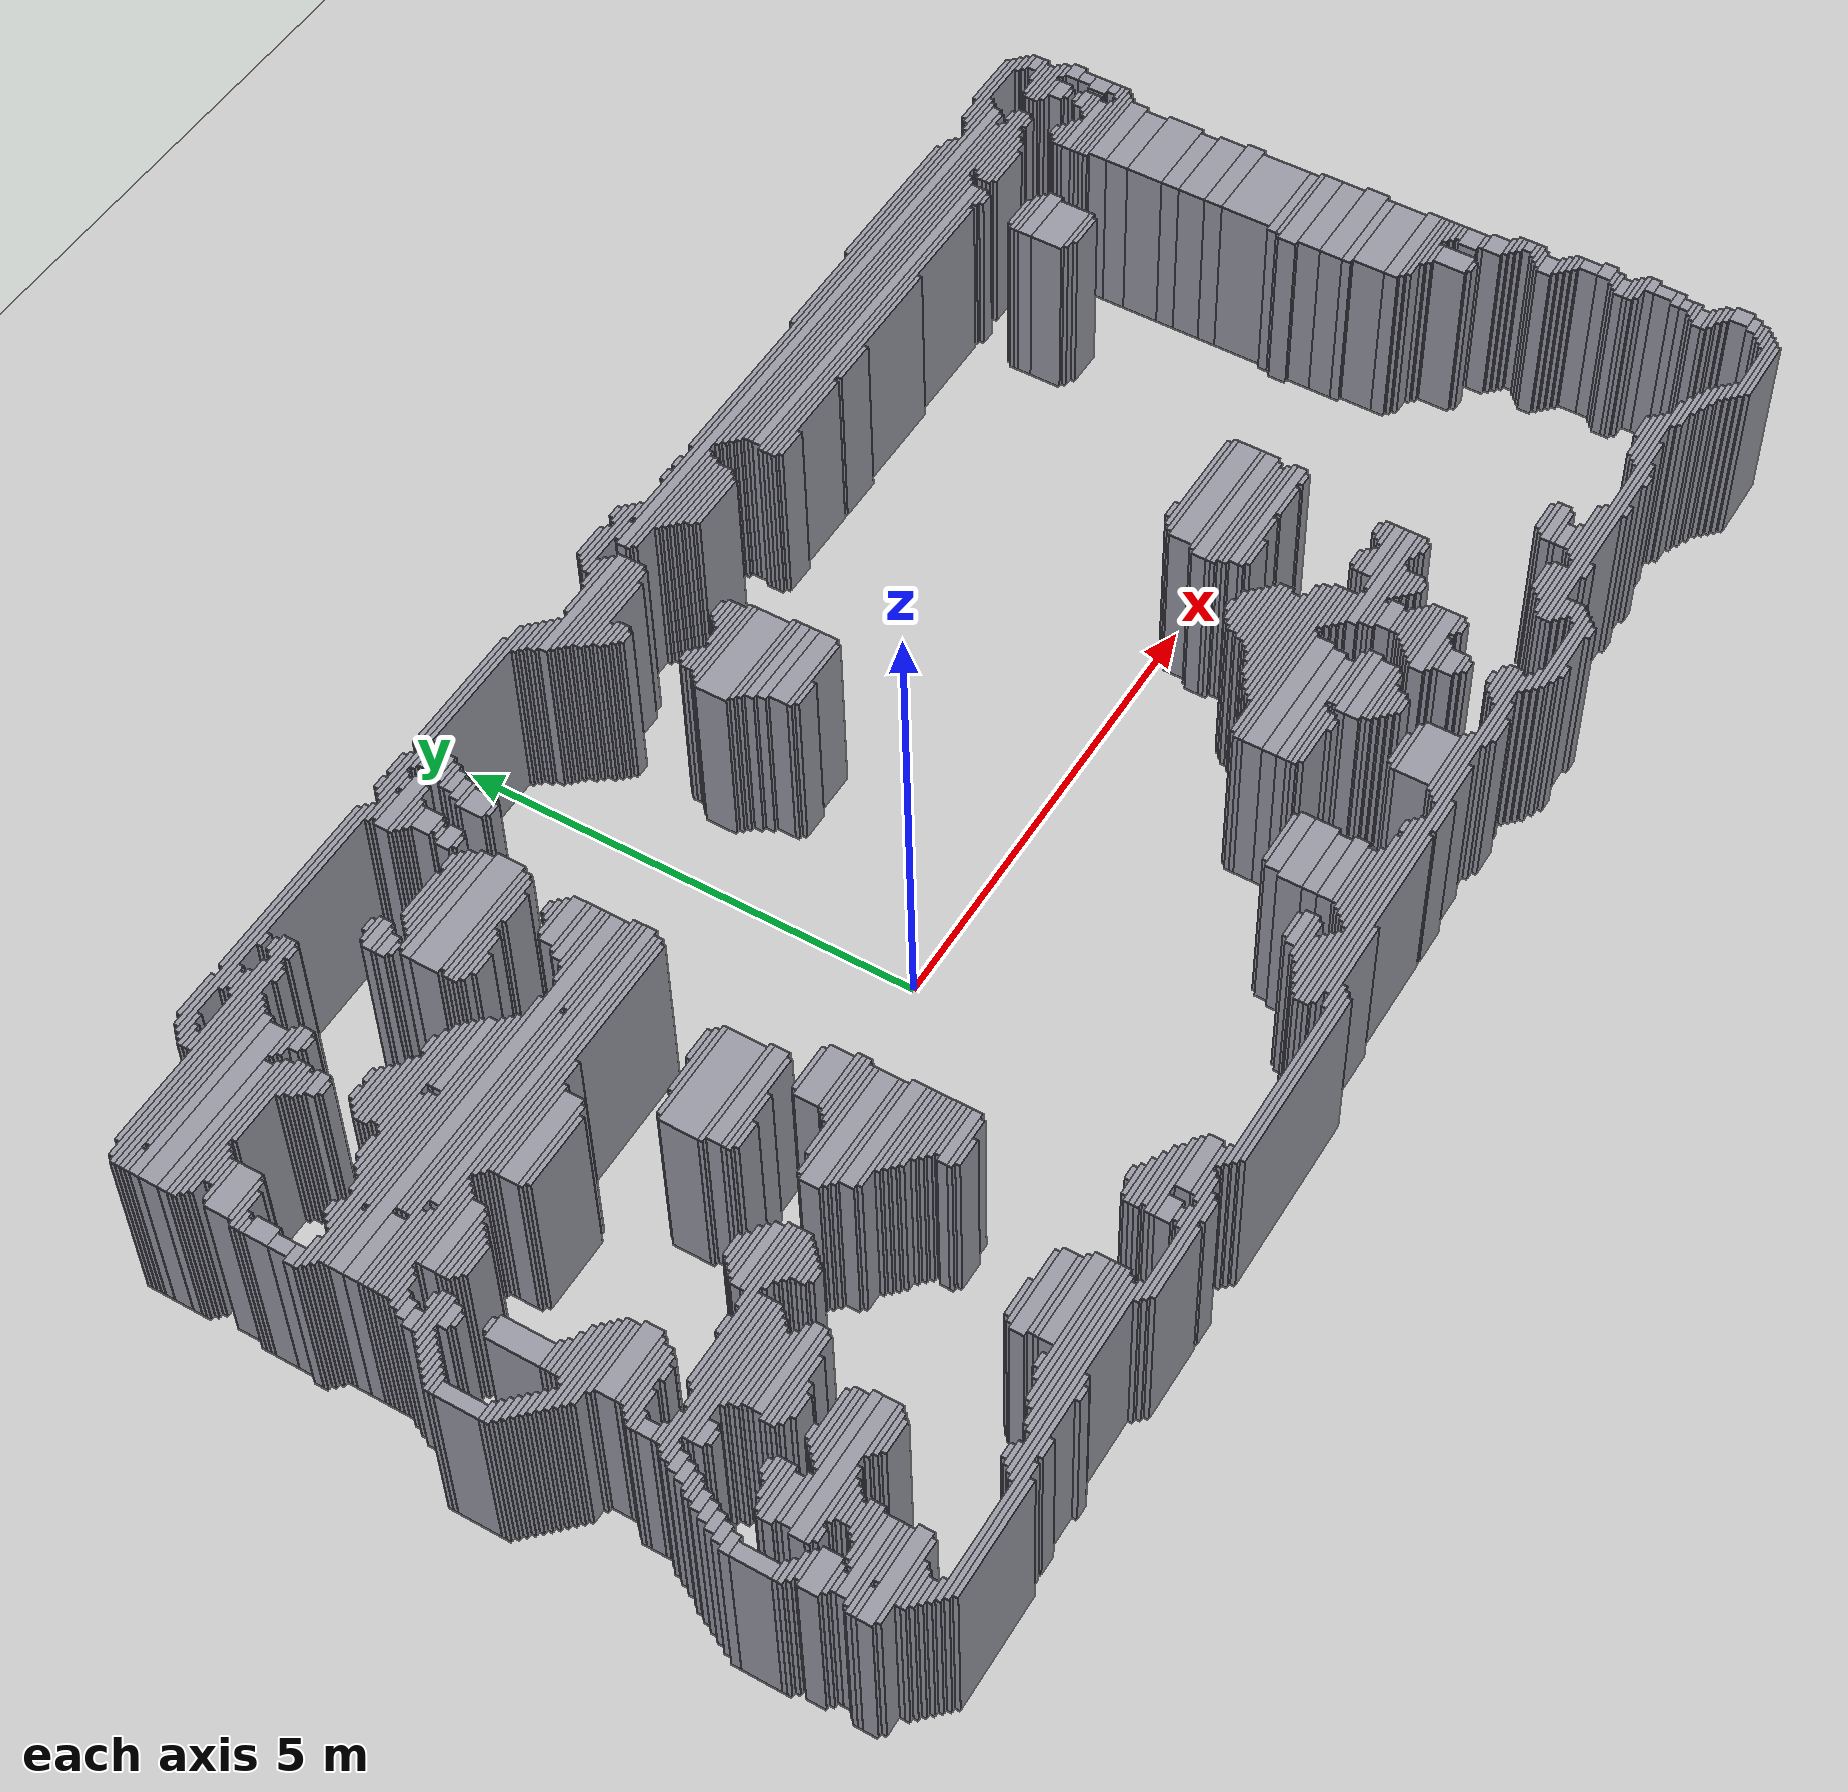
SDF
<?xml version="1.0"?>
<sdf version="1.8">
  <world name="testroom_field">
    <physics type="ode">
      <real_time_update_rate>1000.0</real_time_update_rate>
      <max_step_size>0.001</max_step_size>
      <real_time_factor>1</real_time_factor>
    </physics>
    <plugin filename="gz-sim-physics-system" name="gz::sim::systems::Physics"/>
    <plugin filename="gz-sim-user-commands-system" name="gz::sim::systems::UserCommands"/>
    <plugin filename="gz-sim-scene-broadcaster-system" name="gz::sim::systems::SceneBroadcaster"/>
    <plugin filename="gz-sim-sensors-system" name="gz::sim::systems::Sensors">
      <render_engine>ogre2</render_engine>
    </plugin>
    <plugin filename="gz-sim-imu-system" name="gz::sim::systems::Imu"/>

    <light type="directional" name="sun">
      <cast_shadows>true</cast_shadows>
      <pose>0 0 10 0 0 0</pose>
      <diffuse>1 1 1 1</diffuse>
      <specular>0.4 0.4 0.4 1</specular>
      <attenuation><range>1000</range><constant>0.9</constant><linear>0.01</linear><quadratic>0.001</quadratic></attenuation>
      <direction>-0.5 0.1 -0.9</direction>
    </light>

    <model name="ground_plane">
      <static>true</static>
      <link name="link">
        <collision name="collision">
          <geometry><plane><normal>0 0 1</normal><size>200 200</size></plane></geometry>
        </collision>
        <visual name="visual">
          <geometry><plane><normal>0 0 1</normal><size>200 200</size></plane></geometry>
          <material><ambient>0.8 0.8 0.8 1</ambient><diffuse>0.8 0.8 0.8 1</diffuse></material>
        </visual>
      </link>
    </model>

    <model name="testroom_field_walls">
      <static>true</static>
      <link name="walls">
        <collision name="c0">
          <pose>-5.400 -4.075 1.000 0 0 0</pose>
          <geometry><box><size>1.200 0.050 2.000</size></box></geometry>
        </collision>
        <visual name="v0">
          <pose>-5.400 -4.075 1.000 0 0 0</pose>
          <geometry><box><size>1.200 0.050 2.000</size></box></geometry>
          <material><ambient>0.5 0.5 0.55 1</ambient><diffuse>0.6 0.6 0.65 1</diffuse></material>
        </visual>
        <collision name="c1">
          <pose>-0.325 -4.075 1.000 0 0 0</pose>
          <geometry><box><size>1.950 0.050 2.000</size></box></geometry>
        </collision>
        <visual name="v1">
          <pose>-0.325 -4.075 1.000 0 0 0</pose>
          <geometry><box><size>1.950 0.050 2.000</size></box></geometry>
          <material><ambient>0.5 0.5 0.55 1</ambient><diffuse>0.6 0.6 0.65 1</diffuse></material>
        </visual>
        <collision name="c2">
          <pose>-2.450 -4.075 1.000 0 0 0</pose>
          <geometry><box><size>0.800 0.050 2.000</size></box></geometry>
        </collision>
        <visual name="v2">
          <pose>-2.450 -4.075 1.000 0 0 0</pose>
          <geometry><box><size>0.800 0.050 2.000</size></box></geometry>
          <material><ambient>0.5 0.5 0.55 1</ambient><diffuse>0.6 0.6 0.65 1</diffuse></material>
        </visual>
        <collision name="c3">
          <pose>-1.875 -4.075 1.000 0 0 0</pose>
          <geometry><box><size>0.250 0.050 2.000</size></box></geometry>
        </collision>
        <visual name="v3">
          <pose>-1.875 -4.075 1.000 0 0 0</pose>
          <geometry><box><size>0.250 0.050 2.000</size></box></geometry>
          <material><ambient>0.5 0.5 0.55 1</ambient><diffuse>0.6 0.6 0.65 1</diffuse></material>
        </visual>
        <collision name="c4">
          <pose>5.475 -4.075 1.000 0 0 0</pose>
          <geometry><box><size>0.150 0.050 2.000</size></box></geometry>
        </collision>
        <visual name="v4">
          <pose>5.475 -4.075 1.000 0 0 0</pose>
          <geometry><box><size>0.150 0.050 2.000</size></box></geometry>
          <material><ambient>0.5 0.5 0.55 1</ambient><diffuse>0.6 0.6 0.65 1</diffuse></material>
        </visual>
        <collision name="c5">
          <pose>9.375 -4.075 1.000 0 0 0</pose>
          <geometry><box><size>0.750 0.050 2.000</size></box></geometry>
        </collision>
        <visual name="v5">
          <pose>9.375 -4.075 1.000 0 0 0</pose>
          <geometry><box><size>0.750 0.050 2.000</size></box></geometry>
          <material><ambient>0.5 0.5 0.55 1</ambient><diffuse>0.6 0.6 0.65 1</diffuse></material>
        </visual>
        <collision name="c6">
          <pose>4.925 -4.075 1.000 0 0 0</pose>
          <geometry><box><size>0.150 0.050 2.000</size></box></geometry>
        </collision>
        <visual name="v6">
          <pose>4.925 -4.075 1.000 0 0 0</pose>
          <geometry><box><size>0.150 0.050 2.000</size></box></geometry>
          <material><ambient>0.5 0.5 0.55 1</ambient><diffuse>0.6 0.6 0.65 1</diffuse></material>
        </visual>
        <collision name="c7">
          <pose>9.375 -4.025 1.000 0 0 0</pose>
          <geometry><box><size>0.850 0.050 2.000</size></box></geometry>
        </collision>
        <visual name="v7">
          <pose>9.375 -4.025 1.000 0 0 0</pose>
          <geometry><box><size>0.850 0.050 2.000</size></box></geometry>
          <material><ambient>0.5 0.5 0.55 1</ambient><diffuse>0.6 0.6 0.65 1</diffuse></material>
        </visual>
        <collision name="c8">
          <pose>-2.300 -4.025 1.000 0 0 0</pose>
          <geometry><box><size>1.200 0.050 2.000</size></box></geometry>
        </collision>
        <visual name="v8">
          <pose>-2.300 -4.025 1.000 0 0 0</pose>
          <geometry><box><size>1.200 0.050 2.000</size></box></geometry>
          <material><ambient>0.5 0.5 0.55 1</ambient><diffuse>0.6 0.6 0.65 1</diffuse></material>
        </visual>
        <collision name="c9">
          <pose>5.175 -4.025 1.000 0 0 0</pose>
          <geometry><box><size>0.850 0.050 2.000</size></box></geometry>
        </collision>
        <visual name="v9">
          <pose>5.175 -4.025 1.000 0 0 0</pose>
          <geometry><box><size>0.850 0.050 2.000</size></box></geometry>
          <material><ambient>0.5 0.5 0.55 1</ambient><diffuse>0.6 0.6 0.65 1</diffuse></material>
        </visual>
        <collision name="c10">
          <pose>-4.500 -4.025 1.000 0 0 0</pose>
          <geometry><box><size>0.200 0.050 2.000</size></box></geometry>
        </collision>
        <visual name="v10">
          <pose>-4.500 -4.025 1.000 0 0 0</pose>
          <geometry><box><size>0.200 0.050 2.000</size></box></geometry>
          <material><ambient>0.5 0.5 0.55 1</ambient><diffuse>0.6 0.6 0.65 1</diffuse></material>
        </visual>
        <collision name="c11">
          <pose>-0.325 -4.025 1.000 0 0 0</pose>
          <geometry><box><size>2.050 0.050 2.000</size></box></geometry>
        </collision>
        <visual name="v11">
          <pose>-0.325 -4.025 1.000 0 0 0</pose>
          <geometry><box><size>2.050 0.050 2.000</size></box></geometry>
          <material><ambient>0.5 0.5 0.55 1</ambient><diffuse>0.6 0.6 0.65 1</diffuse></material>
        </visual>
        <collision name="c12">
          <pose>-3.925 -4.025 1.000 0 0 0</pose>
          <geometry><box><size>0.150 0.050 2.000</size></box></geometry>
        </collision>
        <visual name="v12">
          <pose>-3.925 -4.025 1.000 0 0 0</pose>
          <geometry><box><size>0.150 0.050 2.000</size></box></geometry>
          <material><ambient>0.5 0.5 0.55 1</ambient><diffuse>0.6 0.6 0.65 1</diffuse></material>
        </visual>
        <collision name="c13">
          <pose>-5.350 -4.025 1.000 0 0 0</pose>
          <geometry><box><size>1.400 0.050 2.000</size></box></geometry>
        </collision>
        <visual name="v13">
          <pose>-5.350 -4.025 1.000 0 0 0</pose>
          <geometry><box><size>1.400 0.050 2.000</size></box></geometry>
          <material><ambient>0.5 0.5 0.55 1</ambient><diffuse>0.6 0.6 0.65 1</diffuse></material>
        </visual>
        <collision name="c14">
          <pose>9.375 -3.975 1.000 0 0 0</pose>
          <geometry><box><size>0.950 0.050 2.000</size></box></geometry>
        </collision>
        <visual name="v14">
          <pose>9.375 -3.975 1.000 0 0 0</pose>
          <geometry><box><size>0.950 0.050 2.000</size></box></geometry>
          <material><ambient>0.5 0.5 0.55 1</ambient><diffuse>0.6 0.6 0.65 1</diffuse></material>
        </visual>
        <collision name="c15">
          <pose>-4.925 -3.975 1.000 0 0 0</pose>
          <geometry><box><size>2.350 0.050 2.000</size></box></geometry>
        </collision>
        <visual name="v15">
          <pose>-4.925 -3.975 1.000 0 0 0</pose>
          <geometry><box><size>2.350 0.050 2.000</size></box></geometry>
          <material><ambient>0.5 0.5 0.55 1</ambient><diffuse>0.6 0.6 0.65 1</diffuse></material>
        </visual>
        <collision name="c16">
          <pose>-0.325 -3.975 1.000 0 0 0</pose>
          <geometry><box><size>2.150 0.050 2.000</size></box></geometry>
        </collision>
        <visual name="v16">
          <pose>-0.325 -3.975 1.000 0 0 0</pose>
          <geometry><box><size>2.150 0.050 2.000</size></box></geometry>
          <material><ambient>0.5 0.5 0.55 1</ambient><diffuse>0.6 0.6 0.65 1</diffuse></material>
        </visual>
        <collision name="c17">
          <pose>-2.250 -3.975 1.000 0 0 0</pose>
          <geometry><box><size>1.400 0.050 2.000</size></box></geometry>
        </collision>
        <visual name="v17">
          <pose>-2.250 -3.975 1.000 0 0 0</pose>
          <geometry><box><size>1.400 0.050 2.000</size></box></geometry>
          <material><ambient>0.5 0.5 0.55 1</ambient><diffuse>0.6 0.6 0.65 1</diffuse></material>
        </visual>
        <collision name="c18">
          <pose>5.150 -3.975 1.000 0 0 0</pose>
          <geometry><box><size>1.000 0.050 2.000</size></box></geometry>
        </collision>
        <visual name="v18">
          <pose>5.150 -3.975 1.000 0 0 0</pose>
          <geometry><box><size>1.000 0.050 2.000</size></box></geometry>
          <material><ambient>0.5 0.5 0.55 1</ambient><diffuse>0.6 0.6 0.65 1</diffuse></material>
        </visual>
        <collision name="c19">
          <pose>-6.025 -3.925 1.000 0 0 0</pose>
          <geometry><box><size>0.250 0.050 2.000</size></box></geometry>
        </collision>
        <visual name="v19">
          <pose>-6.025 -3.925 1.000 0 0 0</pose>
          <geometry><box><size>0.250 0.050 2.000</size></box></geometry>
          <material><ambient>0.5 0.5 0.55 1</ambient><diffuse>0.6 0.6 0.65 1</diffuse></material>
        </visual>
        <collision name="c20">
          <pose>-1.675 -3.925 1.000 0 0 0</pose>
          <geometry><box><size>0.350 0.050 2.000</size></box></geometry>
        </collision>
        <visual name="v20">
          <pose>-1.675 -3.925 1.000 0 0 0</pose>
          <geometry><box><size>0.350 0.050 2.000</size></box></geometry>
          <material><ambient>0.5 0.5 0.55 1</ambient><diffuse>0.6 0.6 0.65 1</diffuse></material>
        </visual>
        <collision name="c21">
          <pose>-3.825 -3.925 1.000 0 0 0</pose>
          <geometry><box><size>2.150 0.050 2.000</size></box></geometry>
        </collision>
        <visual name="v21">
          <pose>-3.825 -3.925 1.000 0 0 0</pose>
          <geometry><box><size>2.150 0.050 2.000</size></box></geometry>
          <material><ambient>0.5 0.5 0.55 1</ambient><diffuse>0.6 0.6 0.65 1</diffuse></material>
        </visual>
        <collision name="c22">
          <pose>9.775 -3.925 1.000 0 0 0</pose>
          <geometry><box><size>0.250 0.050 2.000</size></box></geometry>
        </collision>
        <visual name="v22">
          <pose>9.775 -3.925 1.000 0 0 0</pose>
          <geometry><box><size>0.250 0.050 2.000</size></box></geometry>
          <material><ambient>0.5 0.5 0.55 1</ambient><diffuse>0.6 0.6 0.65 1</diffuse></material>
        </visual>
        <collision name="c23">
          <pose>-1.325 -3.925 1.000 0 0 0</pose>
          <geometry><box><size>0.250 0.050 2.000</size></box></geometry>
        </collision>
        <visual name="v23">
          <pose>-1.325 -3.925 1.000 0 0 0</pose>
          <geometry><box><size>0.250 0.050 2.000</size></box></geometry>
          <material><ambient>0.5 0.5 0.55 1</ambient><diffuse>0.6 0.6 0.65 1</diffuse></material>
        </visual>
        <collision name="c24">
          <pose>5.150 -3.925 1.000 0 0 0</pose>
          <geometry><box><size>1.100 0.050 2.000</size></box></geometry>
        </collision>
        <visual name="v24">
          <pose>5.150 -3.925 1.000 0 0 0</pose>
          <geometry><box><size>1.100 0.050 2.000</size></box></geometry>
          <material><ambient>0.5 0.5 0.55 1</ambient><diffuse>0.6 0.6 0.65 1</diffuse></material>
        </visual>
        <collision name="c25">
          <pose>8.975 -3.925 1.000 0 0 0</pose>
          <geometry><box><size>0.250 0.050 2.000</size></box></geometry>
        </collision>
        <visual name="v25">
          <pose>8.975 -3.925 1.000 0 0 0</pose>
          <geometry><box><size>0.250 0.050 2.000</size></box></geometry>
          <material><ambient>0.5 0.5 0.55 1</ambient><diffuse>0.6 0.6 0.65 1</diffuse></material>
        </visual>
        <collision name="c26">
          <pose>0.950 -3.925 1.000 0 0 0</pose>
          <geometry><box><size>1.000 0.050 2.000</size></box></geometry>
        </collision>
        <visual name="v26">
          <pose>0.950 -3.925 1.000 0 0 0</pose>
          <geometry><box><size>1.000 0.050 2.000</size></box></geometry>
          <material><ambient>0.5 0.5 0.55 1</ambient><diffuse>0.6 0.6 0.65 1</diffuse></material>
        </visual>
        <collision name="c27">
          <pose>-2.025 -3.925 1.000 0 0 0</pose>
          <geometry><box><size>0.250 0.050 2.000</size></box></geometry>
        </collision>
        <visual name="v27">
          <pose>-2.025 -3.925 1.000 0 0 0</pose>
          <geometry><box><size>0.250 0.050 2.000</size></box></geometry>
          <material><ambient>0.5 0.5 0.55 1</ambient><diffuse>0.6 0.6 0.65 1</diffuse></material>
        </visual>
        <collision name="c28">
          <pose>1.600 -3.875 1.000 0 0 0</pose>
          <geometry><box><size>2.000 0.050 2.000</size></box></geometry>
        </collision>
        <visual name="v28">
          <pose>1.600 -3.875 1.000 0 0 0</pose>
          <geometry><box><size>2.000 0.050 2.000</size></box></geometry>
          <material><ambient>0.5 0.5 0.55 1</ambient><diffuse>0.6 0.6 0.65 1</diffuse></material>
        </visual>
        <collision name="c29">
          <pose>-6.075 -3.875 1.000 0 0 0</pose>
          <geometry><box><size>0.250 0.050 2.000</size></box></geometry>
        </collision>
        <visual name="v29">
          <pose>-6.075 -3.875 1.000 0 0 0</pose>
          <geometry><box><size>0.250 0.050 2.000</size></box></geometry>
          <material><ambient>0.5 0.5 0.55 1</ambient><diffuse>0.6 0.6 0.65 1</diffuse></material>
        </visual>
        <collision name="c30">
          <pose>4.000 -3.875 1.000 0 0 0</pose>
          <geometry><box><size>0.300 0.050 2.000</size></box></geometry>
        </collision>
        <visual name="v30">
          <pose>4.000 -3.875 1.000 0 0 0</pose>
          <geometry><box><size>0.300 0.050 2.000</size></box></geometry>
          <material><ambient>0.5 0.5 0.55 1</ambient><diffuse>0.6 0.6 0.65 1</diffuse></material>
        </visual>
        <collision name="c31">
          <pose>9.825 -3.875 1.000 0 0 0</pose>
          <geometry><box><size>0.250 0.050 2.000</size></box></geometry>
        </collision>
        <visual name="v31">
          <pose>9.825 -3.875 1.000 0 0 0</pose>
          <geometry><box><size>0.250 0.050 2.000</size></box></geometry>
          <material><ambient>0.5 0.5 0.55 1</ambient><diffuse>0.6 0.6 0.65 1</diffuse></material>
        </visual>
        <collision name="c32">
          <pose>5.625 -3.875 1.000 0 0 0</pose>
          <geometry><box><size>0.250 0.050 2.000</size></box></geometry>
        </collision>
        <visual name="v32">
          <pose>5.625 -3.875 1.000 0 0 0</pose>
          <geometry><box><size>0.250 0.050 2.000</size></box></geometry>
          <material><ambient>0.5 0.5 0.55 1</ambient><diffuse>0.6 0.6 0.65 1</diffuse></material>
        </visual>
        <collision name="c33">
          <pose>8.925 -3.875 1.000 0 0 0</pose>
          <geometry><box><size>0.250 0.050 2.000</size></box></geometry>
        </collision>
        <visual name="v33">
          <pose>8.925 -3.875 1.000 0 0 0</pose>
          <geometry><box><size>0.250 0.050 2.000</size></box></geometry>
          <material><ambient>0.5 0.5 0.55 1</ambient><diffuse>0.6 0.6 0.65 1</diffuse></material>
        </visual>
        <collision name="c34">
          <pose>4.700 -3.875 1.000 0 0 0</pose>
          <geometry><box><size>0.300 0.050 2.000</size></box></geometry>
        </collision>
        <visual name="v34">
          <pose>4.700 -3.875 1.000 0 0 0</pose>
          <geometry><box><size>0.300 0.050 2.000</size></box></geometry>
          <material><ambient>0.5 0.5 0.55 1</ambient><diffuse>0.6 0.6 0.65 1</diffuse></material>
        </visual>
        <collision name="c35">
          <pose>-3.825 -3.875 1.000 0 0 0</pose>
          <geometry><box><size>2.050 0.050 2.000</size></box></geometry>
        </collision>
        <visual name="v35">
          <pose>-3.825 -3.875 1.000 0 0 0</pose>
          <geometry><box><size>2.050 0.050 2.000</size></box></geometry>
          <material><ambient>0.5 0.5 0.55 1</ambient><diffuse>0.6 0.6 0.65 1</diffuse></material>
        </visual>
        <collision name="c36">
          <pose>-2.025 -3.875 1.000 0 0 0</pose>
          <geometry><box><size>0.150 0.050 2.000</size></box></geometry>
        </collision>
        <visual name="v36">
          <pose>-2.025 -3.875 1.000 0 0 0</pose>
          <geometry><box><size>0.150 0.050 2.000</size></box></geometry>
          <material><ambient>0.5 0.5 0.55 1</ambient><diffuse>0.6 0.6 0.65 1</diffuse></material>
        </visual>
        <collision name="c37">
          <pose>-1.525 -3.875 1.000 0 0 0</pose>
          <geometry><box><size>0.550 0.050 2.000</size></box></geometry>
        </collision>
        <visual name="v37">
          <pose>-1.525 -3.875 1.000 0 0 0</pose>
          <geometry><box><size>0.550 0.050 2.000</size></box></geometry>
          <material><ambient>0.5 0.5 0.55 1</ambient><diffuse>0.6 0.6 0.65 1</diffuse></material>
        </visual>
        <collision name="c38">
          <pose>2.850 -3.875 1.000 0 0 0</pose>
          <geometry><box><size>0.400 0.050 2.000</size></box></geometry>
        </collision>
        <visual name="v38">
          <pose>2.850 -3.875 1.000 0 0 0</pose>
          <geometry><box><size>0.400 0.050 2.000</size></box></geometry>
          <material><ambient>0.5 0.5 0.55 1</ambient><diffuse>0.6 0.6 0.65 1</diffuse></material>
        </visual>
        <collision name="c39">
          <pose>-3.600 -3.825 1.000 0 0 0</pose>
          <geometry><box><size>1.700 0.050 2.000</size></box></geometry>
        </collision>
        <visual name="v39">
          <pose>-3.600 -3.825 1.000 0 0 0</pose>
          <geometry><box><size>1.700 0.050 2.000</size></box></geometry>
          <material><ambient>0.5 0.5 0.55 1</ambient><diffuse>0.6 0.6 0.65 1</diffuse></material>
        </visual>
        <collision name="c40">
          <pose>1.975 -3.825 1.000 0 0 0</pose>
          <geometry><box><size>3.050 0.050 2.000</size></box></geometry>
        </collision>
        <visual name="v40">
          <pose>1.975 -3.825 1.000 0 0 0</pose>
          <geometry><box><size>3.050 0.050 2.000</size></box></geometry>
          <material><ambient>0.5 0.5 0.55 1</ambient><diffuse>0.6 0.6 0.65 1</diffuse></material>
        </visual>
        <collision name="c41">
          <pose>-4.675 -3.825 1.000 0 0 0</pose>
          <geometry><box><size>0.250 0.050 2.000</size></box></geometry>
        </collision>
        <visual name="v41">
          <pose>-4.675 -3.825 1.000 0 0 0</pose>
          <geometry><box><size>0.250 0.050 2.000</size></box></geometry>
          <material><ambient>0.5 0.5 0.55 1</ambient><diffuse>0.6 0.6 0.65 1</diffuse></material>
        </visual>
        <collision name="c42">
          <pose>5.650 -3.825 1.000 0 0 0</pose>
          <geometry><box><size>0.200 0.050 2.000</size></box></geometry>
        </collision>
        <visual name="v42">
          <pose>5.650 -3.825 1.000 0 0 0</pose>
          <geometry><box><size>0.200 0.050 2.000</size></box></geometry>
          <material><ambient>0.5 0.5 0.55 1</ambient><diffuse>0.6 0.6 0.65 1</diffuse></material>
        </visual>
        <collision name="c43">
          <pose>4.625 -3.825 1.000 0 0 0</pose>
          <geometry><box><size>0.250 0.050 2.000</size></box></geometry>
        </collision>
        <visual name="v43">
          <pose>4.625 -3.825 1.000 0 0 0</pose>
          <geometry><box><size>0.250 0.050 2.000</size></box></geometry>
          <material><ambient>0.5 0.5 0.55 1</ambient><diffuse>0.6 0.6 0.65 1</diffuse></material>
        </visual>
        <collision name="c44">
          <pose>8.850 -3.825 1.000 0 0 0</pose>
          <geometry><box><size>0.300 0.050 2.000</size></box></geometry>
        </collision>
        <visual name="v44">
          <pose>8.850 -3.825 1.000 0 0 0</pose>
          <geometry><box><size>0.300 0.050 2.000</size></box></geometry>
          <material><ambient>0.5 0.5 0.55 1</ambient><diffuse>0.6 0.6 0.65 1</diffuse></material>
        </visual>
        <collision name="c45">
          <pose>-6.100 -3.825 1.000 0 0 0</pose>
          <geometry><box><size>0.300 0.050 2.000</size></box></geometry>
        </collision>
        <visual name="v45">
          <pose>-6.100 -3.825 1.000 0 0 0</pose>
          <geometry><box><size>0.300 0.050 2.000</size></box></geometry>
          <material><ambient>0.5 0.5 0.55 1</ambient><diffuse>0.6 0.6 0.65 1</diffuse></material>
        </visual>
        <collision name="c46">
          <pose>4.050 -3.825 1.000 0 0 0</pose>
          <geometry><box><size>0.600 0.050 2.000</size></box></geometry>
        </collision>
        <visual name="v46">
          <pose>4.050 -3.825 1.000 0 0 0</pose>
          <geometry><box><size>0.600 0.050 2.000</size></box></geometry>
          <material><ambient>0.5 0.5 0.55 1</ambient><diffuse>0.6 0.6 0.65 1</diffuse></material>
        </visual>
        <collision name="c47">
          <pose>9.850 -3.825 1.000 0 0 0</pose>
          <geometry><box><size>0.200 0.050 2.000</size></box></geometry>
        </collision>
        <visual name="v47">
          <pose>9.850 -3.825 1.000 0 0 0</pose>
          <geometry><box><size>0.200 0.050 2.000</size></box></geometry>
          <material><ambient>0.5 0.5 0.55 1</ambient><diffuse>0.6 0.6 0.65 1</diffuse></material>
        </visual>
        <collision name="c48">
          <pose>-4.675 -3.775 1.000 0 0 0</pose>
          <geometry><box><size>0.150 0.050 2.000</size></box></geometry>
        </collision>
        <visual name="v48">
          <pose>-4.675 -3.775 1.000 0 0 0</pose>
          <geometry><box><size>0.150 0.050 2.000</size></box></geometry>
          <material><ambient>0.5 0.5 0.55 1</ambient><diffuse>0.6 0.6 0.65 1</diffuse></material>
        </visual>
        <collision name="c49">
          <pose>8.775 -3.775 1.000 0 0 0</pose>
          <geometry><box><size>0.350 0.050 2.000</size></box></geometry>
        </collision>
        <visual name="v49">
          <pose>8.775 -3.775 1.000 0 0 0</pose>
          <geometry><box><size>0.350 0.050 2.000</size></box></geometry>
          <material><ambient>0.5 0.5 0.55 1</ambient><diffuse>0.6 0.6 0.65 1</diffuse></material>
        </visual>
        <collision name="c50">
          <pose>5.625 -3.775 1.000 0 0 0</pose>
          <geometry><box><size>0.250 0.050 2.000</size></box></geometry>
        </collision>
        <visual name="v50">
          <pose>5.625 -3.775 1.000 0 0 0</pose>
          <geometry><box><size>0.250 0.050 2.000</size></box></geometry>
          <material><ambient>0.5 0.5 0.55 1</ambient><diffuse>0.6 0.6 0.65 1</diffuse></material>
        </visual>
        <collision name="c51">
          <pose>2.550 -3.775 1.000 0 0 0</pose>
          <geometry><box><size>4.300 0.050 2.000</size></box></geometry>
        </collision>
        <visual name="v51">
          <pose>2.550 -3.775 1.000 0 0 0</pose>
          <geometry><box><size>4.300 0.050 2.000</size></box></geometry>
          <material><ambient>0.5 0.5 0.55 1</ambient><diffuse>0.6 0.6 0.65 1</diffuse></material>
        </visual>
        <collision name="c52">
          <pose>-6.100 -3.775 1.000 0 0 0</pose>
          <geometry><box><size>0.400 0.050 2.000</size></box></geometry>
        </collision>
        <visual name="v52">
          <pose>-6.100 -3.775 1.000 0 0 0</pose>
          <geometry><box><size>0.400 0.050 2.000</size></box></geometry>
          <material><ambient>0.5 0.5 0.55 1</ambient><diffuse>0.6 0.6 0.65 1</diffuse></material>
        </visual>
        <collision name="c53">
          <pose>-3.550 -3.775 1.000 0 0 0</pose>
          <geometry><box><size>1.700 0.050 2.000</size></box></geometry>
        </collision>
        <visual name="v53">
          <pose>-3.550 -3.775 1.000 0 0 0</pose>
          <geometry><box><size>1.700 0.050 2.000</size></box></geometry>
          <material><ambient>0.5 0.5 0.55 1</ambient><diffuse>0.6 0.6 0.65 1</diffuse></material>
        </visual>
        <collision name="c54">
          <pose>-1.500 -3.775 1.000 0 0 0</pose>
          <geometry><box><size>0.600 0.150 2.000</size></box></geometry>
        </collision>
        <visual name="v54">
          <pose>-1.500 -3.775 1.000 0 0 0</pose>
          <geometry><box><size>0.600 0.150 2.000</size></box></geometry>
          <material><ambient>0.5 0.5 0.55 1</ambient><diffuse>0.6 0.6 0.65 1</diffuse></material>
        </visual>
        <collision name="c55">
          <pose>-2.025 -3.775 1.000 0 0 0</pose>
          <geometry><box><size>0.250 0.150 2.000</size></box></geometry>
        </collision>
        <visual name="v55">
          <pose>-2.025 -3.775 1.000 0 0 0</pose>
          <geometry><box><size>0.250 0.150 2.000</size></box></geometry>
          <material><ambient>0.5 0.5 0.55 1</ambient><diffuse>0.6 0.6 0.65 1</diffuse></material>
        </visual>
        <collision name="c56">
          <pose>9.900 -3.750 1.000 0 0 0</pose>
          <geometry><box><size>0.200 0.100 2.000</size></box></geometry>
        </collision>
        <visual name="v56">
          <pose>9.900 -3.750 1.000 0 0 0</pose>
          <geometry><box><size>0.200 0.100 2.000</size></box></geometry>
          <material><ambient>0.5 0.5 0.55 1</ambient><diffuse>0.6 0.6 0.65 1</diffuse></material>
        </visual>
        <collision name="c57">
          <pose>6.150 -3.725 1.000 0 0 0</pose>
          <geometry><box><size>0.200 0.050 2.000</size></box></geometry>
        </collision>
        <visual name="v57">
          <pose>6.150 -3.725 1.000 0 0 0</pose>
          <geometry><box><size>0.200 0.050 2.000</size></box></geometry>
          <material><ambient>0.5 0.5 0.55 1</ambient><diffuse>0.6 0.6 0.65 1</diffuse></material>
        </visual>
        <collision name="c58">
          <pose>-3.475 -3.725 1.000 0 0 0</pose>
          <geometry><box><size>1.550 0.050 2.000</size></box></geometry>
        </collision>
        <visual name="v58">
          <pose>-3.475 -3.725 1.000 0 0 0</pose>
          <geometry><box><size>1.550 0.050 2.000</size></box></geometry>
          <material><ambient>0.5 0.5 0.55 1</ambient><diffuse>0.6 0.6 0.65 1</diffuse></material>
        </visual>
        <collision name="c59">
          <pose>7.475 -3.725 1.000 0 0 0</pose>
          <geometry><box><size>0.150 0.050 2.000</size></box></geometry>
        </collision>
        <visual name="v59">
          <pose>7.475 -3.725 1.000 0 0 0</pose>
          <geometry><box><size>0.150 0.050 2.000</size></box></geometry>
          <material><ambient>0.5 0.5 0.55 1</ambient><diffuse>0.6 0.6 0.65 1</diffuse></material>
        </visual>
        <collision name="c60">
          <pose>5.600 -3.725 1.000 0 0 0</pose>
          <geometry><box><size>0.300 0.050 2.000</size></box></geometry>
        </collision>
        <visual name="v60">
          <pose>5.600 -3.725 1.000 0 0 0</pose>
          <geometry><box><size>0.300 0.050 2.000</size></box></geometry>
          <material><ambient>0.5 0.5 0.55 1</ambient><diffuse>0.6 0.6 0.65 1</diffuse></material>
        </visual>
        <collision name="c61">
          <pose>3.850 -3.725 1.000 0 0 0</pose>
          <geometry><box><size>1.800 0.050 2.000</size></box></geometry>
        </collision>
        <visual name="v61">
          <pose>3.850 -3.725 1.000 0 0 0</pose>
          <geometry><box><size>1.800 0.050 2.000</size></box></geometry>
          <material><ambient>0.5 0.5 0.55 1</ambient><diffuse>0.6 0.6 0.65 1</diffuse></material>
        </visual>
        <collision name="c62">
          <pose>-6.075 -3.725 1.000 0 0 0</pose>
          <geometry><box><size>0.450 0.050 2.000</size></box></geometry>
        </collision>
        <visual name="v62">
          <pose>-6.075 -3.725 1.000 0 0 0</pose>
          <geometry><box><size>0.450 0.050 2.000</size></box></geometry>
          <material><ambient>0.5 0.5 0.55 1</ambient><diffuse>0.6 0.6 0.65 1</diffuse></material>
        </visual>
        <collision name="c63">
          <pose>7.025 -3.725 1.000 0 0 0</pose>
          <geometry><box><size>0.150 0.050 2.000</size></box></geometry>
        </collision>
        <visual name="v63">
          <pose>7.025 -3.725 1.000 0 0 0</pose>
          <geometry><box><size>0.150 0.050 2.000</size></box></geometry>
          <material><ambient>0.5 0.5 0.55 1</ambient><diffuse>0.6 0.6 0.65 1</diffuse></material>
        </visual>
        <collision name="c64">
          <pose>8.700 -3.725 1.000 0 0 0</pose>
          <geometry><box><size>0.400 0.050 2.000</size></box></geometry>
        </collision>
        <visual name="v64">
          <pose>8.700 -3.725 1.000 0 0 0</pose>
          <geometry><box><size>0.400 0.050 2.000</size></box></geometry>
          <material><ambient>0.5 0.5 0.55 1</ambient><diffuse>0.6 0.6 0.65 1</diffuse></material>
        </visual>
        <collision name="c65">
          <pose>1.575 -3.725 1.000 0 0 0</pose>
          <geometry><box><size>2.350 0.050 2.000</size></box></geometry>
        </collision>
        <visual name="v65">
          <pose>1.575 -3.725 1.000 0 0 0</pose>
          <geometry><box><size>2.350 0.050 2.000</size></box></geometry>
          <material><ambient>0.5 0.5 0.55 1</ambient><diffuse>0.6 0.6 0.65 1</diffuse></material>
        </visual>
        <collision name="c66">
          <pose>0.825 -3.675 1.000 0 0 0</pose>
          <geometry><box><size>0.850 0.050 2.000</size></box></geometry>
        </collision>
        <visual name="v66">
          <pose>0.825 -3.675 1.000 0 0 0</pose>
          <geometry><box><size>0.850 0.050 2.000</size></box></geometry>
          <material><ambient>0.5 0.5 0.55 1</ambient><diffuse>0.6 0.6 0.65 1</diffuse></material>
        </visual>
        <collision name="c67">
          <pose>3.425 -3.675 1.000 0 0 0</pose>
          <geometry><box><size>0.850 0.050 2.000</size></box></geometry>
        </collision>
        <visual name="v67">
          <pose>3.425 -3.675 1.000 0 0 0</pose>
          <geometry><box><size>0.850 0.050 2.000</size></box></geometry>
          <material><ambient>0.5 0.5 0.55 1</ambient><diffuse>0.6 0.6 0.65 1</diffuse></material>
        </visual>
        <collision name="c68">
          <pose>2.000 -3.675 1.000 0 0 0</pose>
          <geometry><box><size>1.400 0.050 2.000</size></box></geometry>
        </collision>
        <visual name="v68">
          <pose>2.000 -3.675 1.000 0 0 0</pose>
          <geometry><box><size>1.400 0.050 2.000</size></box></geometry>
          <material><ambient>0.5 0.5 0.55 1</ambient><diffuse>0.6 0.6 0.65 1</diffuse></material>
        </visual>
        <collision name="c69">
          <pose>-6.075 -3.675 1.000 0 0 0</pose>
          <geometry><box><size>0.850 0.050 2.000</size></box></geometry>
        </collision>
        <visual name="v69">
          <pose>-6.075 -3.675 1.000 0 0 0</pose>
          <geometry><box><size>0.850 0.050 2.000</size></box></geometry>
          <material><ambient>0.5 0.5 0.55 1</ambient><diffuse>0.6 0.6 0.65 1</diffuse></material>
        </visual>
        <collision name="c70">
          <pose>8.550 -3.675 1.000 0 0 0</pose>
          <geometry><box><size>0.500 0.050 2.000</size></box></geometry>
        </collision>
        <visual name="v70">
          <pose>8.550 -3.675 1.000 0 0 0</pose>
          <geometry><box><size>0.500 0.050 2.000</size></box></geometry>
          <material><ambient>0.5 0.5 0.55 1</ambient><diffuse>0.6 0.6 0.65 1</diffuse></material>
        </visual>
        <collision name="c71">
          <pose>4.500 -3.675 1.000 0 0 0</pose>
          <geometry><box><size>0.500 0.050 2.000</size></box></geometry>
        </collision>
        <visual name="v71">
          <pose>4.500 -3.675 1.000 0 0 0</pose>
          <geometry><box><size>0.500 0.050 2.000</size></box></geometry>
          <material><ambient>0.5 0.5 0.55 1</ambient><diffuse>0.6 0.6 0.65 1</diffuse></material>
        </visual>
        <collision name="c72">
          <pose>-3.450 -3.675 1.000 0 0 0</pose>
          <geometry><box><size>1.500 0.050 2.000</size></box></geometry>
        </collision>
        <visual name="v72">
          <pose>-3.450 -3.675 1.000 0 0 0</pose>
          <geometry><box><size>1.500 0.050 2.000</size></box></geometry>
          <material><ambient>0.5 0.5 0.55 1</ambient><diffuse>0.6 0.6 0.65 1</diffuse></material>
        </visual>
        <collision name="c73">
          <pose>-1.700 -3.675 1.000 0 0 0</pose>
          <geometry><box><size>0.900 0.050 2.000</size></box></geometry>
        </collision>
        <visual name="v73">
          <pose>-1.700 -3.675 1.000 0 0 0</pose>
          <geometry><box><size>0.900 0.050 2.000</size></box></geometry>
          <material><ambient>0.5 0.5 0.55 1</ambient><diffuse>0.6 0.6 0.65 1</diffuse></material>
        </visual>
        <collision name="c74">
          <pose>6.550 -3.675 1.000 0 0 0</pose>
          <geometry><box><size>2.300 0.050 2.000</size></box></geometry>
        </collision>
        <visual name="v74">
          <pose>6.550 -3.675 1.000 0 0 0</pose>
          <geometry><box><size>2.300 0.050 2.000</size></box></geometry>
          <material><ambient>0.5 0.5 0.55 1</ambient><diffuse>0.6 0.6 0.65 1</diffuse></material>
        </visual>
        <collision name="c75">
          <pose>8.475 -3.625 1.000 0 0 0</pose>
          <geometry><box><size>0.450 0.050 2.000</size></box></geometry>
        </collision>
        <visual name="v75">
          <pose>8.475 -3.625 1.000 0 0 0</pose>
          <geometry><box><size>0.450 0.050 2.000</size></box></geometry>
          <material><ambient>0.5 0.5 0.55 1</ambient><diffuse>0.6 0.6 0.65 1</diffuse></material>
        </visual>
        <collision name="c76">
          <pose>6.700 -3.625 1.000 0 0 0</pose>
          <geometry><box><size>2.600 0.050 2.000</size></box></geometry>
        </collision>
        <visual name="v76">
          <pose>6.700 -3.625 1.000 0 0 0</pose>
          <geometry><box><size>2.600 0.050 2.000</size></box></geometry>
          <material><ambient>0.5 0.5 0.55 1</ambient><diffuse>0.6 0.6 0.65 1</diffuse></material>
        </visual>
        <collision name="c77">
          <pose>-1.725 -3.625 1.000 0 0 0</pose>
          <geometry><box><size>0.850 0.050 2.000</size></box></geometry>
        </collision>
        <visual name="v77">
          <pose>-1.725 -3.625 1.000 0 0 0</pose>
          <geometry><box><size>0.850 0.050 2.000</size></box></geometry>
          <material><ambient>0.5 0.5 0.55 1</ambient><diffuse>0.6 0.6 0.65 1</diffuse></material>
        </visual>
        <collision name="c78">
          <pose>4.525 -3.625 1.000 0 0 0</pose>
          <geometry><box><size>0.450 0.050 2.000</size></box></geometry>
        </collision>
        <visual name="v78">
          <pose>4.525 -3.625 1.000 0 0 0</pose>
          <geometry><box><size>0.450 0.050 2.000</size></box></geometry>
          <material><ambient>0.5 0.5 0.55 1</ambient><diffuse>0.6 0.6 0.65 1</diffuse></material>
        </visual>
        <collision name="c79">
          <pose>3.425 -3.625 1.000 0 0 0</pose>
          <geometry><box><size>0.750 0.050 2.000</size></box></geometry>
        </collision>
        <visual name="v79">
          <pose>3.425 -3.625 1.000 0 0 0</pose>
          <geometry><box><size>0.750 0.050 2.000</size></box></geometry>
          <material><ambient>0.5 0.5 0.55 1</ambient><diffuse>0.6 0.6 0.65 1</diffuse></material>
        </visual>
        <collision name="c80">
          <pose>0.825 -3.625 1.000 0 0 0</pose>
          <geometry><box><size>0.750 0.050 2.000</size></box></geometry>
        </collision>
        <visual name="v80">
          <pose>0.825 -3.625 1.000 0 0 0</pose>
          <geometry><box><size>0.750 0.050 2.000</size></box></geometry>
          <material><ambient>0.5 0.5 0.55 1</ambient><diffuse>0.6 0.6 0.65 1</diffuse></material>
        </visual>
        <collision name="c81">
          <pose>2.575 -3.625 1.000 0 0 0</pose>
          <geometry><box><size>0.150 0.050 2.000</size></box></geometry>
        </collision>
        <visual name="v81">
          <pose>2.575 -3.625 1.000 0 0 0</pose>
          <geometry><box><size>0.150 0.050 2.000</size></box></geometry>
          <material><ambient>0.5 0.5 0.55 1</ambient><diffuse>0.6 0.6 0.65 1</diffuse></material>
        </visual>
        <collision name="c82">
          <pose>-3.350 -3.625 1.000 0 0 0</pose>
          <geometry><box><size>1.300 0.050 2.000</size></box></geometry>
        </collision>
        <visual name="v82">
          <pose>-3.350 -3.625 1.000 0 0 0</pose>
          <geometry><box><size>1.300 0.050 2.000</size></box></geometry>
          <material><ambient>0.5 0.5 0.55 1</ambient><diffuse>0.6 0.6 0.65 1</diffuse></material>
        </visual>
        <collision name="c83">
          <pose>1.900 -3.625 1.000 0 0 0</pose>
          <geometry><box><size>1.100 0.050 2.000</size></box></geometry>
        </collision>
        <visual name="v83">
          <pose>1.900 -3.625 1.000 0 0 0</pose>
          <geometry><box><size>1.100 0.050 2.000</size></box></geometry>
          <material><ambient>0.5 0.5 0.55 1</ambient><diffuse>0.6 0.6 0.65 1</diffuse></material>
        </visual>
        <collision name="c84">
          <pose>1.825 -3.575 1.000 0 0 0</pose>
          <geometry><box><size>0.850 0.050 2.000</size></box></geometry>
        </collision>
        <visual name="v84">
          <pose>1.825 -3.575 1.000 0 0 0</pose>
          <geometry><box><size>0.850 0.050 2.000</size></box></geometry>
          <material><ambient>0.5 0.5 0.55 1</ambient><diffuse>0.6 0.6 0.65 1</diffuse></material>
        </visual>
        <collision name="c85">
          <pose>7.000 -3.575 1.000 0 0 0</pose>
          <geometry><box><size>3.200 0.050 2.000</size></box></geometry>
        </collision>
        <visual name="v85">
          <pose>7.000 -3.575 1.000 0 0 0</pose>
          <geometry><box><size>3.200 0.050 2.000</size></box></geometry>
          <material><ambient>0.5 0.5 0.55 1</ambient><diffuse>0.6 0.6 0.65 1</diffuse></material>
        </visual>
        <collision name="c86">
          <pose>-1.750 -3.575 1.000 0 0 0</pose>
          <geometry><box><size>0.700 0.050 2.000</size></box></geometry>
        </collision>
        <visual name="v86">
          <pose>-1.750 -3.575 1.000 0 0 0</pose>
          <geometry><box><size>0.700 0.050 2.000</size></box></geometry>
          <material><ambient>0.5 0.5 0.55 1</ambient><diffuse>0.6 0.6 0.65 1</diffuse></material>
        </visual>
        <collision name="c87">
          <pose>-3.825 -3.575 1.000 0 0 0</pose>
          <geometry><box><size>0.150 0.050 2.000</size></box></geometry>
        </collision>
        <visual name="v87">
          <pose>-3.825 -3.575 1.000 0 0 0</pose>
          <geometry><box><size>0.150 0.050 2.000</size></box></geometry>
          <material><ambient>0.5 0.5 0.55 1</ambient><diffuse>0.6 0.6 0.65 1</diffuse></material>
        </visual>
        <collision name="c88">
          <pose>4.525 -3.575 1.000 0 0 0</pose>
          <geometry><box><size>0.350 0.050 2.000</size></box></geometry>
        </collision>
        <visual name="v88">
          <pose>4.525 -3.575 1.000 0 0 0</pose>
          <geometry><box><size>0.350 0.050 2.000</size></box></geometry>
          <material><ambient>0.5 0.5 0.55 1</ambient><diffuse>0.6 0.6 0.65 1</diffuse></material>
        </visual>
        <collision name="c89">
          <pose>0.850 -3.575 1.000 0 0 0</pose>
          <geometry><box><size>0.600 0.050 2.000</size></box></geometry>
        </collision>
        <visual name="v89">
          <pose>0.850 -3.575 1.000 0 0 0</pose>
          <geometry><box><size>0.600 0.050 2.000</size></box></geometry>
          <material><ambient>0.5 0.5 0.55 1</ambient><diffuse>0.6 0.6 0.65 1</diffuse></material>
        </visual>
        <collision name="c90">
          <pose>9.950 -3.600 1.000 0 0 0</pose>
          <geometry><box><size>0.200 0.200 2.000</size></box></geometry>
        </collision>
        <visual name="v90">
          <pose>9.950 -3.600 1.000 0 0 0</pose>
          <geometry><box><size>0.200 0.200 2.000</size></box></geometry>
          <material><ambient>0.5 0.5 0.55 1</ambient><diffuse>0.6 0.6 0.65 1</diffuse></material>
        </visual>
        <collision name="c91">
          <pose>-6.075 -3.575 1.000 0 0 0</pose>
          <geometry><box><size>0.950 0.150 2.000</size></box></geometry>
        </collision>
        <visual name="v91">
          <pose>-6.075 -3.575 1.000 0 0 0</pose>
          <geometry><box><size>0.950 0.150 2.000</size></box></geometry>
          <material><ambient>0.5 0.5 0.55 1</ambient><diffuse>0.6 0.6 0.65 1</diffuse></material>
        </visual>
        <collision name="c92">
          <pose>1.825 -3.525 1.000 0 0 0</pose>
          <geometry><box><size>0.750 0.050 2.000</size></box></geometry>
        </collision>
        <visual name="v92">
          <pose>1.825 -3.525 1.000 0 0 0</pose>
          <geometry><box><size>0.750 0.050 2.000</size></box></geometry>
          <material><ambient>0.5 0.5 0.55 1</ambient><diffuse>0.6 0.6 0.65 1</diffuse></material>
        </visual>
        <collision name="c93">
          <pose>8.000 -3.525 1.000 0 0 0</pose>
          <geometry><box><size>0.800 0.050 2.000</size></box></geometry>
        </collision>
        <visual name="v93">
          <pose>8.000 -3.525 1.000 0 0 0</pose>
          <geometry><box><size>0.800 0.050 2.000</size></box></geometry>
          <material><ambient>0.5 0.5 0.55 1</ambient><diffuse>0.6 0.6 0.65 1</diffuse></material>
        </visual>
        <collision name="c94">
          <pose>5.775 -3.525 1.000 0 0 0</pose>
          <geometry><box><size>0.650 0.050 2.000</size></box></geometry>
        </collision>
        <visual name="v94">
          <pose>5.775 -3.525 1.000 0 0 0</pose>
          <geometry><box><size>0.650 0.050 2.000</size></box></geometry>
          <material><ambient>0.5 0.5 0.55 1</ambient><diffuse>0.6 0.6 0.65 1</diffuse></material>
        </visual>
        <collision name="c95">
          <pose>-1.800 -3.525 1.000 0 0 0</pose>
          <geometry><box><size>0.700 0.050 2.000</size></box></geometry>
        </collision>
        <visual name="v95">
          <pose>-1.800 -3.525 1.000 0 0 0</pose>
          <geometry><box><size>0.700 0.050 2.000</size></box></geometry>
          <material><ambient>0.5 0.5 0.55 1</ambient><diffuse>0.6 0.6 0.65 1</diffuse></material>
        </visual>
        <collision name="c96">
          <pose>0.875 -3.525 1.000 0 0 0</pose>
          <geometry><box><size>0.450 0.050 2.000</size></box></geometry>
        </collision>
        <visual name="v96">
          <pose>0.875 -3.525 1.000 0 0 0</pose>
          <geometry><box><size>0.450 0.050 2.000</size></box></geometry>
          <material><ambient>0.5 0.5 0.55 1</ambient><diffuse>0.6 0.6 0.65 1</diffuse></material>
        </visual>
        <collision name="c97">
          <pose>6.600 -3.525 1.000 0 0 0</pose>
          <geometry><box><size>0.800 0.050 2.000</size></box></geometry>
        </collision>
        <visual name="v97">
          <pose>6.600 -3.525 1.000 0 0 0</pose>
          <geometry><box><size>0.800 0.050 2.000</size></box></geometry>
          <material><ambient>0.5 0.5 0.55 1</ambient><diffuse>0.6 0.6 0.65 1</diffuse></material>
        </visual>
        <collision name="c98">
          <pose>4.525 -3.525 1.000 0 0 0</pose>
          <geometry><box><size>0.150 0.050 2.000</size></box></geometry>
        </collision>
        <visual name="v98">
          <pose>4.525 -3.525 1.000 0 0 0</pose>
          <geometry><box><size>0.150 0.050 2.000</size></box></geometry>
          <material><ambient>0.5 0.5 0.55 1</ambient><diffuse>0.6 0.6 0.65 1</diffuse></material>
        </visual>
        <collision name="c99">
          <pose>-3.175 -3.525 1.000 0 0 0</pose>
          <geometry><box><size>0.950 0.150 2.000</size></box></geometry>
        </collision>
        <visual name="v99">
          <pose>-3.175 -3.525 1.000 0 0 0</pose>
          <geometry><box><size>0.950 0.150 2.000</size></box></geometry>
          <material><ambient>0.5 0.5 0.55 1</ambient><diffuse>0.6 0.6 0.65 1</diffuse></material>
        </visual>
        <collision name="c100">
          <pose>-6.400 -3.475 1.000 0 0 0</pose>
          <geometry><box><size>0.300 0.050 2.000</size></box></geometry>
        </collision>
        <visual name="v100">
          <pose>-6.400 -3.475 1.000 0 0 0</pose>
          <geometry><box><size>0.300 0.050 2.000</size></box></geometry>
          <material><ambient>0.5 0.5 0.55 1</ambient><diffuse>0.6 0.6 0.65 1</diffuse></material>
        </visual>
        <collision name="c101">
          <pose>1.000 -3.475 1.000 0 0 0</pose>
          <geometry><box><size>0.500 0.050 2.000</size></box></geometry>
        </collision>
        <visual name="v101">
          <pose>1.000 -3.475 1.000 0 0 0</pose>
          <geometry><box><size>0.500 0.050 2.000</size></box></geometry>
          <material><ambient>0.5 0.5 0.55 1</ambient><diffuse>0.6 0.6 0.65 1</diffuse></material>
        </visual>
        <collision name="c102">
          <pose>1.850 -3.475 1.000 0 0 0</pose>
          <geometry><box><size>0.700 0.050 2.000</size></box></geometry>
        </collision>
        <visual name="v102">
          <pose>1.850 -3.475 1.000 0 0 0</pose>
          <geometry><box><size>0.700 0.050 2.000</size></box></geometry>
          <material><ambient>0.5 0.5 0.55 1</ambient><diffuse>0.6 0.6 0.65 1</diffuse></material>
        </visual>
        <collision name="c103">
          <pose>8.000 -3.475 1.000 0 0 0</pose>
          <geometry><box><size>0.700 0.050 2.000</size></box></geometry>
        </collision>
        <visual name="v103">
          <pose>8.000 -3.475 1.000 0 0 0</pose>
          <geometry><box><size>0.700 0.050 2.000</size></box></geometry>
          <material><ambient>0.5 0.5 0.55 1</ambient><diffuse>0.6 0.6 0.65 1</diffuse></material>
        </visual>
        <collision name="c104">
          <pose>9.900 -3.475 1.000 0 0 0</pose>
          <geometry><box><size>0.200 0.050 2.000</size></box></geometry>
        </collision>
        <visual name="v104">
          <pose>9.900 -3.475 1.000 0 0 0</pose>
          <geometry><box><size>0.200 0.050 2.000</size></box></geometry>
          <material><ambient>0.5 0.5 0.55 1</ambient><diffuse>0.6 0.6 0.65 1</diffuse></material>
        </visual>
        <collision name="c105">
          <pose>-5.925 -3.475 1.000 0 0 0</pose>
          <geometry><box><size>0.550 0.050 2.000</size></box></geometry>
        </collision>
        <visual name="v105">
          <pose>-5.925 -3.475 1.000 0 0 0</pose>
          <geometry><box><size>0.550 0.050 2.000</size></box></geometry>
          <material><ambient>0.5 0.5 0.55 1</ambient><diffuse>0.6 0.6 0.65 1</diffuse></material>
        </visual>
        <collision name="c106">
          <pose>-1.850 -3.475 1.000 0 0 0</pose>
          <geometry><box><size>0.600 0.050 2.000</size></box></geometry>
        </collision>
        <visual name="v106">
          <pose>-1.850 -3.475 1.000 0 0 0</pose>
          <geometry><box><size>0.600 0.050 2.000</size></box></geometry>
          <material><ambient>0.5 0.5 0.55 1</ambient><diffuse>0.6 0.6 0.65 1</diffuse></material>
        </visual>
        <collision name="c107">
          <pose>6.600 -3.475 1.000 0 0 0</pose>
          <geometry><box><size>0.700 0.050 2.000</size></box></geometry>
        </collision>
        <visual name="v107">
          <pose>6.600 -3.475 1.000 0 0 0</pose>
          <geometry><box><size>0.700 0.050 2.000</size></box></geometry>
          <material><ambient>0.5 0.5 0.55 1</ambient><diffuse>0.6 0.6 0.65 1</diffuse></material>
        </visual>
        <collision name="c108">
          <pose>5.850 -3.475 1.000 0 0 0</pose>
          <geometry><box><size>0.500 0.050 2.000</size></box></geometry>
        </collision>
        <visual name="v108">
          <pose>5.850 -3.475 1.000 0 0 0</pose>
          <geometry><box><size>0.500 0.050 2.000</size></box></geometry>
          <material><ambient>0.5 0.5 0.55 1</ambient><diffuse>0.6 0.6 0.65 1</diffuse></material>
        </visual>
        <collision name="c109">
          <pose>1.050 -3.425 1.000 0 0 0</pose>
          <geometry><box><size>0.500 0.050 2.000</size></box></geometry>
        </collision>
        <visual name="v109">
          <pose>1.050 -3.425 1.000 0 0 0</pose>
          <geometry><box><size>0.500 0.050 2.000</size></box></geometry>
          <material><ambient>0.5 0.5 0.55 1</ambient><diffuse>0.6 0.6 0.65 1</diffuse></material>
        </visual>
        <collision name="c110">
          <pose>-6.100 -3.425 1.000 0 0 0</pose>
          <geometry><box><size>0.900 0.050 2.000</size></box></geometry>
        </collision>
        <visual name="v110">
          <pose>-6.100 -3.425 1.000 0 0 0</pose>
          <geometry><box><size>0.900 0.050 2.000</size></box></geometry>
          <material><ambient>0.5 0.5 0.55 1</ambient><diffuse>0.6 0.6 0.65 1</diffuse></material>
        </visual>
        <collision name="c111">
          <pose>-1.900 -3.425 1.000 0 0 0</pose>
          <geometry><box><size>0.500 0.050 2.000</size></box></geometry>
        </collision>
        <visual name="v111">
          <pose>-1.900 -3.425 1.000 0 0 0</pose>
          <geometry><box><size>0.500 0.050 2.000</size></box></geometry>
          <material><ambient>0.5 0.5 0.55 1</ambient><diffuse>0.6 0.6 0.65 1</diffuse></material>
        </visual>
        <collision name="c112">
          <pose>-3.200 -3.425 1.000 0 0 0</pose>
          <geometry><box><size>0.900 0.050 2.000</size></box></geometry>
        </collision>
        <visual name="v112">
          <pose>-3.200 -3.425 1.000 0 0 0</pose>
          <geometry><box><size>0.900 0.050 2.000</size></box></geometry>
          <material><ambient>0.5 0.5 0.55 1</ambient><diffuse>0.6 0.6 0.65 1</diffuse></material>
        </visual>
        <collision name="c113">
          <pose>8.000 -3.425 1.000 0 0 0</pose>
          <geometry><box><size>0.600 0.050 2.000</size></box></geometry>
        </collision>
        <visual name="v113">
          <pose>8.000 -3.425 1.000 0 0 0</pose>
          <geometry><box><size>0.600 0.050 2.000</size></box></geometry>
          <material><ambient>0.5 0.5 0.55 1</ambient><diffuse>0.6 0.6 0.65 1</diffuse></material>
        </visual>
        <collision name="c114">
          <pose>6.475 -3.425 1.000 0 0 0</pose>
          <geometry><box><size>0.350 0.050 2.000</size></box></geometry>
        </collision>
        <visual name="v114">
          <pose>6.475 -3.425 1.000 0 0 0</pose>
          <geometry><box><size>0.350 0.050 2.000</size></box></geometry>
          <material><ambient>0.5 0.5 0.55 1</ambient><diffuse>0.6 0.6 0.65 1</diffuse></material>
        </visual>
        <collision name="c115">
          <pose>9.875 -3.425 1.000 0 0 0</pose>
          <geometry><box><size>0.250 0.050 2.000</size></box></geometry>
        </collision>
        <visual name="v115">
          <pose>9.875 -3.425 1.000 0 0 0</pose>
          <geometry><box><size>0.250 0.050 2.000</size></box></geometry>
          <material><ambient>0.5 0.5 0.55 1</ambient><diffuse>0.6 0.6 0.65 1</diffuse></material>
        </visual>
        <collision name="c116">
          <pose>5.875 -3.425 1.000 0 0 0</pose>
          <geometry><box><size>0.450 0.050 2.000</size></box></geometry>
        </collision>
        <visual name="v116">
          <pose>5.875 -3.425 1.000 0 0 0</pose>
          <geometry><box><size>0.450 0.050 2.000</size></box></geometry>
          <material><ambient>0.5 0.5 0.55 1</ambient><diffuse>0.6 0.6 0.65 1</diffuse></material>
        </visual>
        <collision name="c117">
          <pose>5.875 -3.375 1.000 0 0 0</pose>
          <geometry><box><size>0.350 0.050 2.000</size></box></geometry>
        </collision>
        <visual name="v117">
          <pose>5.875 -3.375 1.000 0 0 0</pose>
          <geometry><box><size>0.350 0.050 2.000</size></box></geometry>
          <material><ambient>0.5 0.5 0.55 1</ambient><diffuse>0.6 0.6 0.65 1</diffuse></material>
        </visual>
        <collision name="c118">
          <pose>-6.075 -3.375 1.000 0 0 0</pose>
          <geometry><box><size>0.850 0.050 2.000</size></box></geometry>
        </collision>
        <visual name="v118">
          <pose>-6.075 -3.375 1.000 0 0 0</pose>
          <geometry><box><size>0.850 0.050 2.000</size></box></geometry>
          <material><ambient>0.5 0.5 0.55 1</ambient><diffuse>0.6 0.6 0.65 1</diffuse></material>
        </visual>
        <collision name="c119">
          <pose>8.100 -3.375 1.000 0 0 0</pose>
          <geometry><box><size>0.300 0.050 2.000</size></box></geometry>
        </collision>
        <visual name="v119">
          <pose>8.100 -3.375 1.000 0 0 0</pose>
          <geometry><box><size>0.300 0.050 2.000</size></box></geometry>
          <material><ambient>0.5 0.5 0.55 1</ambient><diffuse>0.6 0.6 0.65 1</diffuse></material>
        </visual>
        <collision name="c120">
          <pose>-3.225 -3.375 1.000 0 0 0</pose>
          <geometry><box><size>0.850 0.050 2.000</size></box></geometry>
        </collision>
        <visual name="v120">
          <pose>-3.225 -3.375 1.000 0 0 0</pose>
          <geometry><box><size>0.850 0.050 2.000</size></box></geometry>
          <material><ambient>0.5 0.5 0.55 1</ambient><diffuse>0.6 0.6 0.65 1</diffuse></material>
        </visual>
        <collision name="c121">
          <pose>-1.925 -3.375 1.000 0 0 0</pose>
          <geometry><box><size>0.350 0.050 2.000</size></box></geometry>
        </collision>
        <visual name="v121">
          <pose>-1.925 -3.375 1.000 0 0 0</pose>
          <geometry><box><size>0.350 0.050 2.000</size></box></geometry>
          <material><ambient>0.5 0.5 0.55 1</ambient><diffuse>0.6 0.6 0.65 1</diffuse></material>
        </visual>
        <collision name="c122">
          <pose>9.800 -3.375 1.000 0 0 0</pose>
          <geometry><box><size>0.300 0.050 2.000</size></box></geometry>
        </collision>
        <visual name="v122">
          <pose>9.800 -3.375 1.000 0 0 0</pose>
          <geometry><box><size>0.300 0.050 2.000</size></box></geometry>
          <material><ambient>0.5 0.5 0.55 1</ambient><diffuse>0.6 0.6 0.65 1</diffuse></material>
        </visual>
        <collision name="c123">
          <pose>1.875 -3.375 1.000 0 0 0</pose>
          <geometry><box><size>0.750 0.150 2.000</size></box></geometry>
        </collision>
        <visual name="v123">
          <pose>1.875 -3.375 1.000 0 0 0</pose>
          <geometry><box><size>0.750 0.150 2.000</size></box></geometry>
          <material><ambient>0.5 0.5 0.55 1</ambient><diffuse>0.6 0.6 0.65 1</diffuse></material>
        </visual>
        <collision name="c124">
          <pose>1.100 -3.350 1.000 0 0 0</pose>
          <geometry><box><size>0.400 0.100 2.000</size></box></geometry>
        </collision>
        <visual name="v124">
          <pose>1.100 -3.350 1.000 0 0 0</pose>
          <geometry><box><size>0.400 0.100 2.000</size></box></geometry>
          <material><ambient>0.5 0.5 0.55 1</ambient><diffuse>0.6 0.6 0.65 1</diffuse></material>
        </visual>
        <collision name="c125">
          <pose>6.450 -3.350 1.000 0 0 0</pose>
          <geometry><box><size>0.300 0.100 2.000</size></box></geometry>
        </collision>
        <visual name="v125">
          <pose>6.450 -3.350 1.000 0 0 0</pose>
          <geometry><box><size>0.300 0.100 2.000</size></box></geometry>
          <material><ambient>0.5 0.5 0.55 1</ambient><diffuse>0.6 0.6 0.65 1</diffuse></material>
        </visual>
        <collision name="c126">
          <pose>-1.875 -3.325 1.000 0 0 0</pose>
          <geometry><box><size>0.150 0.050 2.000</size></box></geometry>
        </collision>
        <visual name="v126">
          <pose>-1.875 -3.325 1.000 0 0 0</pose>
          <geometry><box><size>0.150 0.050 2.000</size></box></geometry>
          <material><ambient>0.5 0.5 0.55 1</ambient><diffuse>0.6 0.6 0.65 1</diffuse></material>
        </visual>
        <collision name="c127">
          <pose>9.750 -3.325 1.000 0 0 0</pose>
          <geometry><box><size>0.300 0.050 2.000</size></box></geometry>
        </collision>
        <visual name="v127">
          <pose>9.750 -3.325 1.000 0 0 0</pose>
          <geometry><box><size>0.300 0.050 2.000</size></box></geometry>
          <material><ambient>0.5 0.5 0.55 1</ambient><diffuse>0.6 0.6 0.65 1</diffuse></material>
        </visual>
        <collision name="c128">
          <pose>3.425 -3.425 1.000 0 0 0</pose>
          <geometry><box><size>0.650 0.350 2.000</size></box></geometry>
        </collision>
        <visual name="v128">
          <pose>3.425 -3.425 1.000 0 0 0</pose>
          <geometry><box><size>0.650 0.350 2.000</size></box></geometry>
          <material><ambient>0.5 0.5 0.55 1</ambient><diffuse>0.6 0.6 0.65 1</diffuse></material>
        </visual>
        <collision name="c129">
          <pose>-6.050 -3.300 1.000 0 0 0</pose>
          <geometry><box><size>0.800 0.100 2.000</size></box></geometry>
        </collision>
        <visual name="v129">
          <pose>-6.050 -3.300 1.000 0 0 0</pose>
          <geometry><box><size>0.800 0.100 2.000</size></box></geometry>
          <material><ambient>0.5 0.5 0.55 1</ambient><diffuse>0.6 0.6 0.65 1</diffuse></material>
        </visual>
        <collision name="c130">
          <pose>6.525 -3.275 1.000 0 0 0</pose>
          <geometry><box><size>0.450 0.050 2.000</size></box></geometry>
        </collision>
        <visual name="v130">
          <pose>6.525 -3.275 1.000 0 0 0</pose>
          <geometry><box><size>0.450 0.050 2.000</size></box></geometry>
          <material><ambient>0.5 0.5 0.55 1</ambient><diffuse>0.6 0.6 0.65 1</diffuse></material>
        </visual>
        <collision name="c131">
          <pose>4.525 -3.275 1.000 0 0 0</pose>
          <geometry><box><size>0.150 0.050 2.000</size></box></geometry>
        </collision>
        <visual name="v131">
          <pose>4.525 -3.275 1.000 0 0 0</pose>
          <geometry><box><size>0.150 0.050 2.000</size></box></geometry>
          <material><ambient>0.5 0.5 0.55 1</ambient><diffuse>0.6 0.6 0.65 1</diffuse></material>
        </visual>
        <collision name="c132">
          <pose>1.100 -3.275 1.000 0 0 0</pose>
          <geometry><box><size>0.300 0.050 2.000</size></box></geometry>
        </collision>
        <visual name="v132">
          <pose>1.100 -3.275 1.000 0 0 0</pose>
          <geometry><box><size>0.300 0.050 2.000</size></box></geometry>
          <material><ambient>0.5 0.5 0.55 1</ambient><diffuse>0.6 0.6 0.65 1</diffuse></material>
        </visual>
        <collision name="c133">
          <pose>-3.250 -3.275 1.000 0 0 0</pose>
          <geometry><box><size>0.900 0.150 2.000</size></box></geometry>
        </collision>
        <visual name="v133">
          <pose>-3.250 -3.275 1.000 0 0 0</pose>
          <geometry><box><size>0.900 0.150 2.000</size></box></geometry>
          <material><ambient>0.5 0.5 0.55 1</ambient><diffuse>0.6 0.6 0.65 1</diffuse></material>
        </visual>
        <collision name="c134">
          <pose>9.725 -3.250 1.000 0 0 0</pose>
          <geometry><box><size>0.250 0.100 2.000</size></box></geometry>
        </collision>
        <visual name="v134">
          <pose>9.725 -3.250 1.000 0 0 0</pose>
          <geometry><box><size>0.250 0.100 2.000</size></box></geometry>
          <material><ambient>0.5 0.5 0.55 1</ambient><diffuse>0.6 0.6 0.65 1</diffuse></material>
        </visual>
        <collision name="c135">
          <pose>3.400 -3.225 1.000 0 0 0</pose>
          <geometry><box><size>0.600 0.050 2.000</size></box></geometry>
        </collision>
        <visual name="v135">
          <pose>3.400 -3.225 1.000 0 0 0</pose>
          <geometry><box><size>0.600 0.050 2.000</size></box></geometry>
          <material><ambient>0.5 0.5 0.55 1</ambient><diffuse>0.6 0.6 0.65 1</diffuse></material>
        </visual>
        <collision name="c136">
          <pose>4.525 -3.225 1.000 0 0 0</pose>
          <geometry><box><size>0.250 0.050 2.000</size></box></geometry>
        </collision>
        <visual name="v136">
          <pose>4.525 -3.225 1.000 0 0 0</pose>
          <geometry><box><size>0.250 0.050 2.000</size></box></geometry>
          <material><ambient>0.5 0.5 0.55 1</ambient><diffuse>0.6 0.6 0.65 1</diffuse></material>
        </visual>
        <collision name="c137">
          <pose>-5.925 -3.225 1.000 0 0 0</pose>
          <geometry><box><size>0.550 0.050 2.000</size></box></geometry>
        </collision>
        <visual name="v137">
          <pose>-5.925 -3.225 1.000 0 0 0</pose>
          <geometry><box><size>0.550 0.050 2.000</size></box></geometry>
          <material><ambient>0.5 0.5 0.55 1</ambient><diffuse>0.6 0.6 0.65 1</diffuse></material>
        </visual>
        <collision name="c138">
          <pose>-6.350 -3.225 1.000 0 0 0</pose>
          <geometry><box><size>0.200 0.050 2.000</size></box></geometry>
        </collision>
        <visual name="v138">
          <pose>-6.350 -3.225 1.000 0 0 0</pose>
          <geometry><box><size>0.200 0.050 2.000</size></box></geometry>
          <material><ambient>0.5 0.5 0.55 1</ambient><diffuse>0.6 0.6 0.65 1</diffuse></material>
        </visual>
        <collision name="c139">
          <pose>1.850 -3.225 1.000 0 0 0</pose>
          <geometry><box><size>0.700 0.150 2.000</size></box></geometry>
        </collision>
        <visual name="v139">
          <pose>1.850 -3.225 1.000 0 0 0</pose>
          <geometry><box><size>0.700 0.150 2.000</size></box></geometry>
          <material><ambient>0.5 0.5 0.55 1</ambient><diffuse>0.6 0.6 0.65 1</diffuse></material>
        </visual>
        <collision name="c140">
          <pose>6.550 -3.200 1.000 0 0 0</pose>
          <geometry><box><size>0.500 0.100 2.000</size></box></geometry>
        </collision>
        <visual name="v140">
          <pose>6.550 -3.200 1.000 0 0 0</pose>
          <geometry><box><size>0.500 0.100 2.000</size></box></geometry>
          <material><ambient>0.5 0.5 0.55 1</ambient><diffuse>0.6 0.6 0.65 1</diffuse></material>
        </visual>
        <collision name="c141">
          <pose>-5.875 -3.175 1.000 0 0 0</pose>
          <geometry><box><size>0.550 0.050 2.000</size></box></geometry>
        </collision>
        <visual name="v141">
          <pose>-5.875 -3.175 1.000 0 0 0</pose>
          <geometry><box><size>0.550 0.050 2.000</size></box></geometry>
          <material><ambient>0.5 0.5 0.55 1</ambient><diffuse>0.6 0.6 0.65 1</diffuse></material>
        </visual>
        <collision name="c142">
          <pose>-3.250 -3.175 1.000 0 0 0</pose>
          <geometry><box><size>0.800 0.050 2.000</size></box></geometry>
        </collision>
        <visual name="v142">
          <pose>-3.250 -3.175 1.000 0 0 0</pose>
          <geometry><box><size>0.800 0.050 2.000</size></box></geometry>
          <material><ambient>0.5 0.5 0.55 1</ambient><diffuse>0.6 0.6 0.65 1</diffuse></material>
        </visual>
        <collision name="c143">
          <pose>9.775 -3.175 1.000 0 0 0</pose>
          <geometry><box><size>0.250 0.050 2.000</size></box></geometry>
        </collision>
        <visual name="v143">
          <pose>9.775 -3.175 1.000 0 0 0</pose>
          <geometry><box><size>0.250 0.050 2.000</size></box></geometry>
          <material><ambient>0.5 0.5 0.55 1</ambient><diffuse>0.6 0.6 0.65 1</diffuse></material>
        </visual>
        <collision name="c144">
          <pose>-6.350 -3.175 1.000 0 0 0</pose>
          <geometry><box><size>0.300 0.050 2.000</size></box></geometry>
        </collision>
        <visual name="v144">
          <pose>-6.350 -3.175 1.000 0 0 0</pose>
          <geometry><box><size>0.300 0.050 2.000</size></box></geometry>
          <material><ambient>0.5 0.5 0.55 1</ambient><diffuse>0.6 0.6 0.65 1</diffuse></material>
        </visual>
        <collision name="c145">
          <pose>3.350 -3.175 1.000 0 0 0</pose>
          <geometry><box><size>0.400 0.050 2.000</size></box></geometry>
        </collision>
        <visual name="v145">
          <pose>3.350 -3.175 1.000 0 0 0</pose>
          <geometry><box><size>0.400 0.050 2.000</size></box></geometry>
          <material><ambient>0.5 0.5 0.55 1</ambient><diffuse>0.6 0.6 0.65 1</diffuse></material>
        </visual>
        <collision name="c146">
          <pose>6.575 -3.125 1.000 0 0 0</pose>
          <geometry><box><size>0.450 0.050 2.000</size></box></geometry>
        </collision>
        <visual name="v146">
          <pose>6.575 -3.125 1.000 0 0 0</pose>
          <geometry><box><size>0.450 0.050 2.000</size></box></geometry>
          <material><ambient>0.5 0.5 0.55 1</ambient><diffuse>0.6 0.6 0.65 1</diffuse></material>
        </visual>
        <collision name="c147">
          <pose>-3.400 -3.125 1.000 0 0 0</pose>
          <geometry><box><size>0.400 0.050 2.000</size></box></geometry>
        </collision>
        <visual name="v147">
          <pose>-3.400 -3.125 1.000 0 0 0</pose>
          <geometry><box><size>0.400 0.050 2.000</size></box></geometry>
          <material><ambient>0.5 0.5 0.55 1</ambient><diffuse>0.6 0.6 0.65 1</diffuse></material>
        </visual>
        <collision name="c148">
          <pose>9.800 -3.125 1.000 0 0 0</pose>
          <geometry><box><size>0.200 0.050 2.000</size></box></geometry>
        </collision>
        <visual name="v148">
          <pose>9.800 -3.125 1.000 0 0 0</pose>
          <geometry><box><size>0.200 0.050 2.000</size></box></geometry>
          <material><ambient>0.5 0.5 0.55 1</ambient><diffuse>0.6 0.6 0.65 1</diffuse></material>
        </visual>
        <collision name="c149">
          <pose>-5.800 -3.125 1.000 0 0 0</pose>
          <geometry><box><size>0.400 0.050 2.000</size></box></geometry>
        </collision>
        <visual name="v149">
          <pose>-5.800 -3.125 1.000 0 0 0</pose>
          <geometry><box><size>0.400 0.050 2.000</size></box></geometry>
          <material><ambient>0.5 0.5 0.55 1</ambient><diffuse>0.6 0.6 0.65 1</diffuse></material>
        </visual>
        <collision name="c150">
          <pose>4.500 -3.125 1.000 0 0 0</pose>
          <geometry><box><size>0.300 0.150 2.000</size></box></geometry>
        </collision>
        <visual name="v150">
          <pose>4.500 -3.125 1.000 0 0 0</pose>
          <geometry><box><size>0.300 0.150 2.000</size></box></geometry>
          <material><ambient>0.5 0.5 0.55 1</ambient><diffuse>0.6 0.6 0.65 1</diffuse></material>
        </visual>
        <collision name="c151">
          <pose>6.575 -3.075 1.000 0 0 0</pose>
          <geometry><box><size>0.350 0.050 2.000</size></box></geometry>
        </collision>
        <visual name="v151">
          <pose>6.575 -3.075 1.000 0 0 0</pose>
          <geometry><box><size>0.350 0.050 2.000</size></box></geometry>
          <material><ambient>0.5 0.5 0.55 1</ambient><diffuse>0.6 0.6 0.65 1</diffuse></material>
        </visual>
        <collision name="c152">
          <pose>-5.775 -3.075 1.000 0 0 0</pose>
          <geometry><box><size>0.350 0.050 2.000</size></box></geometry>
        </collision>
        <visual name="v152">
          <pose>-5.775 -3.075 1.000 0 0 0</pose>
          <geometry><box><size>0.350 0.050 2.000</size></box></geometry>
          <material><ambient>0.5 0.5 0.55 1</ambient><diffuse>0.6 0.6 0.65 1</diffuse></material>
        </visual>
        <collision name="c153">
          <pose>9.825 -3.050 1.000 0 0 0</pose>
          <geometry><box><size>0.150 0.100 2.000</size></box></geometry>
        </collision>
        <visual name="v153">
          <pose>9.825 -3.050 1.000 0 0 0</pose>
          <geometry><box><size>0.150 0.100 2.000</size></box></geometry>
          <material><ambient>0.5 0.5 0.55 1</ambient><diffuse>0.6 0.6 0.65 1</diffuse></material>
        </visual>
        <collision name="c154">
          <pose>-5.775 -3.025 1.000 0 0 0</pose>
          <geometry><box><size>0.250 0.050 2.000</size></box></geometry>
        </collision>
        <visual name="v154">
          <pose>-5.775 -3.025 1.000 0 0 0</pose>
          <geometry><box><size>0.250 0.050 2.000</size></box></geometry>
          <material><ambient>0.5 0.5 0.55 1</ambient><diffuse>0.6 0.6 0.65 1</diffuse></material>
        </visual>
        <collision name="c155">
          <pose>4.925 -3.025 1.000 0 0 0</pose>
          <geometry><box><size>0.150 0.050 2.000</size></box></geometry>
        </collision>
        <visual name="v155">
          <pose>4.925 -3.025 1.000 0 0 0</pose>
          <geometry><box><size>0.150 0.050 2.000</size></box></geometry>
          <material><ambient>0.5 0.5 0.55 1</ambient><diffuse>0.6 0.6 0.65 1</diffuse></material>
        </visual>
        <collision name="c156">
          <pose>4.525 -3.025 1.000 0 0 0</pose>
          <geometry><box><size>0.350 0.050 2.000</size></box></geometry>
        </collision>
        <visual name="v156">
          <pose>4.525 -3.025 1.000 0 0 0</pose>
          <geometry><box><size>0.350 0.050 2.000</size></box></geometry>
          <material><ambient>0.5 0.5 0.55 1</ambient><diffuse>0.6 0.6 0.65 1</diffuse></material>
        </visual>
        <collision name="c157">
          <pose>-6.350 -3.050 1.000 0 0 0</pose>
          <geometry><box><size>0.400 0.200 2.000</size></box></geometry>
        </collision>
        <visual name="v157">
          <pose>-6.350 -3.050 1.000 0 0 0</pose>
          <geometry><box><size>0.400 0.200 2.000</size></box></geometry>
          <material><ambient>0.5 0.5 0.55 1</ambient><diffuse>0.6 0.6 0.65 1</diffuse></material>
        </visual>
        <collision name="c158">
          <pose>-5.750 -2.975 1.000 0 0 0</pose>
          <geometry><box><size>0.300 0.050 2.000</size></box></geometry>
        </collision>
        <visual name="v158">
          <pose>-5.750 -2.975 1.000 0 0 0</pose>
          <geometry><box><size>0.300 0.050 2.000</size></box></geometry>
          <material><ambient>0.5 0.5 0.55 1</ambient><diffuse>0.6 0.6 0.65 1</diffuse></material>
        </visual>
        <collision name="c159">
          <pose>4.525 -2.975 1.000 0 0 0</pose>
          <geometry><box><size>0.450 0.050 2.000</size></box></geometry>
        </collision>
        <visual name="v159">
          <pose>4.525 -2.975 1.000 0 0 0</pose>
          <geometry><box><size>0.450 0.050 2.000</size></box></geometry>
          <material><ambient>0.5 0.5 0.55 1</ambient><diffuse>0.6 0.6 0.65 1</diffuse></material>
        </visual>
        <collision name="c160">
          <pose>4.925 -2.975 1.000 0 0 0</pose>
          <geometry><box><size>0.250 0.050 2.000</size></box></geometry>
        </collision>
        <visual name="v160">
          <pose>4.925 -2.975 1.000 0 0 0</pose>
          <geometry><box><size>0.250 0.050 2.000</size></box></geometry>
          <material><ambient>0.5 0.5 0.55 1</ambient><diffuse>0.6 0.6 0.65 1</diffuse></material>
        </visual>
        <collision name="c161">
          <pose>3.800 -2.975 1.000 0 0 0</pose>
          <geometry><box><size>0.200 0.050 2.000</size></box></geometry>
        </collision>
        <visual name="v161">
          <pose>3.800 -2.975 1.000 0 0 0</pose>
          <geometry><box><size>0.200 0.050 2.000</size></box></geometry>
          <material><ambient>0.5 0.5 0.55 1</ambient><diffuse>0.6 0.6 0.65 1</diffuse></material>
        </visual>
        <collision name="c162">
          <pose>1.875 -3.025 1.000 0 0 0</pose>
          <geometry><box><size>0.750 0.250 2.000</size></box></geometry>
        </collision>
        <visual name="v162">
          <pose>1.875 -3.025 1.000 0 0 0</pose>
          <geometry><box><size>0.750 0.250 2.000</size></box></geometry>
          <material><ambient>0.5 0.5 0.55 1</ambient><diffuse>0.6 0.6 0.65 1</diffuse></material>
        </visual>
        <collision name="c163">
          <pose>9.850 -2.950 1.000 0 0 0</pose>
          <geometry><box><size>0.200 0.100 2.000</size></box></geometry>
        </collision>
        <visual name="v163">
          <pose>9.850 -2.950 1.000 0 0 0</pose>
          <geometry><box><size>0.200 0.100 2.000</size></box></geometry>
          <material><ambient>0.5 0.5 0.55 1</ambient><diffuse>0.6 0.6 0.65 1</diffuse></material>
        </visual>
        <collision name="c164">
          <pose>-5.025 -2.925 1.000 0 0 0</pose>
          <geometry><box><size>0.350 0.050 2.000</size></box></geometry>
        </collision>
        <visual name="v164">
          <pose>-5.025 -2.925 1.000 0 0 0</pose>
          <geometry><box><size>0.350 0.050 2.000</size></box></geometry>
          <material><ambient>0.5 0.5 0.55 1</ambient><diffuse>0.6 0.6 0.65 1</diffuse></material>
        </visual>
        <collision name="c165">
          <pose>3.800 -2.925 1.000 0 0 0</pose>
          <geometry><box><size>0.300 0.050 2.000</size></box></geometry>
        </collision>
        <visual name="v165">
          <pose>3.800 -2.925 1.000 0 0 0</pose>
          <geometry><box><size>0.300 0.050 2.000</size></box></geometry>
          <material><ambient>0.5 0.5 0.55 1</ambient><diffuse>0.6 0.6 0.65 1</diffuse></material>
        </visual>
        <collision name="c166">
          <pose>-6.350 -2.925 1.000 0 0 0</pose>
          <geometry><box><size>0.300 0.050 2.000</size></box></geometry>
        </collision>
        <visual name="v166">
          <pose>-6.350 -2.925 1.000 0 0 0</pose>
          <geometry><box><size>0.300 0.050 2.000</size></box></geometry>
          <material><ambient>0.5 0.5 0.55 1</ambient><diffuse>0.6 0.6 0.65 1</diffuse></material>
        </visual>
        <collision name="c167">
          <pose>-5.725 -2.925 1.000 0 0 0</pose>
          <geometry><box><size>0.350 0.050 2.000</size></box></geometry>
        </collision>
        <visual name="v167">
          <pose>-5.725 -2.925 1.000 0 0 0</pose>
          <geometry><box><size>0.350 0.050 2.000</size></box></geometry>
          <material><ambient>0.5 0.5 0.55 1</ambient><diffuse>0.6 0.6 0.65 1</diffuse></material>
        </visual>
        <collision name="c168">
          <pose>-6.400 -2.875 1.000 0 0 0</pose>
          <geometry><box><size>0.300 0.050 2.000</size></box></geometry>
        </collision>
        <visual name="v168">
          <pose>-6.400 -2.875 1.000 0 0 0</pose>
          <geometry><box><size>0.300 0.050 2.000</size></box></geometry>
          <material><ambient>0.5 0.5 0.55 1</ambient><diffuse>0.6 0.6 0.65 1</diffuse></material>
        </visual>
        <collision name="c169">
          <pose>-5.725 -2.875 1.000 0 0 0</pose>
          <geometry><box><size>0.450 0.050 2.000</size></box></geometry>
        </collision>
        <visual name="v169">
          <pose>-5.725 -2.875 1.000 0 0 0</pose>
          <geometry><box><size>0.450 0.050 2.000</size></box></geometry>
          <material><ambient>0.5 0.5 0.55 1</ambient><diffuse>0.6 0.6 0.65 1</diffuse></material>
        </visual>
        <collision name="c170">
          <pose>3.775 -2.875 1.000 0 0 0</pose>
          <geometry><box><size>0.350 0.050 2.000</size></box></geometry>
        </collision>
        <visual name="v170">
          <pose>3.775 -2.875 1.000 0 0 0</pose>
          <geometry><box><size>0.350 0.050 2.000</size></box></geometry>
          <material><ambient>0.5 0.5 0.55 1</ambient><diffuse>0.6 0.6 0.65 1</diffuse></material>
        </visual>
        <collision name="c171">
          <pose>-6.075 -2.875 1.000 0 0 0</pose>
          <geometry><box><size>0.150 0.050 2.000</size></box></geometry>
        </collision>
        <visual name="v171">
          <pose>-6.075 -2.875 1.000 0 0 0</pose>
          <geometry><box><size>0.150 0.050 2.000</size></box></geometry>
          <material><ambient>0.5 0.5 0.55 1</ambient><diffuse>0.6 0.6 0.65 1</diffuse></material>
        </visual>
        <collision name="c172">
          <pose>-5.025 -2.875 1.000 0 0 0</pose>
          <geometry><box><size>0.450 0.050 2.000</size></box></geometry>
        </collision>
        <visual name="v172">
          <pose>-5.025 -2.875 1.000 0 0 0</pose>
          <geometry><box><size>0.450 0.050 2.000</size></box></geometry>
          <material><ambient>0.5 0.5 0.55 1</ambient><diffuse>0.6 0.6 0.65 1</diffuse></material>
        </visual>
        <collision name="c173">
          <pose>4.650 -2.875 1.000 0 0 0</pose>
          <geometry><box><size>0.800 0.150 2.000</size></box></geometry>
        </collision>
        <visual name="v173">
          <pose>4.650 -2.875 1.000 0 0 0</pose>
          <geometry><box><size>0.800 0.150 2.000</size></box></geometry>
          <material><ambient>0.5 0.5 0.55 1</ambient><diffuse>0.6 0.6 0.65 1</diffuse></material>
        </visual>
        <collision name="c174">
          <pose>3.775 -2.825 1.000 0 0 0</pose>
          <geometry><box><size>0.450 0.050 2.000</size></box></geometry>
        </collision>
        <visual name="v174">
          <pose>3.775 -2.825 1.000 0 0 0</pose>
          <geometry><box><size>0.450 0.050 2.000</size></box></geometry>
          <material><ambient>0.5 0.5 0.55 1</ambient><diffuse>0.6 0.6 0.65 1</diffuse></material>
        </visual>
        <collision name="c175">
          <pose>-5.025 -2.825 1.000 0 0 0</pose>
          <geometry><box><size>0.550 0.050 2.000</size></box></geometry>
        </collision>
        <visual name="v175">
          <pose>-5.025 -2.825 1.000 0 0 0</pose>
          <geometry><box><size>0.550 0.050 2.000</size></box></geometry>
          <material><ambient>0.5 0.5 0.55 1</ambient><diffuse>0.6 0.6 0.65 1</diffuse></material>
        </visual>
        <collision name="c176">
          <pose>-6.475 -2.825 1.000 0 0 0</pose>
          <geometry><box><size>0.250 0.050 2.000</size></box></geometry>
        </collision>
        <visual name="v176">
          <pose>-6.475 -2.825 1.000 0 0 0</pose>
          <geometry><box><size>0.250 0.050 2.000</size></box></geometry>
          <material><ambient>0.5 0.5 0.55 1</ambient><diffuse>0.6 0.6 0.65 1</diffuse></material>
        </visual>
        <collision name="c177">
          <pose>-5.800 -2.825 1.000 0 0 0</pose>
          <geometry><box><size>0.800 0.050 2.000</size></box></geometry>
        </collision>
        <visual name="v177">
          <pose>-5.800 -2.825 1.000 0 0 0</pose>
          <geometry><box><size>0.800 0.050 2.000</size></box></geometry>
          <material><ambient>0.5 0.5 0.55 1</ambient><diffuse>0.6 0.6 0.65 1</diffuse></material>
        </visual>
        <collision name="c178">
          <pose>1.900 -2.825 1.000 0 0 0</pose>
          <geometry><box><size>0.700 0.150 2.000</size></box></geometry>
        </collision>
        <visual name="v178">
          <pose>1.900 -2.825 1.000 0 0 0</pose>
          <geometry><box><size>0.700 0.150 2.000</size></box></geometry>
          <material><ambient>0.5 0.5 0.55 1</ambient><diffuse>0.6 0.6 0.65 1</diffuse></material>
        </visual>
        <collision name="c179">
          <pose>3.825 -2.775 1.000 0 0 0</pose>
          <geometry><box><size>0.650 0.050 2.000</size></box></geometry>
        </collision>
        <visual name="v179">
          <pose>3.825 -2.775 1.000 0 0 0</pose>
          <geometry><box><size>0.650 0.050 2.000</size></box></geometry>
          <material><ambient>0.5 0.5 0.55 1</ambient><diffuse>0.6 0.6 0.65 1</diffuse></material>
        </visual>
        <collision name="c180">
          <pose>4.675 -2.775 1.000 0 0 0</pose>
          <geometry><box><size>0.750 0.050 2.000</size></box></geometry>
        </collision>
        <visual name="v180">
          <pose>4.675 -2.775 1.000 0 0 0</pose>
          <geometry><box><size>0.750 0.050 2.000</size></box></geometry>
          <material><ambient>0.5 0.5 0.55 1</ambient><diffuse>0.6 0.6 0.65 1</diffuse></material>
        </visual>
        <collision name="c181">
          <pose>-6.500 -2.775 1.000 0 0 0</pose>
          <geometry><box><size>0.200 0.050 2.000</size></box></geometry>
        </collision>
        <visual name="v181">
          <pose>-6.500 -2.775 1.000 0 0 0</pose>
          <geometry><box><size>0.200 0.050 2.000</size></box></geometry>
          <material><ambient>0.5 0.5 0.55 1</ambient><diffuse>0.6 0.6 0.65 1</diffuse></material>
        </visual>
        <collision name="c182">
          <pose>9.875 -2.800 1.000 0 0 0</pose>
          <geometry><box><size>0.150 0.200 2.000</size></box></geometry>
        </collision>
        <visual name="v182">
          <pose>9.875 -2.800 1.000 0 0 0</pose>
          <geometry><box><size>0.150 0.200 2.000</size></box></geometry>
          <material><ambient>0.5 0.5 0.55 1</ambient><diffuse>0.6 0.6 0.65 1</diffuse></material>
        </visual>
        <collision name="c183">
          <pose>1.900 -2.725 1.000 0 0 0</pose>
          <geometry><box><size>0.600 0.050 2.000</size></box></geometry>
        </collision>
        <visual name="v183">
          <pose>1.900 -2.725 1.000 0 0 0</pose>
          <geometry><box><size>0.600 0.050 2.000</size></box></geometry>
          <material><ambient>0.5 0.5 0.55 1</ambient><diffuse>0.6 0.6 0.65 1</diffuse></material>
        </visual>
        <collision name="c184">
          <pose>4.700 -2.725 1.000 0 0 0</pose>
          <geometry><box><size>0.700 0.050 2.000</size></box></geometry>
        </collision>
        <visual name="v184">
          <pose>4.700 -2.725 1.000 0 0 0</pose>
          <geometry><box><size>0.700 0.050 2.000</size></box></geometry>
          <material><ambient>0.5 0.5 0.55 1</ambient><diffuse>0.6 0.6 0.65 1</diffuse></material>
        </visual>
        <collision name="c185">
          <pose>3.850 -2.725 1.000 0 0 0</pose>
          <geometry><box><size>0.700 0.050 2.000</size></box></geometry>
        </collision>
        <visual name="v185">
          <pose>3.850 -2.725 1.000 0 0 0</pose>
          <geometry><box><size>0.700 0.050 2.000</size></box></geometry>
          <material><ambient>0.5 0.5 0.55 1</ambient><diffuse>0.6 0.6 0.65 1</diffuse></material>
        </visual>
        <collision name="c186">
          <pose>-5.475 -2.725 1.000 0 0 0</pose>
          <geometry><box><size>1.450 0.150 2.000</size></box></geometry>
        </collision>
        <visual name="v186">
          <pose>-5.475 -2.725 1.000 0 0 0</pose>
          <geometry><box><size>1.450 0.150 2.000</size></box></geometry>
          <material><ambient>0.5 0.5 0.55 1</ambient><diffuse>0.6 0.6 0.65 1</diffuse></material>
        </visual>
        <collision name="c187">
          <pose>4.725 -2.675 1.000 0 0 0</pose>
          <geometry><box><size>0.650 0.050 2.000</size></box></geometry>
        </collision>
        <visual name="v187">
          <pose>4.725 -2.675 1.000 0 0 0</pose>
          <geometry><box><size>0.650 0.050 2.000</size></box></geometry>
          <material><ambient>0.5 0.5 0.55 1</ambient><diffuse>0.6 0.6 0.65 1</diffuse></material>
        </visual>
        <collision name="c188">
          <pose>9.900 -2.650 1.000 0 0 0</pose>
          <geometry><box><size>0.200 0.100 2.000</size></box></geometry>
        </collision>
        <visual name="v188">
          <pose>9.900 -2.650 1.000 0 0 0</pose>
          <geometry><box><size>0.200 0.100 2.000</size></box></geometry>
          <material><ambient>0.5 0.5 0.55 1</ambient><diffuse>0.6 0.6 0.65 1</diffuse></material>
        </visual>
        <collision name="c189">
          <pose>4.725 -2.625 1.000 0 0 0</pose>
          <geometry><box><size>0.550 0.050 2.000</size></box></geometry>
        </collision>
        <visual name="v189">
          <pose>4.725 -2.625 1.000 0 0 0</pose>
          <geometry><box><size>0.550 0.050 2.000</size></box></geometry>
          <material><ambient>0.5 0.5 0.55 1</ambient><diffuse>0.6 0.6 0.65 1</diffuse></material>
        </visual>
        <collision name="c190">
          <pose>3.825 -2.625 1.000 0 0 0</pose>
          <geometry><box><size>0.750 0.150 2.000</size></box></geometry>
        </collision>
        <visual name="v190">
          <pose>3.825 -2.625 1.000 0 0 0</pose>
          <geometry><box><size>0.750 0.150 2.000</size></box></geometry>
          <material><ambient>0.5 0.5 0.55 1</ambient><diffuse>0.6 0.6 0.65 1</diffuse></material>
        </visual>
        <collision name="c191">
          <pose>-5.450 -2.600 1.000 0 0 0</pose>
          <geometry><box><size>1.400 0.100 2.000</size></box></geometry>
        </collision>
        <visual name="v191">
          <pose>-5.450 -2.600 1.000 0 0 0</pose>
          <geometry><box><size>1.400 0.100 2.000</size></box></geometry>
          <material><ambient>0.5 0.5 0.55 1</ambient><diffuse>0.6 0.6 0.65 1</diffuse></material>
        </visual>
        <collision name="c192">
          <pose>4.725 -2.575 1.000 0 0 0</pose>
          <geometry><box><size>0.450 0.050 2.000</size></box></geometry>
        </collision>
        <visual name="v192">
          <pose>4.725 -2.575 1.000 0 0 0</pose>
          <geometry><box><size>0.450 0.050 2.000</size></box></geometry>
          <material><ambient>0.5 0.5 0.55 1</ambient><diffuse>0.6 0.6 0.65 1</diffuse></material>
        </visual>
        <collision name="c193">
          <pose>9.825 -2.575 1.000 0 0 0</pose>
          <geometry><box><size>0.350 0.050 2.000</size></box></geometry>
        </collision>
        <visual name="v193">
          <pose>9.825 -2.575 1.000 0 0 0</pose>
          <geometry><box><size>0.350 0.050 2.000</size></box></geometry>
          <material><ambient>0.5 0.5 0.55 1</ambient><diffuse>0.6 0.6 0.65 1</diffuse></material>
        </visual>
        <collision name="c194">
          <pose>9.775 -2.525 1.000 0 0 0</pose>
          <geometry><box><size>0.350 0.050 2.000</size></box></geometry>
        </collision>
        <visual name="v194">
          <pose>9.775 -2.525 1.000 0 0 0</pose>
          <geometry><box><size>0.350 0.050 2.000</size></box></geometry>
          <material><ambient>0.5 0.5 0.55 1</ambient><diffuse>0.6 0.6 0.65 1</diffuse></material>
        </visual>
        <collision name="c195">
          <pose>4.725 -2.525 1.000 0 0 0</pose>
          <geometry><box><size>0.350 0.050 2.000</size></box></geometry>
        </collision>
        <visual name="v195">
          <pose>4.725 -2.525 1.000 0 0 0</pose>
          <geometry><box><size>0.350 0.050 2.000</size></box></geometry>
          <material><ambient>0.5 0.5 0.55 1</ambient><diffuse>0.6 0.6 0.65 1</diffuse></material>
        </visual>
        <collision name="c196">
          <pose>3.275 -2.525 1.000 0 0 0</pose>
          <geometry><box><size>0.150 0.050 2.000</size></box></geometry>
        </collision>
        <visual name="v196">
          <pose>3.275 -2.525 1.000 0 0 0</pose>
          <geometry><box><size>0.150 0.050 2.000</size></box></geometry>
          <material><ambient>0.5 0.5 0.55 1</ambient><diffuse>0.6 0.6 0.65 1</diffuse></material>
        </visual>
        <collision name="c197">
          <pose>-5.900 -2.525 1.000 0 0 0</pose>
          <geometry><box><size>0.500 0.050 2.000</size></box></geometry>
        </collision>
        <visual name="v197">
          <pose>-5.900 -2.525 1.000 0 0 0</pose>
          <geometry><box><size>0.500 0.050 2.000</size></box></geometry>
          <material><ambient>0.5 0.5 0.55 1</ambient><diffuse>0.6 0.6 0.65 1</diffuse></material>
        </visual>
        <collision name="c198">
          <pose>-5.200 -2.525 1.000 0 0 0</pose>
          <geometry><box><size>0.800 0.050 2.000</size></box></geometry>
        </collision>
        <visual name="v198">
          <pose>-5.200 -2.525 1.000 0 0 0</pose>
          <geometry><box><size>0.800 0.050 2.000</size></box></geometry>
          <material><ambient>0.5 0.5 0.55 1</ambient><diffuse>0.6 0.6 0.65 1</diffuse></material>
        </visual>
        <collision name="c199">
          <pose>3.850 -2.500 1.000 0 0 0</pose>
          <geometry><box><size>0.800 0.100 2.000</size></box></geometry>
        </collision>
        <visual name="v199">
          <pose>3.850 -2.500 1.000 0 0 0</pose>
          <geometry><box><size>0.800 0.100 2.000</size></box></geometry>
          <material><ambient>0.5 0.5 0.55 1</ambient><diffuse>0.6 0.6 0.65 1</diffuse></material>
        </visual>
        <collision name="c200">
          <pose>-5.175 -2.475 1.000 0 0 0</pose>
          <geometry><box><size>0.750 0.050 2.000</size></box></geometry>
        </collision>
        <visual name="v200">
          <pose>-5.175 -2.475 1.000 0 0 0</pose>
          <geometry><box><size>0.750 0.050 2.000</size></box></geometry>
          <material><ambient>0.5 0.5 0.55 1</ambient><diffuse>0.6 0.6 0.65 1</diffuse></material>
        </visual>
        <collision name="c201">
          <pose>9.750 -2.475 1.000 0 0 0</pose>
          <geometry><box><size>0.300 0.050 2.000</size></box></geometry>
        </collision>
        <visual name="v201">
          <pose>9.750 -2.475 1.000 0 0 0</pose>
          <geometry><box><size>0.300 0.050 2.000</size></box></geometry>
          <material><ambient>0.5 0.5 0.55 1</ambient><diffuse>0.6 0.6 0.65 1</diffuse></material>
        </visual>
        <collision name="c202">
          <pose>3.075 -2.475 1.000 0 0 0</pose>
          <geometry><box><size>0.650 0.050 2.000</size></box></geometry>
        </collision>
        <visual name="v202">
          <pose>3.075 -2.475 1.000 0 0 0</pose>
          <geometry><box><size>0.650 0.050 2.000</size></box></geometry>
          <material><ambient>0.5 0.5 0.55 1</ambient><diffuse>0.6 0.6 0.65 1</diffuse></material>
        </visual>
        <collision name="c203">
          <pose>4.700 -2.475 1.000 0 0 0</pose>
          <geometry><box><size>0.300 0.050 2.000</size></box></geometry>
        </collision>
        <visual name="v203">
          <pose>4.700 -2.475 1.000 0 0 0</pose>
          <geometry><box><size>0.300 0.050 2.000</size></box></geometry>
          <material><ambient>0.5 0.5 0.55 1</ambient><diffuse>0.6 0.6 0.65 1</diffuse></material>
        </visual>
        <collision name="c204">
          <pose>5.175 -2.475 1.000 0 0 0</pose>
          <geometry><box><size>0.150 0.050 2.000</size></box></geometry>
        </collision>
        <visual name="v204">
          <pose>5.175 -2.475 1.000 0 0 0</pose>
          <geometry><box><size>0.150 0.050 2.000</size></box></geometry>
          <material><ambient>0.5 0.5 0.55 1</ambient><diffuse>0.6 0.6 0.65 1</diffuse></material>
        </visual>
        <collision name="c205">
          <pose>-5.950 -2.450 1.000 0 0 0</pose>
          <geometry><box><size>0.500 0.100 2.000</size></box></geometry>
        </collision>
        <visual name="v205">
          <pose>-5.950 -2.450 1.000 0 0 0</pose>
          <geometry><box><size>0.500 0.100 2.000</size></box></geometry>
          <material><ambient>0.5 0.5 0.55 1</ambient><diffuse>0.6 0.6 0.65 1</diffuse></material>
        </visual>
        <collision name="c206">
          <pose>3.875 -2.425 1.000 0 0 0</pose>
          <geometry><box><size>0.750 0.050 2.000</size></box></geometry>
        </collision>
        <visual name="v206">
          <pose>3.875 -2.425 1.000 0 0 0</pose>
          <geometry><box><size>0.750 0.050 2.000</size></box></geometry>
          <material><ambient>0.5 0.5 0.55 1</ambient><diffuse>0.6 0.6 0.65 1</diffuse></material>
        </visual>
        <collision name="c207">
          <pose>3.050 -2.425 1.000 0 0 0</pose>
          <geometry><box><size>0.700 0.050 2.000</size></box></geometry>
        </collision>
        <visual name="v207">
          <pose>3.050 -2.425 1.000 0 0 0</pose>
          <geometry><box><size>0.700 0.050 2.000</size></box></geometry>
          <material><ambient>0.5 0.5 0.55 1</ambient><diffuse>0.6 0.6 0.65 1</diffuse></material>
        </visual>
        <collision name="c208">
          <pose>5.175 -2.425 1.000 0 0 0</pose>
          <geometry><box><size>0.250 0.050 2.000</size></box></geometry>
        </collision>
        <visual name="v208">
          <pose>5.175 -2.425 1.000 0 0 0</pose>
          <geometry><box><size>0.250 0.050 2.000</size></box></geometry>
          <material><ambient>0.5 0.5 0.55 1</ambient><diffuse>0.6 0.6 0.65 1</diffuse></material>
        </visual>
        <collision name="c209">
          <pose>-5.150 -2.425 1.000 0 0 0</pose>
          <geometry><box><size>0.700 0.050 2.000</size></box></geometry>
        </collision>
        <visual name="v209">
          <pose>-5.150 -2.425 1.000 0 0 0</pose>
          <geometry><box><size>0.700 0.050 2.000</size></box></geometry>
          <material><ambient>0.5 0.5 0.55 1</ambient><diffuse>0.6 0.6 0.65 1</diffuse></material>
        </visual>
        <collision name="c210">
          <pose>-6.525 -2.550 1.000 0 0 0</pose>
          <geometry><box><size>0.150 0.400 2.000</size></box></geometry>
        </collision>
        <visual name="v210">
          <pose>-6.525 -2.550 1.000 0 0 0</pose>
          <geometry><box><size>0.150 0.400 2.000</size></box></geometry>
          <material><ambient>0.5 0.5 0.55 1</ambient><diffuse>0.6 0.6 0.65 1</diffuse></material>
        </visual>
        <collision name="c211">
          <pose>9.725 -2.400 1.000 0 0 0</pose>
          <geometry><box><size>0.250 0.100 2.000</size></box></geometry>
        </collision>
        <visual name="v211">
          <pose>9.725 -2.400 1.000 0 0 0</pose>
          <geometry><box><size>0.250 0.100 2.000</size></box></geometry>
          <material><ambient>0.5 0.5 0.55 1</ambient><diffuse>0.6 0.6 0.65 1</diffuse></material>
        </visual>
        <collision name="c212">
          <pose>5.150 -2.375 1.000 0 0 0</pose>
          <geometry><box><size>0.300 0.050 2.000</size></box></geometry>
        </collision>
        <visual name="v212">
          <pose>5.150 -2.375 1.000 0 0 0</pose>
          <geometry><box><size>0.300 0.050 2.000</size></box></geometry>
          <material><ambient>0.5 0.5 0.55 1</ambient><diffuse>0.6 0.6 0.65 1</diffuse></material>
        </visual>
        <collision name="c213">
          <pose>-5.150 -2.375 1.000 0 0 0</pose>
          <geometry><box><size>0.600 0.050 2.000</size></box></geometry>
        </collision>
        <visual name="v213">
          <pose>-5.150 -2.375 1.000 0 0 0</pose>
          <geometry><box><size>0.600 0.050 2.000</size></box></geometry>
          <material><ambient>0.5 0.5 0.55 1</ambient><diffuse>0.6 0.6 0.65 1</diffuse></material>
        </visual>
        <collision name="c214">
          <pose>-5.925 -2.375 1.000 0 0 0</pose>
          <geometry><box><size>0.550 0.050 2.000</size></box></geometry>
        </collision>
        <visual name="v214">
          <pose>-5.925 -2.375 1.000 0 0 0</pose>
          <geometry><box><size>0.550 0.050 2.000</size></box></geometry>
          <material><ambient>0.5 0.5 0.55 1</ambient><diffuse>0.6 0.6 0.65 1</diffuse></material>
        </visual>
        <collision name="c215">
          <pose>3.075 -2.375 1.000 0 0 0</pose>
          <geometry><box><size>0.750 0.050 2.000</size></box></geometry>
        </collision>
        <visual name="v215">
          <pose>3.075 -2.375 1.000 0 0 0</pose>
          <geometry><box><size>0.750 0.050 2.000</size></box></geometry>
          <material><ambient>0.5 0.5 0.55 1</ambient><diffuse>0.6 0.6 0.65 1</diffuse></material>
        </visual>
        <collision name="c216">
          <pose>3.850 -2.375 1.000 0 0 0</pose>
          <geometry><box><size>0.700 0.050 2.000</size></box></geometry>
        </collision>
        <visual name="v216">
          <pose>3.850 -2.375 1.000 0 0 0</pose>
          <geometry><box><size>0.700 0.050 2.000</size></box></geometry>
          <material><ambient>0.5 0.5 0.55 1</ambient><diffuse>0.6 0.6 0.65 1</diffuse></material>
        </visual>
        <collision name="c217">
          <pose>4.725 -2.375 1.000 0 0 0</pose>
          <geometry><box><size>0.350 0.150 2.000</size></box></geometry>
        </collision>
        <visual name="v217">
          <pose>4.725 -2.375 1.000 0 0 0</pose>
          <geometry><box><size>0.350 0.150 2.000</size></box></geometry>
          <material><ambient>0.5 0.5 0.55 1</ambient><diffuse>0.6 0.6 0.65 1</diffuse></material>
        </visual>
        <collision name="c218">
          <pose>5.125 -2.325 1.000 0 0 0</pose>
          <geometry><box><size>0.350 0.050 2.000</size></box></geometry>
        </collision>
        <visual name="v218">
          <pose>5.125 -2.325 1.000 0 0 0</pose>
          <geometry><box><size>0.350 0.050 2.000</size></box></geometry>
          <material><ambient>0.5 0.5 0.55 1</ambient><diffuse>0.6 0.6 0.65 1</diffuse></material>
        </visual>
        <collision name="c219">
          <pose>9.775 -2.325 1.000 0 0 0</pose>
          <geometry><box><size>0.250 0.050 2.000</size></box></geometry>
        </collision>
        <visual name="v219">
          <pose>9.775 -2.325 1.000 0 0 0</pose>
          <geometry><box><size>0.250 0.050 2.000</size></box></geometry>
          <material><ambient>0.5 0.5 0.55 1</ambient><diffuse>0.6 0.6 0.65 1</diffuse></material>
        </visual>
        <collision name="c220">
          <pose>-5.900 -2.325 1.000 0 0 0</pose>
          <geometry><box><size>0.500 0.050 2.000</size></box></geometry>
        </collision>
        <visual name="v220">
          <pose>-5.900 -2.325 1.000 0 0 0</pose>
          <geometry><box><size>0.500 0.050 2.000</size></box></geometry>
          <material><ambient>0.5 0.5 0.55 1</ambient><diffuse>0.6 0.6 0.65 1</diffuse></material>
        </visual>
        <collision name="c221">
          <pose>-5.325 -2.325 1.000 0 0 0</pose>
          <geometry><box><size>0.150 0.050 2.000</size></box></geometry>
        </collision>
        <visual name="v221">
          <pose>-5.325 -2.325 1.000 0 0 0</pose>
          <geometry><box><size>0.150 0.050 2.000</size></box></geometry>
          <material><ambient>0.5 0.5 0.55 1</ambient><diffuse>0.6 0.6 0.65 1</diffuse></material>
        </visual>
        <collision name="c222">
          <pose>3.375 -2.300 1.000 0 0 0</pose>
          <geometry><box><size>1.350 0.100 2.000</size></box></geometry>
        </collision>
        <visual name="v222">
          <pose>3.375 -2.300 1.000 0 0 0</pose>
          <geometry><box><size>1.350 0.100 2.000</size></box></geometry>
          <material><ambient>0.5 0.5 0.55 1</ambient><diffuse>0.6 0.6 0.65 1</diffuse></material>
        </visual>
        <collision name="c223">
          <pose>-6.500 -2.300 1.000 0 0 0</pose>
          <geometry><box><size>0.200 0.100 2.000</size></box></geometry>
        </collision>
        <visual name="v223">
          <pose>-6.500 -2.300 1.000 0 0 0</pose>
          <geometry><box><size>0.200 0.100 2.000</size></box></geometry>
          <material><ambient>0.5 0.5 0.55 1</ambient><diffuse>0.6 0.6 0.65 1</diffuse></material>
        </visual>
        <collision name="c224">
          <pose>5.100 -2.275 1.000 0 0 0</pose>
          <geometry><box><size>0.400 0.050 2.000</size></box></geometry>
        </collision>
        <visual name="v224">
          <pose>5.100 -2.275 1.000 0 0 0</pose>
          <geometry><box><size>0.400 0.050 2.000</size></box></geometry>
          <material><ambient>0.5 0.5 0.55 1</ambient><diffuse>0.6 0.6 0.65 1</diffuse></material>
        </visual>
        <collision name="c225">
          <pose>-5.850 -2.275 1.000 0 0 0</pose>
          <geometry><box><size>0.400 0.050 2.000</size></box></geometry>
        </collision>
        <visual name="v225">
          <pose>-5.850 -2.275 1.000 0 0 0</pose>
          <geometry><box><size>0.400 0.050 2.000</size></box></geometry>
          <material><ambient>0.5 0.5 0.55 1</ambient><diffuse>0.6 0.6 0.65 1</diffuse></material>
        </visual>
        <collision name="c226">
          <pose>9.800 -2.275 1.000 0 0 0</pose>
          <geometry><box><size>0.200 0.050 2.000</size></box></geometry>
        </collision>
        <visual name="v226">
          <pose>9.800 -2.275 1.000 0 0 0</pose>
          <geometry><box><size>0.200 0.050 2.000</size></box></geometry>
          <material><ambient>0.5 0.5 0.55 1</ambient><diffuse>0.6 0.6 0.65 1</diffuse></material>
        </visual>
        <collision name="c227">
          <pose>5.625 -2.275 1.000 0 0 0</pose>
          <geometry><box><size>0.150 0.050 2.000</size></box></geometry>
        </collision>
        <visual name="v227">
          <pose>5.625 -2.275 1.000 0 0 0</pose>
          <geometry><box><size>0.150 0.050 2.000</size></box></geometry>
          <material><ambient>0.5 0.5 0.55 1</ambient><diffuse>0.6 0.6 0.65 1</diffuse></material>
        </visual>
        <collision name="c228">
          <pose>4.675 -2.275 1.000 0 0 0</pose>
          <geometry><box><size>0.350 0.050 2.000</size></box></geometry>
        </collision>
        <visual name="v228">
          <pose>4.675 -2.275 1.000 0 0 0</pose>
          <geometry><box><size>0.350 0.050 2.000</size></box></geometry>
          <material><ambient>0.5 0.5 0.55 1</ambient><diffuse>0.6 0.6 0.65 1</diffuse></material>
        </visual>
        <collision name="c229">
          <pose>5.600 -2.225 1.000 0 0 0</pose>
          <geometry><box><size>0.300 0.050 2.000</size></box></geometry>
        </collision>
        <visual name="v229">
          <pose>5.600 -2.225 1.000 0 0 0</pose>
          <geometry><box><size>0.300 0.050 2.000</size></box></geometry>
          <material><ambient>0.5 0.5 0.55 1</ambient><diffuse>0.6 0.6 0.65 1</diffuse></material>
        </visual>
        <collision name="c230">
          <pose>-5.775 -2.225 1.000 0 0 0</pose>
          <geometry><box><size>0.250 0.050 2.000</size></box></geometry>
        </collision>
        <visual name="v230">
          <pose>-5.775 -2.225 1.000 0 0 0</pose>
          <geometry><box><size>0.250 0.050 2.000</size></box></geometry>
          <material><ambient>0.5 0.5 0.55 1</ambient><diffuse>0.6 0.6 0.65 1</diffuse></material>
        </visual>
        <collision name="c231">
          <pose>4.925 -2.225 1.000 0 0 0</pose>
          <geometry><box><size>0.850 0.050 2.000</size></box></geometry>
        </collision>
        <visual name="v231">
          <pose>4.925 -2.225 1.000 0 0 0</pose>
          <geometry><box><size>0.850 0.050 2.000</size></box></geometry>
          <material><ambient>0.5 0.5 0.55 1</ambient><diffuse>0.6 0.6 0.65 1</diffuse></material>
        </visual>
        <collision name="c232">
          <pose>-6.450 -2.200 1.000 0 0 0</pose>
          <geometry><box><size>0.200 0.100 2.000</size></box></geometry>
        </collision>
        <visual name="v232">
          <pose>-6.450 -2.200 1.000 0 0 0</pose>
          <geometry><box><size>0.200 0.100 2.000</size></box></geometry>
          <material><ambient>0.5 0.5 0.55 1</ambient><diffuse>0.6 0.6 0.65 1</diffuse></material>
        </visual>
        <collision name="c233">
          <pose>-5.775 -2.175 1.000 0 0 0</pose>
          <geometry><box><size>0.150 0.050 2.000</size></box></geometry>
        </collision>
        <visual name="v233">
          <pose>-5.775 -2.175 1.000 0 0 0</pose>
          <geometry><box><size>0.150 0.050 2.000</size></box></geometry>
          <material><ambient>0.5 0.5 0.55 1</ambient><diffuse>0.6 0.6 0.65 1</diffuse></material>
        </visual>
        <collision name="c234">
          <pose>5.125 -2.175 1.000 0 0 0</pose>
          <geometry><box><size>1.250 0.050 2.000</size></box></geometry>
        </collision>
        <visual name="v234">
          <pose>5.125 -2.175 1.000 0 0 0</pose>
          <geometry><box><size>1.250 0.050 2.000</size></box></geometry>
          <material><ambient>0.5 0.5 0.55 1</ambient><diffuse>0.6 0.6 0.65 1</diffuse></material>
        </visual>
        <collision name="c235">
          <pose>3.400 -2.175 1.000 0 0 0</pose>
          <geometry><box><size>1.400 0.150 2.000</size></box></geometry>
        </collision>
        <visual name="v235">
          <pose>3.400 -2.175 1.000 0 0 0</pose>
          <geometry><box><size>1.400 0.150 2.000</size></box></geometry>
          <material><ambient>0.5 0.5 0.55 1</ambient><diffuse>0.6 0.6 0.65 1</diffuse></material>
        </visual>
        <collision name="c236">
          <pose>9.850 -2.175 1.000 0 0 0</pose>
          <geometry><box><size>0.200 0.150 2.000</size></box></geometry>
        </collision>
        <visual name="v236">
          <pose>9.850 -2.175 1.000 0 0 0</pose>
          <geometry><box><size>0.200 0.150 2.000</size></box></geometry>
          <material><ambient>0.5 0.5 0.55 1</ambient><diffuse>0.6 0.6 0.65 1</diffuse></material>
        </visual>
        <collision name="c237">
          <pose>-5.175 -2.125 1.000 0 0 0</pose>
          <geometry><box><size>0.250 0.050 2.000</size></box></geometry>
        </collision>
        <visual name="v237">
          <pose>-5.175 -2.125 1.000 0 0 0</pose>
          <geometry><box><size>0.250 0.050 2.000</size></box></geometry>
          <material><ambient>0.5 0.5 0.55 1</ambient><diffuse>0.6 0.6 0.65 1</diffuse></material>
        </visual>
        <collision name="c238">
          <pose>-6.400 -2.100 1.000 0 0 0</pose>
          <geometry><box><size>0.200 0.100 2.000</size></box></geometry>
        </collision>
        <visual name="v238">
          <pose>-6.400 -2.100 1.000 0 0 0</pose>
          <geometry><box><size>0.200 0.100 2.000</size></box></geometry>
          <material><ambient>0.5 0.5 0.55 1</ambient><diffuse>0.6 0.6 0.65 1</diffuse></material>
        </visual>
        <collision name="c239">
          <pose>5.100 -2.100 1.000 0 0 0</pose>
          <geometry><box><size>1.300 0.100 2.000</size></box></geometry>
        </collision>
        <visual name="v239">
          <pose>5.100 -2.100 1.000 0 0 0</pose>
          <geometry><box><size>1.300 0.100 2.000</size></box></geometry>
          <material><ambient>0.5 0.5 0.55 1</ambient><diffuse>0.6 0.6 0.65 1</diffuse></material>
        </visual>
        <collision name="c240">
          <pose>-5.175 -2.075 1.000 0 0 0</pose>
          <geometry><box><size>0.450 0.050 2.000</size></box></geometry>
        </collision>
        <visual name="v240">
          <pose>-5.175 -2.075 1.000 0 0 0</pose>
          <geometry><box><size>0.450 0.050 2.000</size></box></geometry>
          <material><ambient>0.5 0.5 0.55 1</ambient><diffuse>0.6 0.6 0.65 1</diffuse></material>
        </visual>
        <collision name="c241">
          <pose>5.325 -2.025 1.000 0 0 0</pose>
          <geometry><box><size>0.850 0.050 2.000</size></box></geometry>
        </collision>
        <visual name="v241">
          <pose>5.325 -2.025 1.000 0 0 0</pose>
          <geometry><box><size>0.850 0.050 2.000</size></box></geometry>
          <material><ambient>0.5 0.5 0.55 1</ambient><diffuse>0.6 0.6 0.65 1</diffuse></material>
        </visual>
        <collision name="c242">
          <pose>-5.075 -2.025 1.000 0 0 0</pose>
          <geometry><box><size>0.750 0.050 2.000</size></box></geometry>
        </collision>
        <visual name="v242">
          <pose>-5.075 -2.025 1.000 0 0 0</pose>
          <geometry><box><size>0.750 0.050 2.000</size></box></geometry>
          <material><ambient>0.5 0.5 0.55 1</ambient><diffuse>0.6 0.6 0.65 1</diffuse></material>
        </visual>
        <collision name="c243">
          <pose>4.625 -2.025 1.000 0 0 0</pose>
          <geometry><box><size>0.450 0.050 2.000</size></box></geometry>
        </collision>
        <visual name="v243">
          <pose>4.625 -2.025 1.000 0 0 0</pose>
          <geometry><box><size>0.450 0.050 2.000</size></box></geometry>
          <material><ambient>0.5 0.5 0.55 1</ambient><diffuse>0.6 0.6 0.65 1</diffuse></material>
        </visual>
        <collision name="c244">
          <pose>-2.400 -2.025 1.000 0 0 0</pose>
          <geometry><box><size>0.300 0.050 2.000</size></box></geometry>
        </collision>
        <visual name="v244">
          <pose>-2.400 -2.025 1.000 0 0 0</pose>
          <geometry><box><size>0.300 0.050 2.000</size></box></geometry>
          <material><ambient>0.5 0.5 0.55 1</ambient><diffuse>0.6 0.6 0.65 1</diffuse></material>
        </visual>
        <collision name="c245">
          <pose>-6.350 -2.000 1.000 0 0 0</pose>
          <geometry><box><size>0.200 0.100 2.000</size></box></geometry>
        </collision>
        <visual name="v245">
          <pose>-6.350 -2.000 1.000 0 0 0</pose>
          <geometry><box><size>0.200 0.100 2.000</size></box></geometry>
          <material><ambient>0.5 0.5 0.55 1</ambient><diffuse>0.6 0.6 0.65 1</diffuse></material>
        </visual>
        <collision name="c246">
          <pose>-2.325 -1.975 1.000 0 0 0</pose>
          <geometry><box><size>0.550 0.050 2.000</size></box></geometry>
        </collision>
        <visual name="v246">
          <pose>-2.325 -1.975 1.000 0 0 0</pose>
          <geometry><box><size>0.550 0.050 2.000</size></box></geometry>
          <material><ambient>0.5 0.5 0.55 1</ambient><diffuse>0.6 0.6 0.65 1</diffuse></material>
        </visual>
        <collision name="c247">
          <pose>-4.975 -1.975 1.000 0 0 0</pose>
          <geometry><box><size>0.950 0.050 2.000</size></box></geometry>
        </collision>
        <visual name="v247">
          <pose>-4.975 -1.975 1.000 0 0 0</pose>
          <geometry><box><size>0.950 0.050 2.000</size></box></geometry>
          <material><ambient>0.5 0.5 0.55 1</ambient><diffuse>0.6 0.6 0.65 1</diffuse></material>
        </visual>
        <collision name="c248">
          <pose>4.575 -1.975 1.000 0 0 0</pose>
          <geometry><box><size>0.450 0.050 2.000</size></box></geometry>
        </collision>
        <visual name="v248">
          <pose>4.575 -1.975 1.000 0 0 0</pose>
          <geometry><box><size>0.450 0.050 2.000</size></box></geometry>
          <material><ambient>0.5 0.5 0.55 1</ambient><diffuse>0.6 0.6 0.65 1</diffuse></material>
        </visual>
        <collision name="c249">
          <pose>3.425 -2.000 1.000 0 0 0</pose>
          <geometry><box><size>1.450 0.200 2.000</size></box></geometry>
        </collision>
        <visual name="v249">
          <pose>3.425 -2.000 1.000 0 0 0</pose>
          <geometry><box><size>1.450 0.200 2.000</size></box></geometry>
          <material><ambient>0.5 0.5 0.55 1</ambient><diffuse>0.6 0.6 0.65 1</diffuse></material>
        </visual>
        <collision name="c250">
          <pose>9.825 -2.000 1.000 0 0 0</pose>
          <geometry><box><size>0.150 0.200 2.000</size></box></geometry>
        </collision>
        <visual name="v250">
          <pose>9.825 -2.000 1.000 0 0 0</pose>
          <geometry><box><size>0.150 0.200 2.000</size></box></geometry>
          <material><ambient>0.5 0.5 0.55 1</ambient><diffuse>0.6 0.6 0.65 1</diffuse></material>
        </visual>
        <collision name="c251">
          <pose>5.400 -1.950 1.000 0 0 0</pose>
          <geometry><box><size>0.700 0.100 2.000</size></box></geometry>
        </collision>
        <visual name="v251">
          <pose>5.400 -1.950 1.000 0 0 0</pose>
          <geometry><box><size>0.700 0.100 2.000</size></box></geometry>
          <material><ambient>0.5 0.5 0.55 1</ambient><diffuse>0.6 0.6 0.65 1</diffuse></material>
        </visual>
        <collision name="c252">
          <pose>4.550 -1.925 1.000 0 0 0</pose>
          <geometry><box><size>0.500 0.050 2.000</size></box></geometry>
        </collision>
        <visual name="v252">
          <pose>4.550 -1.925 1.000 0 0 0</pose>
          <geometry><box><size>0.500 0.050 2.000</size></box></geometry>
          <material><ambient>0.5 0.5 0.55 1</ambient><diffuse>0.6 0.6 0.65 1</diffuse></material>
        </visual>
        <collision name="c253">
          <pose>-4.950 -1.925 1.000 0 0 0</pose>
          <geometry><box><size>1.000 0.050 2.000</size></box></geometry>
        </collision>
        <visual name="v253">
          <pose>-4.950 -1.925 1.000 0 0 0</pose>
          <geometry><box><size>1.000 0.050 2.000</size></box></geometry>
          <material><ambient>0.5 0.5 0.55 1</ambient><diffuse>0.6 0.6 0.65 1</diffuse></material>
        </visual>
        <collision name="c254">
          <pose>-2.300 -1.900 1.000 0 0 0</pose>
          <geometry><box><size>0.600 0.100 2.000</size></box></geometry>
        </collision>
        <visual name="v254">
          <pose>-2.300 -1.900 1.000 0 0 0</pose>
          <geometry><box><size>0.600 0.100 2.000</size></box></geometry>
          <material><ambient>0.5 0.5 0.55 1</ambient><diffuse>0.6 0.6 0.65 1</diffuse></material>
        </visual>
        <collision name="c255">
          <pose>-6.300 -1.900 1.000 0 0 0</pose>
          <geometry><box><size>0.200 0.100 2.000</size></box></geometry>
        </collision>
        <visual name="v255">
          <pose>-6.300 -1.900 1.000 0 0 0</pose>
          <geometry><box><size>0.200 0.100 2.000</size></box></geometry>
          <material><ambient>0.5 0.5 0.55 1</ambient><diffuse>0.6 0.6 0.65 1</diffuse></material>
        </visual>
        <collision name="c256">
          <pose>5.225 -1.875 1.000 0 0 0</pose>
          <geometry><box><size>0.350 0.050 2.000</size></box></geometry>
        </collision>
        <visual name="v256">
          <pose>5.225 -1.875 1.000 0 0 0</pose>
          <geometry><box><size>0.350 0.050 2.000</size></box></geometry>
          <material><ambient>0.5 0.5 0.55 1</ambient><diffuse>0.6 0.6 0.65 1</diffuse></material>
        </visual>
        <collision name="c257">
          <pose>5.600 -1.875 1.000 0 0 0</pose>
          <geometry><box><size>0.300 0.050 2.000</size></box></geometry>
        </collision>
        <visual name="v257">
          <pose>5.600 -1.875 1.000 0 0 0</pose>
          <geometry><box><size>0.300 0.050 2.000</size></box></geometry>
          <material><ambient>0.5 0.5 0.55 1</ambient><diffuse>0.6 0.6 0.65 1</diffuse></material>
        </visual>
        <collision name="c258">
          <pose>4.525 -1.875 1.000 0 0 0</pose>
          <geometry><box><size>0.550 0.050 2.000</size></box></geometry>
        </collision>
        <visual name="v258">
          <pose>4.525 -1.875 1.000 0 0 0</pose>
          <geometry><box><size>0.550 0.050 2.000</size></box></geometry>
          <material><ambient>0.5 0.5 0.55 1</ambient><diffuse>0.6 0.6 0.65 1</diffuse></material>
        </visual>
        <collision name="c259">
          <pose>9.800 -1.875 1.000 0 0 0</pose>
          <geometry><box><size>0.200 0.050 2.000</size></box></geometry>
        </collision>
        <visual name="v259">
          <pose>9.800 -1.875 1.000 0 0 0</pose>
          <geometry><box><size>0.200 0.050 2.000</size></box></geometry>
          <material><ambient>0.5 0.5 0.55 1</ambient><diffuse>0.6 0.6 0.65 1</diffuse></material>
        </visual>
        <collision name="c260">
          <pose>3.450 -1.875 1.000 0 0 0</pose>
          <geometry><box><size>1.500 0.050 2.000</size></box></geometry>
        </collision>
        <visual name="v260">
          <pose>3.450 -1.875 1.000 0 0 0</pose>
          <geometry><box><size>1.500 0.050 2.000</size></box></geometry>
          <material><ambient>0.5 0.5 0.55 1</ambient><diffuse>0.6 0.6 0.65 1</diffuse></material>
        </visual>
        <collision name="c261">
          <pose>-4.925 -1.850 1.000 0 0 0</pose>
          <geometry><box><size>0.950 0.100 2.000</size></box></geometry>
        </collision>
        <visual name="v261">
          <pose>-4.925 -1.850 1.000 0 0 0</pose>
          <geometry><box><size>0.950 0.100 2.000</size></box></geometry>
          <material><ambient>0.5 0.5 0.55 1</ambient><diffuse>0.6 0.6 0.65 1</diffuse></material>
        </visual>
        <collision name="c262">
          <pose>3.750 -1.825 1.000 0 0 0</pose>
          <geometry><box><size>2.100 0.050 2.000</size></box></geometry>
        </collision>
        <visual name="v262">
          <pose>3.750 -1.825 1.000 0 0 0</pose>
          <geometry><box><size>2.100 0.050 2.000</size></box></geometry>
          <material><ambient>0.5 0.5 0.55 1</ambient><diffuse>0.6 0.6 0.65 1</diffuse></material>
        </visual>
        <collision name="c263">
          <pose>-6.250 -1.825 1.000 0 0 0</pose>
          <geometry><box><size>0.200 0.050 2.000</size></box></geometry>
        </collision>
        <visual name="v263">
          <pose>-6.250 -1.825 1.000 0 0 0</pose>
          <geometry><box><size>0.200 0.050 2.000</size></box></geometry>
          <material><ambient>0.5 0.5 0.55 1</ambient><diffuse>0.6 0.6 0.65 1</diffuse></material>
        </visual>
        <collision name="c264">
          <pose>9.775 -1.825 1.000 0 0 0</pose>
          <geometry><box><size>0.250 0.050 2.000</size></box></geometry>
        </collision>
        <visual name="v264">
          <pose>9.775 -1.825 1.000 0 0 0</pose>
          <geometry><box><size>0.250 0.050 2.000</size></box></geometry>
          <material><ambient>0.5 0.5 0.55 1</ambient><diffuse>0.6 0.6 0.65 1</diffuse></material>
        </visual>
        <collision name="c265">
          <pose>5.625 -1.825 1.000 0 0 0</pose>
          <geometry><box><size>0.250 0.050 2.000</size></box></geometry>
        </collision>
        <visual name="v265">
          <pose>5.625 -1.825 1.000 0 0 0</pose>
          <geometry><box><size>0.250 0.050 2.000</size></box></geometry>
          <material><ambient>0.5 0.5 0.55 1</ambient><diffuse>0.6 0.6 0.65 1</diffuse></material>
        </visual>
        <collision name="c266">
          <pose>-2.275 -1.825 1.000 0 0 0</pose>
          <geometry><box><size>0.550 0.050 2.000</size></box></geometry>
        </collision>
        <visual name="v266">
          <pose>-2.275 -1.825 1.000 0 0 0</pose>
          <geometry><box><size>0.550 0.050 2.000</size></box></geometry>
          <material><ambient>0.5 0.5 0.55 1</ambient><diffuse>0.6 0.6 0.65 1</diffuse></material>
        </visual>
        <collision name="c267">
          <pose>5.200 -1.825 1.000 0 0 0</pose>
          <geometry><box><size>0.300 0.050 2.000</size></box></geometry>
        </collision>
        <visual name="v267">
          <pose>5.200 -1.825 1.000 0 0 0</pose>
          <geometry><box><size>0.300 0.050 2.000</size></box></geometry>
          <material><ambient>0.5 0.5 0.55 1</ambient><diffuse>0.6 0.6 0.65 1</diffuse></material>
        </visual>
        <collision name="c268">
          <pose>-6.225 -1.775 1.000 0 0 0</pose>
          <geometry><box><size>0.250 0.050 2.000</size></box></geometry>
        </collision>
        <visual name="v268">
          <pose>-6.225 -1.775 1.000 0 0 0</pose>
          <geometry><box><size>0.250 0.050 2.000</size></box></geometry>
          <material><ambient>0.5 0.5 0.55 1</ambient><diffuse>0.6 0.6 0.65 1</diffuse></material>
        </visual>
        <collision name="c269">
          <pose>5.200 -1.775 1.000 0 0 0</pose>
          <geometry><box><size>0.200 0.050 2.000</size></box></geometry>
        </collision>
        <visual name="v269">
          <pose>5.200 -1.775 1.000 0 0 0</pose>
          <geometry><box><size>0.200 0.050 2.000</size></box></geometry>
          <material><ambient>0.5 0.5 0.55 1</ambient><diffuse>0.6 0.6 0.65 1</diffuse></material>
        </visual>
        <collision name="c270">
          <pose>5.625 -1.775 1.000 0 0 0</pose>
          <geometry><box><size>0.150 0.050 2.000</size></box></geometry>
        </collision>
        <visual name="v270">
          <pose>5.625 -1.775 1.000 0 0 0</pose>
          <geometry><box><size>0.150 0.050 2.000</size></box></geometry>
          <material><ambient>0.5 0.5 0.55 1</ambient><diffuse>0.6 0.6 0.65 1</diffuse></material>
        </visual>
        <collision name="c271">
          <pose>-4.950 -1.775 1.000 0 0 0</pose>
          <geometry><box><size>0.900 0.050 2.000</size></box></geometry>
        </collision>
        <visual name="v271">
          <pose>-4.950 -1.775 1.000 0 0 0</pose>
          <geometry><box><size>0.900 0.050 2.000</size></box></geometry>
          <material><ambient>0.5 0.5 0.55 1</ambient><diffuse>0.6 0.6 0.65 1</diffuse></material>
        </visual>
        <collision name="c272">
          <pose>3.775 -1.775 1.000 0 0 0</pose>
          <geometry><box><size>2.050 0.050 2.000</size></box></geometry>
        </collision>
        <visual name="v272">
          <pose>3.775 -1.775 1.000 0 0 0</pose>
          <geometry><box><size>2.050 0.050 2.000</size></box></geometry>
          <material><ambient>0.5 0.5 0.55 1</ambient><diffuse>0.6 0.6 0.65 1</diffuse></material>
        </visual>
        <collision name="c273">
          <pose>-2.300 -1.775 1.000 0 0 0</pose>
          <geometry><box><size>0.600 0.050 2.000</size></box></geometry>
        </collision>
        <visual name="v273">
          <pose>-2.300 -1.775 1.000 0 0 0</pose>
          <geometry><box><size>0.600 0.050 2.000</size></box></geometry>
          <material><ambient>0.5 0.5 0.55 1</ambient><diffuse>0.6 0.6 0.65 1</diffuse></material>
        </visual>
        <collision name="c274">
          <pose>9.725 -1.775 1.000 0 0 0</pose>
          <geometry><box><size>0.250 0.050 2.000</size></box></geometry>
        </collision>
        <visual name="v274">
          <pose>9.725 -1.775 1.000 0 0 0</pose>
          <geometry><box><size>0.250 0.050 2.000</size></box></geometry>
          <material><ambient>0.5 0.5 0.55 1</ambient><diffuse>0.6 0.6 0.65 1</diffuse></material>
        </visual>
        <collision name="c275">
          <pose>-6.200 -1.725 1.000 0 0 0</pose>
          <geometry><box><size>0.200 0.050 2.000</size></box></geometry>
        </collision>
        <visual name="v275">
          <pose>-6.200 -1.725 1.000 0 0 0</pose>
          <geometry><box><size>0.200 0.050 2.000</size></box></geometry>
          <material><ambient>0.5 0.5 0.55 1</ambient><diffuse>0.6 0.6 0.65 1</diffuse></material>
        </visual>
        <collision name="c276">
          <pose>3.950 -1.725 1.000 0 0 0</pose>
          <geometry><box><size>1.600 0.050 2.000</size></box></geometry>
        </collision>
        <visual name="v276">
          <pose>3.950 -1.725 1.000 0 0 0</pose>
          <geometry><box><size>1.600 0.050 2.000</size></box></geometry>
          <material><ambient>0.5 0.5 0.55 1</ambient><diffuse>0.6 0.6 0.65 1</diffuse></material>
        </visual>
        <collision name="c277">
          <pose>-5.000 -1.725 1.000 0 0 0</pose>
          <geometry><box><size>0.800 0.050 2.000</size></box></geometry>
        </collision>
        <visual name="v277">
          <pose>-5.000 -1.725 1.000 0 0 0</pose>
          <geometry><box><size>0.800 0.050 2.000</size></box></geometry>
          <material><ambient>0.5 0.5 0.55 1</ambient><diffuse>0.6 0.6 0.65 1</diffuse></material>
        </visual>
        <collision name="c278">
          <pose>-2.325 -1.725 1.000 0 0 0</pose>
          <geometry><box><size>0.650 0.050 2.000</size></box></geometry>
        </collision>
        <visual name="v278">
          <pose>-2.325 -1.725 1.000 0 0 0</pose>
          <geometry><box><size>0.650 0.050 2.000</size></box></geometry>
          <material><ambient>0.5 0.5 0.55 1</ambient><diffuse>0.6 0.6 0.65 1</diffuse></material>
        </visual>
        <collision name="c279">
          <pose>9.675 -1.725 1.000 0 0 0</pose>
          <geometry><box><size>0.250 0.050 2.000</size></box></geometry>
        </collision>
        <visual name="v279">
          <pose>9.675 -1.725 1.000 0 0 0</pose>
          <geometry><box><size>0.250 0.050 2.000</size></box></geometry>
          <material><ambient>0.5 0.5 0.55 1</ambient><diffuse>0.6 0.6 0.65 1</diffuse></material>
        </visual>
        <collision name="c280">
          <pose>-5.775 -1.675 1.000 0 0 0</pose>
          <geometry><box><size>0.150 0.050 2.000</size></box></geometry>
        </collision>
        <visual name="v280">
          <pose>-5.775 -1.675 1.000 0 0 0</pose>
          <geometry><box><size>0.150 0.050 2.000</size></box></geometry>
          <material><ambient>0.5 0.5 0.55 1</ambient><diffuse>0.6 0.6 0.65 1</diffuse></material>
        </visual>
        <collision name="c281">
          <pose>-2.350 -1.675 1.000 0 0 0</pose>
          <geometry><box><size>0.700 0.050 2.000</size></box></geometry>
        </collision>
        <visual name="v281">
          <pose>-2.350 -1.675 1.000 0 0 0</pose>
          <geometry><box><size>0.700 0.050 2.000</size></box></geometry>
          <material><ambient>0.5 0.5 0.55 1</ambient><diffuse>0.6 0.6 0.65 1</diffuse></material>
        </visual>
        <collision name="c282">
          <pose>3.975 -1.675 1.000 0 0 0</pose>
          <geometry><box><size>1.550 0.050 2.000</size></box></geometry>
        </collision>
        <visual name="v282">
          <pose>3.975 -1.675 1.000 0 0 0</pose>
          <geometry><box><size>1.550 0.050 2.000</size></box></geometry>
          <material><ambient>0.5 0.5 0.55 1</ambient><diffuse>0.6 0.6 0.65 1</diffuse></material>
        </visual>
        <collision name="c283">
          <pose>-5.050 -1.675 1.000 0 0 0</pose>
          <geometry><box><size>0.800 0.050 2.000</size></box></geometry>
        </collision>
        <visual name="v283">
          <pose>-5.050 -1.675 1.000 0 0 0</pose>
          <geometry><box><size>0.800 0.050 2.000</size></box></geometry>
          <material><ambient>0.5 0.5 0.55 1</ambient><diffuse>0.6 0.6 0.65 1</diffuse></material>
        </visual>
        <collision name="c284">
          <pose>-6.150 -1.650 1.000 0 0 0</pose>
          <geometry><box><size>0.200 0.100 2.000</size></box></geometry>
        </collision>
        <visual name="v284">
          <pose>-6.150 -1.650 1.000 0 0 0</pose>
          <geometry><box><size>0.200 0.100 2.000</size></box></geometry>
          <material><ambient>0.5 0.5 0.55 1</ambient><diffuse>0.6 0.6 0.65 1</diffuse></material>
        </visual>
        <collision name="c285">
          <pose>-2.400 -1.625 1.000 0 0 0</pose>
          <geometry><box><size>0.800 0.050 2.000</size></box></geometry>
        </collision>
        <visual name="v285">
          <pose>-2.400 -1.625 1.000 0 0 0</pose>
          <geometry><box><size>0.800 0.050 2.000</size></box></geometry>
          <material><ambient>0.5 0.5 0.55 1</ambient><diffuse>0.6 0.6 0.65 1</diffuse></material>
        </visual>
        <collision name="c286">
          <pose>-5.025 -1.625 1.000 0 0 0</pose>
          <geometry><box><size>0.850 0.050 2.000</size></box></geometry>
        </collision>
        <visual name="v286">
          <pose>-5.025 -1.625 1.000 0 0 0</pose>
          <geometry><box><size>0.850 0.050 2.000</size></box></geometry>
          <material><ambient>0.5 0.5 0.55 1</ambient><diffuse>0.6 0.6 0.65 1</diffuse></material>
        </visual>
        <collision name="c287">
          <pose>3.975 -1.625 1.000 0 0 0</pose>
          <geometry><box><size>1.450 0.050 2.000</size></box></geometry>
        </collision>
        <visual name="v287">
          <pose>3.975 -1.625 1.000 0 0 0</pose>
          <geometry><box><size>1.450 0.050 2.000</size></box></geometry>
          <material><ambient>0.5 0.5 0.55 1</ambient><diffuse>0.6 0.6 0.65 1</diffuse></material>
        </visual>
        <collision name="c288">
          <pose>9.625 -1.625 1.000 0 0 0</pose>
          <geometry><box><size>0.250 0.150 2.000</size></box></geometry>
        </collision>
        <visual name="v288">
          <pose>9.625 -1.625 1.000 0 0 0</pose>
          <geometry><box><size>0.250 0.150 2.000</size></box></geometry>
          <material><ambient>0.5 0.5 0.55 1</ambient><diffuse>0.6 0.6 0.65 1</diffuse></material>
        </visual>
        <collision name="c289">
          <pose>-5.775 -1.600 1.000 0 0 0</pose>
          <geometry><box><size>0.250 0.100 2.000</size></box></geometry>
        </collision>
        <visual name="v289">
          <pose>-5.775 -1.600 1.000 0 0 0</pose>
          <geometry><box><size>0.250 0.100 2.000</size></box></geometry>
          <material><ambient>0.5 0.5 0.55 1</ambient><diffuse>0.6 0.6 0.65 1</diffuse></material>
        </visual>
        <collision name="c290">
          <pose>-5.025 -1.575 1.000 0 0 0</pose>
          <geometry><box><size>0.950 0.050 2.000</size></box></geometry>
        </collision>
        <visual name="v290">
          <pose>-5.025 -1.575 1.000 0 0 0</pose>
          <geometry><box><size>0.950 0.050 2.000</size></box></geometry>
          <material><ambient>0.5 0.5 0.55 1</ambient><diffuse>0.6 0.6 0.65 1</diffuse></material>
        </visual>
        <collision name="c291">
          <pose>3.950 -1.575 1.000 0 0 0</pose>
          <geometry><box><size>1.200 0.050 2.000</size></box></geometry>
        </collision>
        <visual name="v291">
          <pose>3.950 -1.575 1.000 0 0 0</pose>
          <geometry><box><size>1.200 0.050 2.000</size></box></geometry>
          <material><ambient>0.5 0.5 0.55 1</ambient><diffuse>0.6 0.6 0.65 1</diffuse></material>
        </visual>
        <collision name="c292">
          <pose>-2.425 -1.575 1.000 0 0 0</pose>
          <geometry><box><size>0.850 0.050 2.000</size></box></geometry>
        </collision>
        <visual name="v292">
          <pose>-2.425 -1.575 1.000 0 0 0</pose>
          <geometry><box><size>0.850 0.050 2.000</size></box></geometry>
          <material><ambient>0.5 0.5 0.55 1</ambient><diffuse>0.6 0.6 0.65 1</diffuse></material>
        </visual>
        <collision name="c293">
          <pose>-4.075 -1.575 1.000 0 0 0</pose>
          <geometry><box><size>0.150 0.050 2.000</size></box></geometry>
        </collision>
        <visual name="v293">
          <pose>-4.075 -1.575 1.000 0 0 0</pose>
          <geometry><box><size>0.150 0.050 2.000</size></box></geometry>
          <material><ambient>0.5 0.5 0.55 1</ambient><diffuse>0.6 0.6 0.65 1</diffuse></material>
        </visual>
        <collision name="c294">
          <pose>-6.100 -1.550 1.000 0 0 0</pose>
          <geometry><box><size>0.200 0.100 2.000</size></box></geometry>
        </collision>
        <visual name="v294">
          <pose>-6.100 -1.550 1.000 0 0 0</pose>
          <geometry><box><size>0.200 0.100 2.000</size></box></geometry>
          <material><ambient>0.5 0.5 0.55 1</ambient><diffuse>0.6 0.6 0.65 1</diffuse></material>
        </visual>
        <collision name="c295">
          <pose>3.950 -1.525 1.000 0 0 0</pose>
          <geometry><box><size>1.100 0.050 2.000</size></box></geometry>
        </collision>
        <visual name="v295">
          <pose>3.950 -1.525 1.000 0 0 0</pose>
          <geometry><box><size>1.100 0.050 2.000</size></box></geometry>
          <material><ambient>0.5 0.5 0.55 1</ambient><diffuse>0.6 0.6 0.65 1</diffuse></material>
        </visual>
        <collision name="c296">
          <pose>-5.200 -1.525 1.000 0 0 0</pose>
          <geometry><box><size>1.400 0.050 2.000</size></box></geometry>
        </collision>
        <visual name="v296">
          <pose>-5.200 -1.525 1.000 0 0 0</pose>
          <geometry><box><size>1.400 0.050 2.000</size></box></geometry>
          <material><ambient>0.5 0.5 0.55 1</ambient><diffuse>0.6 0.6 0.65 1</diffuse></material>
        </visual>
        <collision name="c297">
          <pose>-2.450 -1.525 1.000 0 0 0</pose>
          <geometry><box><size>0.900 0.050 2.000</size></box></geometry>
        </collision>
        <visual name="v297">
          <pose>-2.450 -1.525 1.000 0 0 0</pose>
          <geometry><box><size>0.900 0.050 2.000</size></box></geometry>
          <material><ambient>0.5 0.5 0.55 1</ambient><diffuse>0.6 0.6 0.65 1</diffuse></material>
        </visual>
        <collision name="c298">
          <pose>-4.075 -1.525 1.000 0 0 0</pose>
          <geometry><box><size>0.250 0.050 2.000</size></box></geometry>
        </collision>
        <visual name="v298">
          <pose>-4.075 -1.525 1.000 0 0 0</pose>
          <geometry><box><size>0.250 0.050 2.000</size></box></geometry>
          <material><ambient>0.5 0.5 0.55 1</ambient><diffuse>0.6 0.6 0.65 1</diffuse></material>
        </visual>
        <collision name="c299">
          <pose>9.675 -1.525 1.000 0 0 0</pose>
          <geometry><box><size>0.250 0.050 2.000</size></box></geometry>
        </collision>
        <visual name="v299">
          <pose>9.675 -1.525 1.000 0 0 0</pose>
          <geometry><box><size>0.250 0.050 2.000</size></box></geometry>
          <material><ambient>0.5 0.5 0.55 1</ambient><diffuse>0.6 0.6 0.65 1</diffuse></material>
        </visual>
        <collision name="c300">
          <pose>-5.175 -1.475 1.000 0 0 0</pose>
          <geometry><box><size>1.450 0.050 2.000</size></box></geometry>
        </collision>
        <visual name="v300">
          <pose>-5.175 -1.475 1.000 0 0 0</pose>
          <geometry><box><size>1.450 0.050 2.000</size></box></geometry>
          <material><ambient>0.5 0.5 0.55 1</ambient><diffuse>0.6 0.6 0.65 1</diffuse></material>
        </visual>
        <collision name="c301">
          <pose>-4.050 -1.475 1.000 0 0 0</pose>
          <geometry><box><size>0.300 0.050 2.000</size></box></geometry>
        </collision>
        <visual name="v301">
          <pose>-4.050 -1.475 1.000 0 0 0</pose>
          <geometry><box><size>0.300 0.050 2.000</size></box></geometry>
          <material><ambient>0.5 0.5 0.55 1</ambient><diffuse>0.6 0.6 0.65 1</diffuse></material>
        </visual>
        <collision name="c302">
          <pose>-6.050 -1.475 1.000 0 0 0</pose>
          <geometry><box><size>0.200 0.050 2.000</size></box></geometry>
        </collision>
        <visual name="v302">
          <pose>-6.050 -1.475 1.000 0 0 0</pose>
          <geometry><box><size>0.200 0.050 2.000</size></box></geometry>
          <material><ambient>0.5 0.5 0.55 1</ambient><diffuse>0.6 0.6 0.65 1</diffuse></material>
        </visual>
        <collision name="c303">
          <pose>-2.475 -1.475 1.000 0 0 0</pose>
          <geometry><box><size>0.950 0.050 2.000</size></box></geometry>
        </collision>
        <visual name="v303">
          <pose>-2.475 -1.475 1.000 0 0 0</pose>
          <geometry><box><size>0.950 0.050 2.000</size></box></geometry>
          <material><ambient>0.5 0.5 0.55 1</ambient><diffuse>0.6 0.6 0.65 1</diffuse></material>
        </visual>
        <collision name="c304">
          <pose>9.725 -1.475 1.000 0 0 0</pose>
          <geometry><box><size>0.250 0.050 2.000</size></box></geometry>
        </collision>
        <visual name="v304">
          <pose>9.725 -1.475 1.000 0 0 0</pose>
          <geometry><box><size>0.250 0.050 2.000</size></box></geometry>
          <material><ambient>0.5 0.5 0.55 1</ambient><diffuse>0.6 0.6 0.65 1</diffuse></material>
        </visual>
        <collision name="c305">
          <pose>4.025 -1.475 1.000 0 0 0</pose>
          <geometry><box><size>0.950 0.050 2.000</size></box></geometry>
        </collision>
        <visual name="v305">
          <pose>4.025 -1.475 1.000 0 0 0</pose>
          <geometry><box><size>0.950 0.050 2.000</size></box></geometry>
          <material><ambient>0.5 0.5 0.55 1</ambient><diffuse>0.6 0.6 0.65 1</diffuse></material>
        </visual>
        <collision name="c306">
          <pose>-5.300 -1.425 1.000 0 0 0</pose>
          <geometry><box><size>1.700 0.050 2.000</size></box></geometry>
        </collision>
        <visual name="v306">
          <pose>-5.300 -1.425 1.000 0 0 0</pose>
          <geometry><box><size>1.700 0.050 2.000</size></box></geometry>
          <material><ambient>0.5 0.5 0.55 1</ambient><diffuse>0.6 0.6 0.65 1</diffuse></material>
        </visual>
        <collision name="c307">
          <pose>-2.575 -1.425 1.000 0 0 0</pose>
          <geometry><box><size>1.150 0.050 2.000</size></box></geometry>
        </collision>
        <visual name="v307">
          <pose>-2.575 -1.425 1.000 0 0 0</pose>
          <geometry><box><size>1.150 0.050 2.000</size></box></geometry>
          <material><ambient>0.5 0.5 0.55 1</ambient><diffuse>0.6 0.6 0.65 1</diffuse></material>
        </visual>
        <collision name="c308">
          <pose>9.750 -1.425 1.000 0 0 0</pose>
          <geometry><box><size>0.200 0.050 2.000</size></box></geometry>
        </collision>
        <visual name="v308">
          <pose>9.750 -1.425 1.000 0 0 0</pose>
          <geometry><box><size>0.200 0.050 2.000</size></box></geometry>
          <material><ambient>0.5 0.5 0.55 1</ambient><diffuse>0.6 0.6 0.65 1</diffuse></material>
        </visual>
        <collision name="c309">
          <pose>4.100 -1.425 1.000 0 0 0</pose>
          <geometry><box><size>0.900 0.050 2.000</size></box></geometry>
        </collision>
        <visual name="v309">
          <pose>4.100 -1.425 1.000 0 0 0</pose>
          <geometry><box><size>0.900 0.050 2.000</size></box></geometry>
          <material><ambient>0.5 0.5 0.55 1</ambient><diffuse>0.6 0.6 0.65 1</diffuse></material>
        </visual>
        <collision name="c310">
          <pose>-4.025 -1.425 1.000 0 0 0</pose>
          <geometry><box><size>0.350 0.050 2.000</size></box></geometry>
        </collision>
        <visual name="v310">
          <pose>-4.025 -1.425 1.000 0 0 0</pose>
          <geometry><box><size>0.350 0.050 2.000</size></box></geometry>
          <material><ambient>0.5 0.5 0.55 1</ambient><diffuse>0.6 0.6 0.65 1</diffuse></material>
        </visual>
        <collision name="c311">
          <pose>4.125 -1.375 1.000 0 0 0</pose>
          <geometry><box><size>0.850 0.050 2.000</size></box></geometry>
        </collision>
        <visual name="v311">
          <pose>4.125 -1.375 1.000 0 0 0</pose>
          <geometry><box><size>0.850 0.050 2.000</size></box></geometry>
          <material><ambient>0.5 0.5 0.55 1</ambient><diffuse>0.6 0.6 0.65 1</diffuse></material>
        </visual>
        <collision name="c312">
          <pose>-5.275 -1.375 1.000 0 0 0</pose>
          <geometry><box><size>1.650 0.050 2.000</size></box></geometry>
        </collision>
        <visual name="v312">
          <pose>-5.275 -1.375 1.000 0 0 0</pose>
          <geometry><box><size>1.650 0.050 2.000</size></box></geometry>
          <material><ambient>0.5 0.5 0.55 1</ambient><diffuse>0.6 0.6 0.65 1</diffuse></material>
        </visual>
        <collision name="c313">
          <pose>-4.025 -1.375 1.000 0 0 0</pose>
          <geometry><box><size>0.450 0.050 2.000</size></box></geometry>
        </collision>
        <visual name="v313">
          <pose>-4.025 -1.375 1.000 0 0 0</pose>
          <geometry><box><size>0.450 0.050 2.000</size></box></geometry>
          <material><ambient>0.5 0.5 0.55 1</ambient><diffuse>0.6 0.6 0.65 1</diffuse></material>
        </visual>
        <collision name="c314">
          <pose>9.775 -1.350 1.000 0 0 0</pose>
          <geometry><box><size>0.150 0.100 2.000</size></box></geometry>
        </collision>
        <visual name="v314">
          <pose>9.775 -1.350 1.000 0 0 0</pose>
          <geometry><box><size>0.150 0.100 2.000</size></box></geometry>
          <material><ambient>0.5 0.5 0.55 1</ambient><diffuse>0.6 0.6 0.65 1</diffuse></material>
        </visual>
        <collision name="c315">
          <pose>-5.875 -1.325 1.000 0 0 0</pose>
          <geometry><box><size>0.350 0.050 2.000</size></box></geometry>
        </collision>
        <visual name="v315">
          <pose>-5.875 -1.325 1.000 0 0 0</pose>
          <geometry><box><size>0.350 0.050 2.000</size></box></geometry>
          <material><ambient>0.5 0.5 0.55 1</ambient><diffuse>0.6 0.6 0.65 1</diffuse></material>
        </visual>
        <collision name="c316">
          <pose>-5.050 -1.325 1.000 0 0 0</pose>
          <geometry><box><size>1.200 0.050 2.000</size></box></geometry>
        </collision>
        <visual name="v316">
          <pose>-5.050 -1.325 1.000 0 0 0</pose>
          <geometry><box><size>1.200 0.050 2.000</size></box></geometry>
          <material><ambient>0.5 0.5 0.55 1</ambient><diffuse>0.6 0.6 0.65 1</diffuse></material>
        </visual>
        <collision name="c317">
          <pose>-4.025 -1.325 1.000 0 0 0</pose>
          <geometry><box><size>0.550 0.050 2.000</size></box></geometry>
        </collision>
        <visual name="v317">
          <pose>-4.025 -1.325 1.000 0 0 0</pose>
          <geometry><box><size>0.550 0.050 2.000</size></box></geometry>
          <material><ambient>0.5 0.5 0.55 1</ambient><diffuse>0.6 0.6 0.65 1</diffuse></material>
        </visual>
        <collision name="c318">
          <pose>4.150 -1.325 1.000 0 0 0</pose>
          <geometry><box><size>0.800 0.050 2.000</size></box></geometry>
        </collision>
        <visual name="v318">
          <pose>4.150 -1.325 1.000 0 0 0</pose>
          <geometry><box><size>0.800 0.050 2.000</size></box></geometry>
          <material><ambient>0.5 0.5 0.55 1</ambient><diffuse>0.6 0.6 0.65 1</diffuse></material>
        </visual>
        <collision name="c319">
          <pose>-2.600 -1.325 1.000 0 0 0</pose>
          <geometry><box><size>1.200 0.150 2.000</size></box></geometry>
        </collision>
        <visual name="v319">
          <pose>-2.600 -1.325 1.000 0 0 0</pose>
          <geometry><box><size>1.200 0.150 2.000</size></box></geometry>
          <material><ambient>0.5 0.5 0.55 1</ambient><diffuse>0.6 0.6 0.65 1</diffuse></material>
        </visual>
        <collision name="c320">
          <pose>-4.075 -1.275 1.000 0 0 0</pose>
          <geometry><box><size>0.650 0.050 2.000</size></box></geometry>
        </collision>
        <visual name="v320">
          <pose>-4.075 -1.275 1.000 0 0 0</pose>
          <geometry><box><size>0.650 0.050 2.000</size></box></geometry>
          <material><ambient>0.5 0.5 0.55 1</ambient><diffuse>0.6 0.6 0.65 1</diffuse></material>
        </visual>
        <collision name="c321">
          <pose>9.750 -1.275 1.000 0 0 0</pose>
          <geometry><box><size>0.200 0.050 2.000</size></box></geometry>
        </collision>
        <visual name="v321">
          <pose>9.750 -1.275 1.000 0 0 0</pose>
          <geometry><box><size>0.200 0.050 2.000</size></box></geometry>
          <material><ambient>0.5 0.5 0.55 1</ambient><diffuse>0.6 0.6 0.65 1</diffuse></material>
        </visual>
        <collision name="c322">
          <pose>-5.950 -1.275 1.000 0 0 0</pose>
          <geometry><box><size>0.200 0.050 2.000</size></box></geometry>
        </collision>
        <visual name="v322">
          <pose>-5.950 -1.275 1.000 0 0 0</pose>
          <geometry><box><size>0.200 0.050 2.000</size></box></geometry>
          <material><ambient>0.5 0.5 0.55 1</ambient><diffuse>0.6 0.6 0.65 1</diffuse></material>
        </visual>
        <collision name="c323">
          <pose>-4.975 -1.275 1.000 0 0 0</pose>
          <geometry><box><size>1.050 0.050 2.000</size></box></geometry>
        </collision>
        <visual name="v323">
          <pose>-4.975 -1.275 1.000 0 0 0</pose>
          <geometry><box><size>1.050 0.050 2.000</size></box></geometry>
          <material><ambient>0.5 0.5 0.55 1</ambient><diffuse>0.6 0.6 0.65 1</diffuse></material>
        </visual>
        <collision name="c324">
          <pose>4.125 -1.275 1.000 0 0 0</pose>
          <geometry><box><size>0.750 0.050 2.000</size></box></geometry>
        </collision>
        <visual name="v324">
          <pose>4.125 -1.275 1.000 0 0 0</pose>
          <geometry><box><size>0.750 0.050 2.000</size></box></geometry>
          <material><ambient>0.5 0.5 0.55 1</ambient><diffuse>0.6 0.6 0.65 1</diffuse></material>
        </visual>
        <collision name="c325">
          <pose>4.125 -1.225 1.000 0 0 0</pose>
          <geometry><box><size>0.650 0.050 2.000</size></box></geometry>
        </collision>
        <visual name="v325">
          <pose>4.125 -1.225 1.000 0 0 0</pose>
          <geometry><box><size>0.650 0.050 2.000</size></box></geometry>
          <material><ambient>0.5 0.5 0.55 1</ambient><diffuse>0.6 0.6 0.65 1</diffuse></material>
        </visual>
        <collision name="c326">
          <pose>9.725 -1.225 1.000 0 0 0</pose>
          <geometry><box><size>0.250 0.050 2.000</size></box></geometry>
        </collision>
        <visual name="v326">
          <pose>9.725 -1.225 1.000 0 0 0</pose>
          <geometry><box><size>0.250 0.050 2.000</size></box></geometry>
          <material><ambient>0.5 0.5 0.55 1</ambient><diffuse>0.6 0.6 0.65 1</diffuse></material>
        </visual>
        <collision name="c327">
          <pose>-4.600 -1.225 1.000 0 0 0</pose>
          <geometry><box><size>1.700 0.050 2.000</size></box></geometry>
        </collision>
        <visual name="v327">
          <pose>-4.600 -1.225 1.000 0 0 0</pose>
          <geometry><box><size>1.700 0.050 2.000</size></box></geometry>
          <material><ambient>0.5 0.5 0.55 1</ambient><diffuse>0.6 0.6 0.65 1</diffuse></material>
        </visual>
        <collision name="c328">
          <pose>-2.650 -1.225 1.000 0 0 0</pose>
          <geometry><box><size>1.200 0.050 2.000</size></box></geometry>
        </collision>
        <visual name="v328">
          <pose>-2.650 -1.225 1.000 0 0 0</pose>
          <geometry><box><size>1.200 0.050 2.000</size></box></geometry>
          <material><ambient>0.5 0.5 0.55 1</ambient><diffuse>0.6 0.6 0.65 1</diffuse></material>
        </visual>
        <collision name="c329">
          <pose>-4.850 -1.175 1.000 0 0 0</pose>
          <geometry><box><size>0.200 0.050 2.000</size></box></geometry>
        </collision>
        <visual name="v329">
          <pose>-4.850 -1.175 1.000 0 0 0</pose>
          <geometry><box><size>0.200 0.050 2.000</size></box></geometry>
          <material><ambient>0.5 0.5 0.55 1</ambient><diffuse>0.6 0.6 0.65 1</diffuse></material>
        </visual>
        <collision name="c330">
          <pose>-2.675 -1.175 1.000 0 0 0</pose>
          <geometry><box><size>1.250 0.050 2.000</size></box></geometry>
        </collision>
        <visual name="v330">
          <pose>-2.675 -1.175 1.000 0 0 0</pose>
          <geometry><box><size>1.250 0.050 2.000</size></box></geometry>
          <material><ambient>0.5 0.5 0.55 1</ambient><diffuse>0.6 0.6 0.65 1</diffuse></material>
        </visual>
        <collision name="c331">
          <pose>-4.200 -1.175 1.000 0 0 0</pose>
          <geometry><box><size>0.900 0.050 2.000</size></box></geometry>
        </collision>
        <visual name="v331">
          <pose>-4.200 -1.175 1.000 0 0 0</pose>
          <geometry><box><size>0.900 0.050 2.000</size></box></geometry>
          <material><ambient>0.5 0.5 0.55 1</ambient><diffuse>0.6 0.6 0.65 1</diffuse></material>
        </visual>
        <collision name="c332">
          <pose>4.100 -1.175 1.000 0 0 0</pose>
          <geometry><box><size>0.600 0.050 2.000</size></box></geometry>
        </collision>
        <visual name="v332">
          <pose>4.100 -1.175 1.000 0 0 0</pose>
          <geometry><box><size>0.600 0.050 2.000</size></box></geometry>
          <material><ambient>0.5 0.5 0.55 1</ambient><diffuse>0.6 0.6 0.65 1</diffuse></material>
        </visual>
        <collision name="c333">
          <pose>9.675 -1.175 1.000 0 0 0</pose>
          <geometry><box><size>0.250 0.050 2.000</size></box></geometry>
        </collision>
        <visual name="v333">
          <pose>9.675 -1.175 1.000 0 0 0</pose>
          <geometry><box><size>0.250 0.050 2.000</size></box></geometry>
          <material><ambient>0.5 0.5 0.55 1</ambient><diffuse>0.6 0.6 0.65 1</diffuse></material>
        </visual>
        <collision name="c334">
          <pose>-5.975 -1.175 1.000 0 0 0</pose>
          <geometry><box><size>0.150 0.150 2.000</size></box></geometry>
        </collision>
        <visual name="v334">
          <pose>-5.975 -1.175 1.000 0 0 0</pose>
          <geometry><box><size>0.150 0.150 2.000</size></box></geometry>
          <material><ambient>0.5 0.5 0.55 1</ambient><diffuse>0.6 0.6 0.65 1</diffuse></material>
        </visual>
        <collision name="c335">
          <pose>4.100 -1.125 1.000 0 0 0</pose>
          <geometry><box><size>0.500 0.050 2.000</size></box></geometry>
        </collision>
        <visual name="v335">
          <pose>4.100 -1.125 1.000 0 0 0</pose>
          <geometry><box><size>0.500 0.050 2.000</size></box></geometry>
          <material><ambient>0.5 0.5 0.55 1</ambient><diffuse>0.6 0.6 0.65 1</diffuse></material>
        </visual>
        <collision name="c336">
          <pose>-4.125 -1.125 1.000 0 0 0</pose>
          <geometry><box><size>0.750 0.050 2.000</size></box></geometry>
        </collision>
        <visual name="v336">
          <pose>-4.125 -1.125 1.000 0 0 0</pose>
          <geometry><box><size>0.750 0.050 2.000</size></box></geometry>
          <material><ambient>0.5 0.5 0.55 1</ambient><diffuse>0.6 0.6 0.65 1</diffuse></material>
        </visual>
        <collision name="c337">
          <pose>4.100 -1.075 1.000 0 0 0</pose>
          <geometry><box><size>0.400 0.050 2.000</size></box></geometry>
        </collision>
        <visual name="v337">
          <pose>4.100 -1.075 1.000 0 0 0</pose>
          <geometry><box><size>0.400 0.050 2.000</size></box></geometry>
          <material><ambient>0.5 0.5 0.55 1</ambient><diffuse>0.6 0.6 0.65 1</diffuse></material>
        </visual>
        <collision name="c338">
          <pose>-5.950 -1.075 1.000 0 0 0</pose>
          <geometry><box><size>0.200 0.050 2.000</size></box></geometry>
        </collision>
        <visual name="v338">
          <pose>-5.950 -1.075 1.000 0 0 0</pose>
          <geometry><box><size>0.200 0.050 2.000</size></box></geometry>
          <material><ambient>0.5 0.5 0.55 1</ambient><diffuse>0.6 0.6 0.65 1</diffuse></material>
        </visual>
        <collision name="c339">
          <pose>-4.150 -1.050 1.000 0 0 0</pose>
          <geometry><box><size>0.700 0.100 2.000</size></box></geometry>
        </collision>
        <visual name="v339">
          <pose>-4.150 -1.050 1.000 0 0 0</pose>
          <geometry><box><size>0.700 0.100 2.000</size></box></geometry>
          <material><ambient>0.5 0.5 0.55 1</ambient><diffuse>0.6 0.6 0.65 1</diffuse></material>
        </visual>
        <collision name="c340">
          <pose>-5.850 -1.025 1.000 0 0 0</pose>
          <geometry><box><size>0.400 0.050 2.000</size></box></geometry>
        </collision>
        <visual name="v340">
          <pose>-5.850 -1.025 1.000 0 0 0</pose>
          <geometry><box><size>0.400 0.050 2.000</size></box></geometry>
          <material><ambient>0.5 0.5 0.55 1</ambient><diffuse>0.6 0.6 0.65 1</diffuse></material>
        </visual>
        <collision name="c341">
          <pose>-5.475 -1.025 1.000 0 0 0</pose>
          <geometry><box><size>0.150 0.050 2.000</size></box></geometry>
        </collision>
        <visual name="v341">
          <pose>-5.475 -1.025 1.000 0 0 0</pose>
          <geometry><box><size>0.150 0.050 2.000</size></box></geometry>
          <material><ambient>0.5 0.5 0.55 1</ambient><diffuse>0.6 0.6 0.65 1</diffuse></material>
        </visual>
        <collision name="c342">
          <pose>4.075 -1.025 1.000 0 0 0</pose>
          <geometry><box><size>0.150 0.050 2.000</size></box></geometry>
        </collision>
        <visual name="v342">
          <pose>4.075 -1.025 1.000 0 0 0</pose>
          <geometry><box><size>0.150 0.050 2.000</size></box></geometry>
          <material><ambient>0.5 0.5 0.55 1</ambient><diffuse>0.6 0.6 0.65 1</diffuse></material>
        </visual>
        <collision name="c343">
          <pose>9.625 -1.050 1.000 0 0 0</pose>
          <geometry><box><size>0.250 0.200 2.000</size></box></geometry>
        </collision>
        <visual name="v343">
          <pose>9.625 -1.050 1.000 0 0 0</pose>
          <geometry><box><size>0.250 0.200 2.000</size></box></geometry>
          <material><ambient>0.5 0.5 0.55 1</ambient><diffuse>0.6 0.6 0.65 1</diffuse></material>
        </visual>
        <collision name="c344">
          <pose>-2.700 -1.050 1.000 0 0 0</pose>
          <geometry><box><size>1.300 0.200 2.000</size></box></geometry>
        </collision>
        <visual name="v344">
          <pose>-2.700 -1.050 1.000 0 0 0</pose>
          <geometry><box><size>1.300 0.200 2.000</size></box></geometry>
          <material><ambient>0.5 0.5 0.55 1</ambient><diffuse>0.6 0.6 0.65 1</diffuse></material>
        </visual>
        <collision name="c345">
          <pose>-4.150 -0.975 1.000 0 0 0</pose>
          <geometry><box><size>0.600 0.050 2.000</size></box></geometry>
        </collision>
        <visual name="v345">
          <pose>-4.150 -0.975 1.000 0 0 0</pose>
          <geometry><box><size>0.600 0.050 2.000</size></box></geometry>
          <material><ambient>0.5 0.5 0.55 1</ambient><diffuse>0.6 0.6 0.65 1</diffuse></material>
        </visual>
        <collision name="c346">
          <pose>9.225 -0.975 1.000 0 0 0</pose>
          <geometry><box><size>0.150 0.050 2.000</size></box></geometry>
        </collision>
        <visual name="v346">
          <pose>9.225 -0.975 1.000 0 0 0</pose>
          <geometry><box><size>0.150 0.050 2.000</size></box></geometry>
          <material><ambient>0.5 0.5 0.55 1</ambient><diffuse>0.6 0.6 0.65 1</diffuse></material>
        </visual>
        <collision name="c347">
          <pose>-5.650 -0.975 1.000 0 0 0</pose>
          <geometry><box><size>0.700 0.050 2.000</size></box></geometry>
        </collision>
        <visual name="v347">
          <pose>-5.650 -0.975 1.000 0 0 0</pose>
          <geometry><box><size>0.700 0.050 2.000</size></box></geometry>
          <material><ambient>0.5 0.5 0.55 1</ambient><diffuse>0.6 0.6 0.65 1</diffuse></material>
        </visual>
        <collision name="c348">
          <pose>-2.675 -0.925 1.000 0 0 0</pose>
          <geometry><box><size>1.250 0.050 2.000</size></box></geometry>
        </collision>
        <visual name="v348">
          <pose>-2.675 -0.925 1.000 0 0 0</pose>
          <geometry><box><size>1.250 0.050 2.000</size></box></geometry>
          <material><ambient>0.5 0.5 0.55 1</ambient><diffuse>0.6 0.6 0.65 1</diffuse></material>
        </visual>
        <collision name="c349">
          <pose>4.775 -0.925 1.000 0 0 0</pose>
          <geometry><box><size>0.350 0.050 2.000</size></box></geometry>
        </collision>
        <visual name="v349">
          <pose>4.775 -0.925 1.000 0 0 0</pose>
          <geometry><box><size>0.350 0.050 2.000</size></box></geometry>
          <material><ambient>0.5 0.5 0.55 1</ambient><diffuse>0.6 0.6 0.65 1</diffuse></material>
        </visual>
        <collision name="c350">
          <pose>-4.150 -0.925 1.000 0 0 0</pose>
          <geometry><box><size>0.500 0.050 2.000</size></box></geometry>
        </collision>
        <visual name="v350">
          <pose>-4.150 -0.925 1.000 0 0 0</pose>
          <geometry><box><size>0.500 0.050 2.000</size></box></geometry>
          <material><ambient>0.5 0.5 0.55 1</ambient><diffuse>0.6 0.6 0.65 1</diffuse></material>
        </visual>
        <collision name="c351">
          <pose>9.600 -0.925 1.000 0 0 0</pose>
          <geometry><box><size>0.200 0.050 2.000</size></box></geometry>
        </collision>
        <visual name="v351">
          <pose>9.600 -0.925 1.000 0 0 0</pose>
          <geometry><box><size>0.200 0.050 2.000</size></box></geometry>
          <material><ambient>0.5 0.5 0.55 1</ambient><diffuse>0.6 0.6 0.65 1</diffuse></material>
        </visual>
        <collision name="c352">
          <pose>-5.600 -0.925 1.000 0 0 0</pose>
          <geometry><box><size>0.700 0.050 2.000</size></box></geometry>
        </collision>
        <visual name="v352">
          <pose>-5.600 -0.925 1.000 0 0 0</pose>
          <geometry><box><size>0.700 0.050 2.000</size></box></geometry>
          <material><ambient>0.5 0.5 0.55 1</ambient><diffuse>0.6 0.6 0.65 1</diffuse></material>
        </visual>
        <collision name="c353">
          <pose>4.900 -0.875 1.000 0 0 0</pose>
          <geometry><box><size>0.700 0.050 2.000</size></box></geometry>
        </collision>
        <visual name="v353">
          <pose>4.900 -0.875 1.000 0 0 0</pose>
          <geometry><box><size>0.700 0.050 2.000</size></box></geometry>
          <material><ambient>0.5 0.5 0.55 1</ambient><diffuse>0.6 0.6 0.65 1</diffuse></material>
        </visual>
        <collision name="c354">
          <pose>5.825 -0.875 1.000 0 0 0</pose>
          <geometry><box><size>0.150 0.050 2.000</size></box></geometry>
        </collision>
        <visual name="v354">
          <pose>5.825 -0.875 1.000 0 0 0</pose>
          <geometry><box><size>0.150 0.050 2.000</size></box></geometry>
          <material><ambient>0.5 0.5 0.55 1</ambient><diffuse>0.6 0.6 0.65 1</diffuse></material>
        </visual>
        <collision name="c355">
          <pose>-4.175 -0.875 1.000 0 0 0</pose>
          <geometry><box><size>0.350 0.050 2.000</size></box></geometry>
        </collision>
        <visual name="v355">
          <pose>-4.175 -0.875 1.000 0 0 0</pose>
          <geometry><box><size>0.350 0.050 2.000</size></box></geometry>
          <material><ambient>0.5 0.5 0.55 1</ambient><diffuse>0.6 0.6 0.65 1</diffuse></material>
        </visual>
        <collision name="c356">
          <pose>-2.575 -0.875 1.000 0 0 0</pose>
          <geometry><box><size>1.050 0.050 2.000</size></box></geometry>
        </collision>
        <visual name="v356">
          <pose>-2.575 -0.875 1.000 0 0 0</pose>
          <geometry><box><size>1.050 0.050 2.000</size></box></geometry>
          <material><ambient>0.5 0.5 0.55 1</ambient><diffuse>0.6 0.6 0.65 1</diffuse></material>
        </visual>
        <collision name="c357">
          <pose>5.500 -0.875 1.000 0 0 0</pose>
          <geometry><box><size>0.400 0.050 2.000</size></box></geometry>
        </collision>
        <visual name="v357">
          <pose>5.500 -0.875 1.000 0 0 0</pose>
          <geometry><box><size>0.400 0.050 2.000</size></box></geometry>
          <material><ambient>0.5 0.5 0.55 1</ambient><diffuse>0.6 0.6 0.65 1</diffuse></material>
        </visual>
        <collision name="c358">
          <pose>-5.575 -0.875 1.000 0 0 0</pose>
          <geometry><box><size>0.650 0.050 2.000</size></box></geometry>
        </collision>
        <visual name="v358">
          <pose>-5.575 -0.875 1.000 0 0 0</pose>
          <geometry><box><size>0.650 0.050 2.000</size></box></geometry>
          <material><ambient>0.5 0.5 0.55 1</ambient><diffuse>0.6 0.6 0.65 1</diffuse></material>
        </visual>
        <collision name="c359">
          <pose>-4.175 -0.825 1.000 0 0 0</pose>
          <geometry><box><size>0.250 0.050 2.000</size></box></geometry>
        </collision>
        <visual name="v359">
          <pose>-4.175 -0.825 1.000 0 0 0</pose>
          <geometry><box><size>0.250 0.050 2.000</size></box></geometry>
          <material><ambient>0.5 0.5 0.55 1</ambient><diffuse>0.6 0.6 0.65 1</diffuse></material>
        </visual>
        <collision name="c360">
          <pose>-2.375 -0.825 1.000 0 0 0</pose>
          <geometry><box><size>0.750 0.050 2.000</size></box></geometry>
        </collision>
        <visual name="v360">
          <pose>-2.375 -0.825 1.000 0 0 0</pose>
          <geometry><box><size>0.750 0.050 2.000</size></box></geometry>
          <material><ambient>0.5 0.5 0.55 1</ambient><diffuse>0.6 0.6 0.65 1</diffuse></material>
        </visual>
        <collision name="c361">
          <pose>-5.550 -0.825 1.000 0 0 0</pose>
          <geometry><box><size>0.700 0.050 2.000</size></box></geometry>
        </collision>
        <visual name="v361">
          <pose>-5.550 -0.825 1.000 0 0 0</pose>
          <geometry><box><size>0.700 0.050 2.000</size></box></geometry>
          <material><ambient>0.5 0.5 0.55 1</ambient><diffuse>0.6 0.6 0.65 1</diffuse></material>
        </visual>
        <collision name="c362">
          <pose>5.250 -0.800 1.000 0 0 0</pose>
          <geometry><box><size>1.400 0.100 2.000</size></box></geometry>
        </collision>
        <visual name="v362">
          <pose>5.250 -0.800 1.000 0 0 0</pose>
          <geometry><box><size>1.400 0.100 2.000</size></box></geometry>
          <material><ambient>0.5 0.5 0.55 1</ambient><diffuse>0.6 0.6 0.65 1</diffuse></material>
        </visual>
        <collision name="c363">
          <pose>-2.350 -0.775 1.000 0 0 0</pose>
          <geometry><box><size>0.700 0.050 2.000</size></box></geometry>
        </collision>
        <visual name="v363">
          <pose>-2.350 -0.775 1.000 0 0 0</pose>
          <geometry><box><size>0.700 0.050 2.000</size></box></geometry>
          <material><ambient>0.5 0.5 0.55 1</ambient><diffuse>0.6 0.6 0.65 1</diffuse></material>
        </visual>
        <collision name="c364">
          <pose>9.575 -0.800 1.000 0 0 0</pose>
          <geometry><box><size>0.250 0.200 2.000</size></box></geometry>
        </collision>
        <visual name="v364">
          <pose>9.575 -0.800 1.000 0 0 0</pose>
          <geometry><box><size>0.250 0.200 2.000</size></box></geometry>
          <material><ambient>0.5 0.5 0.55 1</ambient><diffuse>0.6 0.6 0.65 1</diffuse></material>
        </visual>
        <collision name="c365">
          <pose>5.225 -0.725 1.000 0 0 0</pose>
          <geometry><box><size>1.450 0.050 2.000</size></box></geometry>
        </collision>
        <visual name="v365">
          <pose>5.225 -0.725 1.000 0 0 0</pose>
          <geometry><box><size>1.450 0.050 2.000</size></box></geometry>
          <material><ambient>0.5 0.5 0.55 1</ambient><diffuse>0.6 0.6 0.65 1</diffuse></material>
        </visual>
        <collision name="c366">
          <pose>-2.325 -0.725 1.000 0 0 0</pose>
          <geometry><box><size>0.650 0.050 2.000</size></box></geometry>
        </collision>
        <visual name="v366">
          <pose>-2.325 -0.725 1.000 0 0 0</pose>
          <geometry><box><size>0.650 0.050 2.000</size></box></geometry>
          <material><ambient>0.5 0.5 0.55 1</ambient><diffuse>0.6 0.6 0.65 1</diffuse></material>
        </visual>
        <collision name="c367">
          <pose>5.200 -0.675 1.000 0 0 0</pose>
          <geometry><box><size>1.400 0.050 2.000</size></box></geometry>
        </collision>
        <visual name="v367">
          <pose>5.200 -0.675 1.000 0 0 0</pose>
          <geometry><box><size>1.400 0.050 2.000</size></box></geometry>
          <material><ambient>0.5 0.5 0.55 1</ambient><diffuse>0.6 0.6 0.65 1</diffuse></material>
        </visual>
        <collision name="c368">
          <pose>9.600 -0.675 1.000 0 0 0</pose>
          <geometry><box><size>0.200 0.050 2.000</size></box></geometry>
        </collision>
        <visual name="v368">
          <pose>9.600 -0.675 1.000 0 0 0</pose>
          <geometry><box><size>0.200 0.050 2.000</size></box></geometry>
          <material><ambient>0.5 0.5 0.55 1</ambient><diffuse>0.6 0.6 0.65 1</diffuse></material>
        </visual>
        <collision name="c369">
          <pose>9.225 -0.775 1.000 0 0 0</pose>
          <geometry><box><size>0.250 0.350 2.000</size></box></geometry>
        </collision>
        <visual name="v369">
          <pose>9.225 -0.775 1.000 0 0 0</pose>
          <geometry><box><size>0.250 0.350 2.000</size></box></geometry>
          <material><ambient>0.5 0.5 0.55 1</ambient><diffuse>0.6 0.6 0.65 1</diffuse></material>
        </visual>
        <collision name="c370">
          <pose>-5.525 -0.700 1.000 0 0 0</pose>
          <geometry><box><size>0.750 0.200 2.000</size></box></geometry>
        </collision>
        <visual name="v370">
          <pose>-5.525 -0.700 1.000 0 0 0</pose>
          <geometry><box><size>0.750 0.200 2.000</size></box></geometry>
          <material><ambient>0.5 0.5 0.55 1</ambient><diffuse>0.6 0.6 0.65 1</diffuse></material>
        </visual>
        <collision name="c371">
          <pose>5.150 -0.625 1.000 0 0 0</pose>
          <geometry><box><size>1.400 0.050 2.000</size></box></geometry>
        </collision>
        <visual name="v371">
          <pose>5.150 -0.625 1.000 0 0 0</pose>
          <geometry><box><size>1.400 0.050 2.000</size></box></geometry>
          <material><ambient>0.5 0.5 0.55 1</ambient><diffuse>0.6 0.6 0.65 1</diffuse></material>
        </visual>
        <collision name="c372">
          <pose>9.575 -0.625 1.000 0 0 0</pose>
          <geometry><box><size>0.250 0.050 2.000</size></box></geometry>
        </collision>
        <visual name="v372">
          <pose>9.575 -0.625 1.000 0 0 0</pose>
          <geometry><box><size>0.250 0.050 2.000</size></box></geometry>
          <material><ambient>0.5 0.5 0.55 1</ambient><diffuse>0.6 0.6 0.65 1</diffuse></material>
        </visual>
        <collision name="c373">
          <pose>5.175 -0.575 1.000 0 0 0</pose>
          <geometry><box><size>1.450 0.050 2.000</size></box></geometry>
        </collision>
        <visual name="v373">
          <pose>5.175 -0.575 1.000 0 0 0</pose>
          <geometry><box><size>1.450 0.050 2.000</size></box></geometry>
          <material><ambient>0.5 0.5 0.55 1</ambient><diffuse>0.6 0.6 0.65 1</diffuse></material>
        </visual>
        <collision name="c374">
          <pose>9.550 -0.575 1.000 0 0 0</pose>
          <geometry><box><size>0.300 0.050 2.000</size></box></geometry>
        </collision>
        <visual name="v374">
          <pose>9.550 -0.575 1.000 0 0 0</pose>
          <geometry><box><size>0.300 0.050 2.000</size></box></geometry>
          <material><ambient>0.5 0.5 0.55 1</ambient><diffuse>0.6 0.6 0.65 1</diffuse></material>
        </visual>
        <collision name="c375">
          <pose>-5.575 -0.575 1.000 0 0 0</pose>
          <geometry><box><size>0.750 0.050 2.000</size></box></geometry>
        </collision>
        <visual name="v375">
          <pose>-5.575 -0.575 1.000 0 0 0</pose>
          <geometry><box><size>0.750 0.050 2.000</size></box></geometry>
          <material><ambient>0.5 0.5 0.55 1</ambient><diffuse>0.6 0.6 0.65 1</diffuse></material>
        </visual>
        <collision name="c376">
          <pose>9.200 -0.575 1.000 0 0 0</pose>
          <geometry><box><size>0.300 0.050 2.000</size></box></geometry>
        </collision>
        <visual name="v376">
          <pose>9.200 -0.575 1.000 0 0 0</pose>
          <geometry><box><size>0.300 0.050 2.000</size></box></geometry>
          <material><ambient>0.5 0.5 0.55 1</ambient><diffuse>0.6 0.6 0.65 1</diffuse></material>
        </visual>
        <collision name="c377">
          <pose>9.350 -0.525 1.000 0 0 0</pose>
          <geometry><box><size>0.700 0.050 2.000</size></box></geometry>
        </collision>
        <visual name="v377">
          <pose>9.350 -0.525 1.000 0 0 0</pose>
          <geometry><box><size>0.700 0.050 2.000</size></box></geometry>
          <material><ambient>0.5 0.5 0.55 1</ambient><diffuse>0.6 0.6 0.65 1</diffuse></material>
        </visual>
        <collision name="c378">
          <pose>-5.650 -0.525 1.000 0 0 0</pose>
          <geometry><box><size>0.900 0.050 2.000</size></box></geometry>
        </collision>
        <visual name="v378">
          <pose>-5.650 -0.525 1.000 0 0 0</pose>
          <geometry><box><size>0.900 0.050 2.000</size></box></geometry>
          <material><ambient>0.5 0.5 0.55 1</ambient><diffuse>0.6 0.6 0.65 1</diffuse></material>
        </visual>
        <collision name="c379">
          <pose>-2.350 -0.575 1.000 0 0 0</pose>
          <geometry><box><size>0.600 0.250 2.000</size></box></geometry>
        </collision>
        <visual name="v379">
          <pose>-2.350 -0.575 1.000 0 0 0</pose>
          <geometry><box><size>0.600 0.250 2.000</size></box></geometry>
          <material><ambient>0.5 0.5 0.55 1</ambient><diffuse>0.6 0.6 0.65 1</diffuse></material>
        </visual>
        <collision name="c380">
          <pose>9.250 -0.475 1.000 0 0 0</pose>
          <geometry><box><size>0.900 0.050 2.000</size></box></geometry>
        </collision>
        <visual name="v380">
          <pose>9.250 -0.475 1.000 0 0 0</pose>
          <geometry><box><size>0.900 0.050 2.000</size></box></geometry>
          <material><ambient>0.5 0.5 0.55 1</ambient><diffuse>0.6 0.6 0.65 1</diffuse></material>
        </visual>
        <collision name="c381">
          <pose>-5.675 -0.475 1.000 0 0 0</pose>
          <geometry><box><size>0.950 0.050 2.000</size></box></geometry>
        </collision>
        <visual name="v381">
          <pose>-5.675 -0.475 1.000 0 0 0</pose>
          <geometry><box><size>0.950 0.050 2.000</size></box></geometry>
          <material><ambient>0.5 0.5 0.55 1</ambient><diffuse>0.6 0.6 0.65 1</diffuse></material>
        </visual>
        <collision name="c382">
          <pose>5.200 -0.475 1.000 0 0 0</pose>
          <geometry><box><size>1.500 0.150 2.000</size></box></geometry>
        </collision>
        <visual name="v382">
          <pose>5.200 -0.475 1.000 0 0 0</pose>
          <geometry><box><size>1.500 0.150 2.000</size></box></geometry>
          <material><ambient>0.5 0.5 0.55 1</ambient><diffuse>0.6 0.6 0.65 1</diffuse></material>
        </visual>
        <collision name="c383">
          <pose>-5.725 -0.425 1.000 0 0 0</pose>
          <geometry><box><size>0.950 0.050 2.000</size></box></geometry>
        </collision>
        <visual name="v383">
          <pose>-5.725 -0.425 1.000 0 0 0</pose>
          <geometry><box><size>0.950 0.050 2.000</size></box></geometry>
          <material><ambient>0.5 0.5 0.55 1</ambient><diffuse>0.6 0.6 0.65 1</diffuse></material>
        </visual>
        <collision name="c384">
          <pose>9.225 -0.425 1.000 0 0 0</pose>
          <geometry><box><size>0.950 0.050 2.000</size></box></geometry>
        </collision>
        <visual name="v384">
          <pose>9.225 -0.425 1.000 0 0 0</pose>
          <geometry><box><size>0.950 0.050 2.000</size></box></geometry>
          <material><ambient>0.5 0.5 0.55 1</ambient><diffuse>0.6 0.6 0.65 1</diffuse></material>
        </visual>
        <collision name="c385">
          <pose>-2.350 -0.425 1.000 0 0 0</pose>
          <geometry><box><size>0.500 0.050 2.000</size></box></geometry>
        </collision>
        <visual name="v385">
          <pose>-2.350 -0.425 1.000 0 0 0</pose>
          <geometry><box><size>0.500 0.050 2.000</size></box></geometry>
          <material><ambient>0.5 0.5 0.55 1</ambient><diffuse>0.6 0.6 0.65 1</diffuse></material>
        </visual>
        <collision name="c386">
          <pose>5.225 -0.375 1.000 0 0 0</pose>
          <geometry><box><size>1.450 0.050 2.000</size></box></geometry>
        </collision>
        <visual name="v386">
          <pose>5.225 -0.375 1.000 0 0 0</pose>
          <geometry><box><size>1.450 0.050 2.000</size></box></geometry>
          <material><ambient>0.5 0.5 0.55 1</ambient><diffuse>0.6 0.6 0.65 1</diffuse></material>
        </visual>
        <collision name="c387">
          <pose>-5.775 -0.375 1.000 0 0 0</pose>
          <geometry><box><size>0.950 0.050 2.000</size></box></geometry>
        </collision>
        <visual name="v387">
          <pose>-5.775 -0.375 1.000 0 0 0</pose>
          <geometry><box><size>0.950 0.050 2.000</size></box></geometry>
          <material><ambient>0.5 0.5 0.55 1</ambient><diffuse>0.6 0.6 0.65 1</diffuse></material>
        </visual>
        <collision name="c388">
          <pose>-3.200 -0.325 1.000 0 0 0</pose>
          <geometry><box><size>0.300 0.050 2.000</size></box></geometry>
        </collision>
        <visual name="v388">
          <pose>-3.200 -0.325 1.000 0 0 0</pose>
          <geometry><box><size>0.300 0.050 2.000</size></box></geometry>
          <material><ambient>0.5 0.5 0.55 1</ambient><diffuse>0.6 0.6 0.65 1</diffuse></material>
        </visual>
        <collision name="c389">
          <pose>-5.675 -0.325 1.000 0 0 0</pose>
          <geometry><box><size>0.650 0.050 2.000</size></box></geometry>
        </collision>
        <visual name="v389">
          <pose>-5.675 -0.325 1.000 0 0 0</pose>
          <geometry><box><size>0.650 0.050 2.000</size></box></geometry>
          <material><ambient>0.5 0.5 0.55 1</ambient><diffuse>0.6 0.6 0.65 1</diffuse></material>
        </visual>
        <collision name="c390">
          <pose>-6.175 -0.325 1.000 0 0 0</pose>
          <geometry><box><size>0.250 0.050 2.000</size></box></geometry>
        </collision>
        <visual name="v390">
          <pose>-6.175 -0.325 1.000 0 0 0</pose>
          <geometry><box><size>0.250 0.050 2.000</size></box></geometry>
          <material><ambient>0.5 0.5 0.55 1</ambient><diffuse>0.6 0.6 0.65 1</diffuse></material>
        </visual>
        <collision name="c391">
          <pose>9.200 -0.325 1.000 0 0 0</pose>
          <geometry><box><size>1.000 0.150 2.000</size></box></geometry>
        </collision>
        <visual name="v391">
          <pose>9.200 -0.325 1.000 0 0 0</pose>
          <geometry><box><size>1.000 0.150 2.000</size></box></geometry>
          <material><ambient>0.5 0.5 0.55 1</ambient><diffuse>0.6 0.6 0.65 1</diffuse></material>
        </visual>
        <collision name="c392">
          <pose>-6.225 -0.275 1.000 0 0 0</pose>
          <geometry><box><size>0.250 0.050 2.000</size></box></geometry>
        </collision>
        <visual name="v392">
          <pose>-6.225 -0.275 1.000 0 0 0</pose>
          <geometry><box><size>0.250 0.050 2.000</size></box></geometry>
          <material><ambient>0.5 0.5 0.55 1</ambient><diffuse>0.6 0.6 0.65 1</diffuse></material>
        </visual>
        <collision name="c393">
          <pose>-5.675 -0.275 1.000 0 0 0</pose>
          <geometry><box><size>0.550 0.050 2.000</size></box></geometry>
        </collision>
        <visual name="v393">
          <pose>-5.675 -0.275 1.000 0 0 0</pose>
          <geometry><box><size>0.550 0.050 2.000</size></box></geometry>
          <material><ambient>0.5 0.5 0.55 1</ambient><diffuse>0.6 0.6 0.65 1</diffuse></material>
        </visual>
        <collision name="c394">
          <pose>-3.075 -0.275 1.000 0 0 0</pose>
          <geometry><box><size>0.650 0.050 2.000</size></box></geometry>
        </collision>
        <visual name="v394">
          <pose>-3.075 -0.275 1.000 0 0 0</pose>
          <geometry><box><size>0.650 0.050 2.000</size></box></geometry>
          <material><ambient>0.5 0.5 0.55 1</ambient><diffuse>0.6 0.6 0.65 1</diffuse></material>
        </visual>
        <collision name="c395">
          <pose>-5.725 -0.225 1.000 0 0 0</pose>
          <geometry><box><size>0.450 0.050 2.000</size></box></geometry>
        </collision>
        <visual name="v395">
          <pose>-5.725 -0.225 1.000 0 0 0</pose>
          <geometry><box><size>0.450 0.050 2.000</size></box></geometry>
          <material><ambient>0.5 0.5 0.55 1</ambient><diffuse>0.6 0.6 0.65 1</diffuse></material>
        </visual>
        <collision name="c396">
          <pose>-2.875 -0.225 1.000 0 0 0</pose>
          <geometry><box><size>1.050 0.050 2.000</size></box></geometry>
        </collision>
        <visual name="v396">
          <pose>-2.875 -0.225 1.000 0 0 0</pose>
          <geometry><box><size>1.050 0.050 2.000</size></box></geometry>
          <material><ambient>0.5 0.5 0.55 1</ambient><diffuse>0.6 0.6 0.65 1</diffuse></material>
        </visual>
        <collision name="c397">
          <pose>-6.275 -0.225 1.000 0 0 0</pose>
          <geometry><box><size>0.250 0.050 2.000</size></box></geometry>
        </collision>
        <visual name="v397">
          <pose>-6.275 -0.225 1.000 0 0 0</pose>
          <geometry><box><size>0.250 0.050 2.000</size></box></geometry>
          <material><ambient>0.5 0.5 0.55 1</ambient><diffuse>0.6 0.6 0.65 1</diffuse></material>
        </visual>
        <collision name="c398">
          <pose>-6.325 -0.175 1.000 0 0 0</pose>
          <geometry><box><size>0.250 0.050 2.000</size></box></geometry>
        </collision>
        <visual name="v398">
          <pose>-6.325 -0.175 1.000 0 0 0</pose>
          <geometry><box><size>0.250 0.050 2.000</size></box></geometry>
          <material><ambient>0.5 0.5 0.55 1</ambient><diffuse>0.6 0.6 0.65 1</diffuse></material>
        </visual>
        <collision name="c399">
          <pose>-5.775 -0.175 1.000 0 0 0</pose>
          <geometry><box><size>0.350 0.050 2.000</size></box></geometry>
        </collision>
        <visual name="v399">
          <pose>-5.775 -0.175 1.000 0 0 0</pose>
          <geometry><box><size>0.350 0.050 2.000</size></box></geometry>
          <material><ambient>0.5 0.5 0.55 1</ambient><diffuse>0.6 0.6 0.65 1</diffuse></material>
        </visual>
        <collision name="c400">
          <pose>5.250 -0.225 1.000 0 0 0</pose>
          <geometry><box><size>1.400 0.250 2.000</size></box></geometry>
        </collision>
        <visual name="v400">
          <pose>5.250 -0.225 1.000 0 0 0</pose>
          <geometry><box><size>1.400 0.250 2.000</size></box></geometry>
          <material><ambient>0.5 0.5 0.55 1</ambient><diffuse>0.6 0.6 0.65 1</diffuse></material>
        </visual>
        <collision name="c401">
          <pose>-6.375 -0.125 1.000 0 0 0</pose>
          <geometry><box><size>0.250 0.050 2.000</size></box></geometry>
        </collision>
        <visual name="v401">
          <pose>-6.375 -0.125 1.000 0 0 0</pose>
          <geometry><box><size>0.250 0.050 2.000</size></box></geometry>
          <material><ambient>0.5 0.5 0.55 1</ambient><diffuse>0.6 0.6 0.65 1</diffuse></material>
        </visual>
        <collision name="c402">
          <pose>-5.800 -0.125 1.000 0 0 0</pose>
          <geometry><box><size>0.300 0.050 2.000</size></box></geometry>
        </collision>
        <visual name="v402">
          <pose>-5.800 -0.125 1.000 0 0 0</pose>
          <geometry><box><size>0.300 0.050 2.000</size></box></geometry>
          <material><ambient>0.5 0.5 0.55 1</ambient><diffuse>0.6 0.6 0.65 1</diffuse></material>
        </visual>
        <collision name="c403">
          <pose>-2.850 -0.125 1.000 0 0 0</pose>
          <geometry><box><size>1.100 0.150 2.000</size></box></geometry>
        </collision>
        <visual name="v403">
          <pose>-2.850 -0.125 1.000 0 0 0</pose>
          <geometry><box><size>1.100 0.150 2.000</size></box></geometry>
          <material><ambient>0.5 0.5 0.55 1</ambient><diffuse>0.6 0.6 0.65 1</diffuse></material>
        </visual>
        <collision name="c404">
          <pose>-6.425 -0.075 1.000 0 0 0</pose>
          <geometry><box><size>0.250 0.050 2.000</size></box></geometry>
        </collision>
        <visual name="v404">
          <pose>-6.425 -0.075 1.000 0 0 0</pose>
          <geometry><box><size>0.250 0.050 2.000</size></box></geometry>
          <material><ambient>0.5 0.5 0.55 1</ambient><diffuse>0.6 0.6 0.65 1</diffuse></material>
        </visual>
        <collision name="c405">
          <pose>5.275 -0.075 1.000 0 0 0</pose>
          <geometry><box><size>1.350 0.050 2.000</size></box></geometry>
        </collision>
        <visual name="v405">
          <pose>5.275 -0.075 1.000 0 0 0</pose>
          <geometry><box><size>1.350 0.050 2.000</size></box></geometry>
          <material><ambient>0.5 0.5 0.55 1</ambient><diffuse>0.6 0.6 0.65 1</diffuse></material>
        </visual>
        <collision name="c406">
          <pose>5.275 -0.025 1.000 0 0 0</pose>
          <geometry><box><size>1.250 0.050 2.000</size></box></geometry>
        </collision>
        <visual name="v406">
          <pose>5.275 -0.025 1.000 0 0 0</pose>
          <geometry><box><size>1.250 0.050 2.000</size></box></geometry>
          <material><ambient>0.5 0.5 0.55 1</ambient><diffuse>0.6 0.6 0.65 1</diffuse></material>
        </visual>
        <collision name="c407">
          <pose>-2.875 -0.025 1.000 0 0 0</pose>
          <geometry><box><size>1.150 0.050 2.000</size></box></geometry>
        </collision>
        <visual name="v407">
          <pose>-2.875 -0.025 1.000 0 0 0</pose>
          <geometry><box><size>1.150 0.050 2.000</size></box></geometry>
          <material><ambient>0.5 0.5 0.55 1</ambient><diffuse>0.6 0.6 0.65 1</diffuse></material>
        </visual>
        <collision name="c408">
          <pose>-6.475 -0.025 1.000 0 0 0</pose>
          <geometry><box><size>0.250 0.050 2.000</size></box></geometry>
        </collision>
        <visual name="v408">
          <pose>-6.475 -0.025 1.000 0 0 0</pose>
          <geometry><box><size>0.250 0.050 2.000</size></box></geometry>
          <material><ambient>0.5 0.5 0.55 1</ambient><diffuse>0.6 0.6 0.65 1</diffuse></material>
        </visual>
        <collision name="c409">
          <pose>4.850 0.025 1.000 0 0 0</pose>
          <geometry><box><size>0.200 0.050 2.000</size></box></geometry>
        </collision>
        <visual name="v409">
          <pose>4.850 0.025 1.000 0 0 0</pose>
          <geometry><box><size>0.200 0.050 2.000</size></box></geometry>
          <material><ambient>0.5 0.5 0.55 1</ambient><diffuse>0.6 0.6 0.65 1</diffuse></material>
        </visual>
        <collision name="c410">
          <pose>-6.500 0.025 1.000 0 0 0</pose>
          <geometry><box><size>0.200 0.050 2.000</size></box></geometry>
        </collision>
        <visual name="v410">
          <pose>-6.500 0.025 1.000 0 0 0</pose>
          <geometry><box><size>0.200 0.050 2.000</size></box></geometry>
          <material><ambient>0.5 0.5 0.55 1</ambient><diffuse>0.6 0.6 0.65 1</diffuse></material>
        </visual>
        <collision name="c411">
          <pose>9.175 -0.075 1.000 0 0 0</pose>
          <geometry><box><size>0.950 0.350 2.000</size></box></geometry>
        </collision>
        <visual name="v411">
          <pose>9.175 -0.075 1.000 0 0 0</pose>
          <geometry><box><size>0.950 0.350 2.000</size></box></geometry>
          <material><ambient>0.5 0.5 0.55 1</ambient><diffuse>0.6 0.6 0.65 1</diffuse></material>
        </visual>
        <collision name="c412">
          <pose>9.150 0.150 1.000 0 0 0</pose>
          <geometry><box><size>1.000 0.100 2.000</size></box></geometry>
        </collision>
        <visual name="v412">
          <pose>9.150 0.150 1.000 0 0 0</pose>
          <geometry><box><size>1.000 0.100 2.000</size></box></geometry>
          <material><ambient>0.5 0.5 0.55 1</ambient><diffuse>0.6 0.6 0.65 1</diffuse></material>
        </visual>
        <collision name="c413">
          <pose>-2.900 0.200 1.000 0 0 0</pose>
          <geometry><box><size>1.100 0.400 2.000</size></box></geometry>
        </collision>
        <visual name="v413">
          <pose>-2.900 0.200 1.000 0 0 0</pose>
          <geometry><box><size>1.100 0.400 2.000</size></box></geometry>
          <material><ambient>0.5 0.5 0.55 1</ambient><diffuse>0.6 0.6 0.65 1</diffuse></material>
        </visual>
        <collision name="c414">
          <pose>-5.825 0.175 1.000 0 0 0</pose>
          <geometry><box><size>0.250 0.550 2.000</size></box></geometry>
        </collision>
        <visual name="v414">
          <pose>-5.825 0.175 1.000 0 0 0</pose>
          <geometry><box><size>0.250 0.550 2.000</size></box></geometry>
          <material><ambient>0.5 0.5 0.55 1</ambient><diffuse>0.6 0.6 0.65 1</diffuse></material>
        </visual>
        <collision name="c415">
          <pose>9.175 0.325 1.000 0 0 0</pose>
          <geometry><box><size>1.050 0.250 2.000</size></box></geometry>
        </collision>
        <visual name="v415">
          <pose>9.175 0.325 1.000 0 0 0</pose>
          <geometry><box><size>1.050 0.250 2.000</size></box></geometry>
          <material><ambient>0.5 0.5 0.55 1</ambient><diffuse>0.6 0.6 0.65 1</diffuse></material>
        </visual>
        <collision name="c416">
          <pose>-2.875 0.425 1.000 0 0 0</pose>
          <geometry><box><size>1.050 0.050 2.000</size></box></geometry>
        </collision>
        <visual name="v416">
          <pose>-2.875 0.425 1.000 0 0 0</pose>
          <geometry><box><size>1.050 0.050 2.000</size></box></geometry>
          <material><ambient>0.5 0.5 0.55 1</ambient><diffuse>0.6 0.6 0.65 1</diffuse></material>
        </visual>
        <collision name="c417">
          <pose>-6.525 0.275 1.000 0 0 0</pose>
          <geometry><box><size>0.150 0.450 2.000</size></box></geometry>
        </collision>
        <visual name="v417">
          <pose>-6.525 0.275 1.000 0 0 0</pose>
          <geometry><box><size>0.150 0.450 2.000</size></box></geometry>
          <material><ambient>0.5 0.5 0.55 1</ambient><diffuse>0.6 0.6 0.65 1</diffuse></material>
        </visual>
        <collision name="c418">
          <pose>-2.775 0.475 1.000 0 0 0</pose>
          <geometry><box><size>0.750 0.050 2.000</size></box></geometry>
        </collision>
        <visual name="v418">
          <pose>-2.775 0.475 1.000 0 0 0</pose>
          <geometry><box><size>0.750 0.050 2.000</size></box></geometry>
          <material><ambient>0.5 0.5 0.55 1</ambient><diffuse>0.6 0.6 0.65 1</diffuse></material>
        </visual>
        <collision name="c419">
          <pose>-5.825 0.475 1.000 0 0 0</pose>
          <geometry><box><size>0.150 0.050 2.000</size></box></geometry>
        </collision>
        <visual name="v419">
          <pose>-5.825 0.475 1.000 0 0 0</pose>
          <geometry><box><size>0.150 0.050 2.000</size></box></geometry>
          <material><ambient>0.5 0.5 0.55 1</ambient><diffuse>0.6 0.6 0.65 1</diffuse></material>
        </visual>
        <collision name="c420">
          <pose>-6.500 0.525 1.000 0 0 0</pose>
          <geometry><box><size>0.200 0.050 2.000</size></box></geometry>
        </collision>
        <visual name="v420">
          <pose>-6.500 0.525 1.000 0 0 0</pose>
          <geometry><box><size>0.200 0.050 2.000</size></box></geometry>
          <material><ambient>0.5 0.5 0.55 1</ambient><diffuse>0.6 0.6 0.65 1</diffuse></material>
        </visual>
        <collision name="c421">
          <pose>-2.625 0.525 1.000 0 0 0</pose>
          <geometry><box><size>0.350 0.050 2.000</size></box></geometry>
        </collision>
        <visual name="v421">
          <pose>-2.625 0.525 1.000 0 0 0</pose>
          <geometry><box><size>0.350 0.050 2.000</size></box></geometry>
          <material><ambient>0.5 0.5 0.55 1</ambient><diffuse>0.6 0.6 0.65 1</diffuse></material>
        </visual>
        <collision name="c422">
          <pose>-6.475 0.575 1.000 0 0 0</pose>
          <geometry><box><size>0.250 0.050 2.000</size></box></geometry>
        </collision>
        <visual name="v422">
          <pose>-6.475 0.575 1.000 0 0 0</pose>
          <geometry><box><size>0.250 0.050 2.000</size></box></geometry>
          <material><ambient>0.5 0.5 0.55 1</ambient><diffuse>0.6 0.6 0.65 1</diffuse></material>
        </visual>
        <collision name="c423">
          <pose>-6.425 0.625 1.000 0 0 0</pose>
          <geometry><box><size>0.250 0.050 2.000</size></box></geometry>
        </collision>
        <visual name="v423">
          <pose>-6.425 0.625 1.000 0 0 0</pose>
          <geometry><box><size>0.250 0.050 2.000</size></box></geometry>
          <material><ambient>0.5 0.5 0.55 1</ambient><diffuse>0.6 0.6 0.65 1</diffuse></material>
        </visual>
        <collision name="c424">
          <pose>9.150 0.575 1.000 0 0 0</pose>
          <geometry><box><size>1.000 0.250 2.000</size></box></geometry>
        </collision>
        <visual name="v424">
          <pose>9.150 0.575 1.000 0 0 0</pose>
          <geometry><box><size>1.000 0.250 2.000</size></box></geometry>
          <material><ambient>0.5 0.5 0.55 1</ambient><diffuse>0.6 0.6 0.65 1</diffuse></material>
        </visual>
        <collision name="c425">
          <pose>-6.375 0.675 1.000 0 0 0</pose>
          <geometry><box><size>0.250 0.050 2.000</size></box></geometry>
        </collision>
        <visual name="v425">
          <pose>-6.375 0.675 1.000 0 0 0</pose>
          <geometry><box><size>0.250 0.050 2.000</size></box></geometry>
          <material><ambient>0.5 0.5 0.55 1</ambient><diffuse>0.6 0.6 0.65 1</diffuse></material>
        </visual>
        <collision name="c426">
          <pose>-6.325 0.725 1.000 0 0 0</pose>
          <geometry><box><size>0.250 0.050 2.000</size></box></geometry>
        </collision>
        <visual name="v426">
          <pose>-6.325 0.725 1.000 0 0 0</pose>
          <geometry><box><size>0.250 0.050 2.000</size></box></geometry>
          <material><ambient>0.5 0.5 0.55 1</ambient><diffuse>0.6 0.6 0.65 1</diffuse></material>
        </visual>
        <collision name="c427">
          <pose>-5.925 0.725 1.000 0 0 0</pose>
          <geometry><box><size>0.150 0.050 2.000</size></box></geometry>
        </collision>
        <visual name="v427">
          <pose>-5.925 0.725 1.000 0 0 0</pose>
          <geometry><box><size>0.150 0.050 2.000</size></box></geometry>
          <material><ambient>0.5 0.5 0.55 1</ambient><diffuse>0.6 0.6 0.65 1</diffuse></material>
        </visual>
        <collision name="c428">
          <pose>-6.275 0.775 1.000 0 0 0</pose>
          <geometry><box><size>0.250 0.050 2.000</size></box></geometry>
        </collision>
        <visual name="v428">
          <pose>-6.275 0.775 1.000 0 0 0</pose>
          <geometry><box><size>0.250 0.050 2.000</size></box></geometry>
          <material><ambient>0.5 0.5 0.55 1</ambient><diffuse>0.6 0.6 0.65 1</diffuse></material>
        </visual>
        <collision name="c429">
          <pose>-5.925 0.800 1.000 0 0 0</pose>
          <geometry><box><size>0.250 0.100 2.000</size></box></geometry>
        </collision>
        <visual name="v429">
          <pose>-5.925 0.800 1.000 0 0 0</pose>
          <geometry><box><size>0.250 0.100 2.000</size></box></geometry>
          <material><ambient>0.5 0.5 0.55 1</ambient><diffuse>0.6 0.6 0.65 1</diffuse></material>
        </visual>
        <collision name="c430">
          <pose>-6.225 0.825 1.000 0 0 0</pose>
          <geometry><box><size>0.250 0.050 2.000</size></box></geometry>
        </collision>
        <visual name="v430">
          <pose>-6.225 0.825 1.000 0 0 0</pose>
          <geometry><box><size>0.250 0.050 2.000</size></box></geometry>
          <material><ambient>0.5 0.5 0.55 1</ambient><diffuse>0.6 0.6 0.65 1</diffuse></material>
        </visual>
        <collision name="c431">
          <pose>9.125 0.800 1.000 0 0 0</pose>
          <geometry><box><size>1.050 0.200 2.000</size></box></geometry>
        </collision>
        <visual name="v431">
          <pose>9.125 0.800 1.000 0 0 0</pose>
          <geometry><box><size>1.050 0.200 2.000</size></box></geometry>
          <material><ambient>0.5 0.5 0.55 1</ambient><diffuse>0.6 0.6 0.65 1</diffuse></material>
        </visual>
        <collision name="c432">
          <pose>-6.025 0.875 1.000 0 0 0</pose>
          <geometry><box><size>0.550 0.050 2.000</size></box></geometry>
        </collision>
        <visual name="v432">
          <pose>-6.025 0.875 1.000 0 0 0</pose>
          <geometry><box><size>0.550 0.050 2.000</size></box></geometry>
          <material><ambient>0.5 0.5 0.55 1</ambient><diffuse>0.6 0.6 0.65 1</diffuse></material>
        </visual>
        <collision name="c433">
          <pose>-5.375 0.925 1.000 0 0 0</pose>
          <geometry><box><size>0.350 0.050 2.000</size></box></geometry>
        </collision>
        <visual name="v433">
          <pose>-5.375 0.925 1.000 0 0 0</pose>
          <geometry><box><size>0.350 0.050 2.000</size></box></geometry>
          <material><ambient>0.5 0.5 0.55 1</ambient><diffuse>0.6 0.6 0.65 1</diffuse></material>
        </visual>
        <collision name="c434">
          <pose>-6.000 0.925 1.000 0 0 0</pose>
          <geometry><box><size>0.500 0.050 2.000</size></box></geometry>
        </collision>
        <visual name="v434">
          <pose>-6.000 0.925 1.000 0 0 0</pose>
          <geometry><box><size>0.500 0.050 2.000</size></box></geometry>
          <material><ambient>0.5 0.5 0.55 1</ambient><diffuse>0.6 0.6 0.65 1</diffuse></material>
        </visual>
        <collision name="c435">
          <pose>9.150 0.925 1.000 0 0 0</pose>
          <geometry><box><size>1.000 0.050 2.000</size></box></geometry>
        </collision>
        <visual name="v435">
          <pose>9.150 0.925 1.000 0 0 0</pose>
          <geometry><box><size>1.000 0.050 2.000</size></box></geometry>
          <material><ambient>0.5 0.5 0.55 1</ambient><diffuse>0.6 0.6 0.65 1</diffuse></material>
        </visual>
        <collision name="c436">
          <pose>-5.375 0.975 1.000 0 0 0</pose>
          <geometry><box><size>0.450 0.050 2.000</size></box></geometry>
        </collision>
        <visual name="v436">
          <pose>-5.375 0.975 1.000 0 0 0</pose>
          <geometry><box><size>0.450 0.050 2.000</size></box></geometry>
          <material><ambient>0.5 0.5 0.55 1</ambient><diffuse>0.6 0.6 0.65 1</diffuse></material>
        </visual>
        <collision name="c437">
          <pose>-5.975 0.975 1.000 0 0 0</pose>
          <geometry><box><size>0.450 0.050 2.000</size></box></geometry>
        </collision>
        <visual name="v437">
          <pose>-5.975 0.975 1.000 0 0 0</pose>
          <geometry><box><size>0.450 0.050 2.000</size></box></geometry>
          <material><ambient>0.5 0.5 0.55 1</ambient><diffuse>0.6 0.6 0.65 1</diffuse></material>
        </visual>
        <collision name="c438">
          <pose>-4.150 0.975 1.000 0 0 0</pose>
          <geometry><box><size>0.800 0.050 2.000</size></box></geometry>
        </collision>
        <visual name="v438">
          <pose>-4.150 0.975 1.000 0 0 0</pose>
          <geometry><box><size>0.800 0.050 2.000</size></box></geometry>
          <material><ambient>0.5 0.5 0.55 1</ambient><diffuse>0.6 0.6 0.65 1</diffuse></material>
        </visual>
        <collision name="c439">
          <pose>9.125 1.000 1.000 0 0 0</pose>
          <geometry><box><size>0.950 0.100 2.000</size></box></geometry>
        </collision>
        <visual name="v439">
          <pose>9.125 1.000 1.000 0 0 0</pose>
          <geometry><box><size>0.950 0.100 2.000</size></box></geometry>
          <material><ambient>0.5 0.5 0.55 1</ambient><diffuse>0.6 0.6 0.65 1</diffuse></material>
        </visual>
        <collision name="c440">
          <pose>-5.875 1.025 1.000 0 0 0</pose>
          <geometry><box><size>0.150 0.050 2.000</size></box></geometry>
        </collision>
        <visual name="v440">
          <pose>-5.875 1.025 1.000 0 0 0</pose>
          <geometry><box><size>0.150 0.050 2.000</size></box></geometry>
          <material><ambient>0.5 0.5 0.55 1</ambient><diffuse>0.6 0.6 0.65 1</diffuse></material>
        </visual>
        <collision name="c441">
          <pose>-5.375 1.025 1.000 0 0 0</pose>
          <geometry><box><size>0.550 0.050 2.000</size></box></geometry>
        </collision>
        <visual name="v441">
          <pose>-5.375 1.025 1.000 0 0 0</pose>
          <geometry><box><size>0.550 0.050 2.000</size></box></geometry>
          <material><ambient>0.5 0.5 0.55 1</ambient><diffuse>0.6 0.6 0.65 1</diffuse></material>
        </visual>
        <collision name="c442">
          <pose>-4.125 1.025 1.000 0 0 0</pose>
          <geometry><box><size>0.950 0.050 2.000</size></box></geometry>
        </collision>
        <visual name="v442">
          <pose>-4.125 1.025 1.000 0 0 0</pose>
          <geometry><box><size>0.950 0.050 2.000</size></box></geometry>
          <material><ambient>0.5 0.5 0.55 1</ambient><diffuse>0.6 0.6 0.65 1</diffuse></material>
        </visual>
        <collision name="c443">
          <pose>-6.100 1.050 1.000 0 0 0</pose>
          <geometry><box><size>0.200 0.100 2.000</size></box></geometry>
        </collision>
        <visual name="v443">
          <pose>-6.100 1.050 1.000 0 0 0</pose>
          <geometry><box><size>0.200 0.100 2.000</size></box></geometry>
          <material><ambient>0.5 0.5 0.55 1</ambient><diffuse>0.6 0.6 0.65 1</diffuse></material>
        </visual>
        <collision name="c444">
          <pose>-5.350 1.075 1.000 0 0 0</pose>
          <geometry><box><size>0.600 0.050 2.000</size></box></geometry>
        </collision>
        <visual name="v444">
          <pose>-5.350 1.075 1.000 0 0 0</pose>
          <geometry><box><size>0.600 0.050 2.000</size></box></geometry>
          <material><ambient>0.5 0.5 0.55 1</ambient><diffuse>0.6 0.6 0.65 1</diffuse></material>
        </visual>
        <collision name="c445">
          <pose>-5.300 1.125 1.000 0 0 0</pose>
          <geometry><box><size>0.700 0.050 2.000</size></box></geometry>
        </collision>
        <visual name="v445">
          <pose>-5.300 1.125 1.000 0 0 0</pose>
          <geometry><box><size>0.700 0.050 2.000</size></box></geometry>
          <material><ambient>0.5 0.5 0.55 1</ambient><diffuse>0.6 0.6 0.65 1</diffuse></material>
        </visual>
        <collision name="c446">
          <pose>-6.050 1.150 1.000 0 0 0</pose>
          <geometry><box><size>0.200 0.100 2.000</size></box></geometry>
        </collision>
        <visual name="v446">
          <pose>-6.050 1.150 1.000 0 0 0</pose>
          <geometry><box><size>0.200 0.100 2.000</size></box></geometry>
          <material><ambient>0.5 0.5 0.55 1</ambient><diffuse>0.6 0.6 0.65 1</diffuse></material>
        </visual>
        <collision name="c447">
          <pose>-4.100 1.150 1.000 0 0 0</pose>
          <geometry><box><size>1.000 0.200 2.000</size></box></geometry>
        </collision>
        <visual name="v447">
          <pose>-4.100 1.150 1.000 0 0 0</pose>
          <geometry><box><size>1.000 0.200 2.000</size></box></geometry>
          <material><ambient>0.5 0.5 0.55 1</ambient><diffuse>0.6 0.6 0.65 1</diffuse></material>
        </visual>
        <collision name="c448">
          <pose>-6.000 1.225 1.000 0 0 0</pose>
          <geometry><box><size>0.200 0.050 2.000</size></box></geometry>
        </collision>
        <visual name="v448">
          <pose>-6.000 1.225 1.000 0 0 0</pose>
          <geometry><box><size>0.200 0.050 2.000</size></box></geometry>
          <material><ambient>0.5 0.5 0.55 1</ambient><diffuse>0.6 0.6 0.65 1</diffuse></material>
        </visual>
        <collision name="c449">
          <pose>-5.275 1.225 1.000 0 0 0</pose>
          <geometry><box><size>0.750 0.150 2.000</size></box></geometry>
        </collision>
        <visual name="v449">
          <pose>-5.275 1.225 1.000 0 0 0</pose>
          <geometry><box><size>0.750 0.150 2.000</size></box></geometry>
          <material><ambient>0.5 0.5 0.55 1</ambient><diffuse>0.6 0.6 0.65 1</diffuse></material>
        </visual>
        <collision name="c450">
          <pose>-4.075 1.275 1.000 0 0 0</pose>
          <geometry><box><size>1.050 0.050 2.000</size></box></geometry>
        </collision>
        <visual name="v450">
          <pose>-4.075 1.275 1.000 0 0 0</pose>
          <geometry><box><size>1.050 0.050 2.000</size></box></geometry>
          <material><ambient>0.5 0.5 0.55 1</ambient><diffuse>0.6 0.6 0.65 1</diffuse></material>
        </visual>
        <collision name="c451">
          <pose>-5.925 1.275 1.000 0 0 0</pose>
          <geometry><box><size>0.350 0.050 2.000</size></box></geometry>
        </collision>
        <visual name="v451">
          <pose>-5.925 1.275 1.000 0 0 0</pose>
          <geometry><box><size>0.350 0.050 2.000</size></box></geometry>
          <material><ambient>0.5 0.5 0.55 1</ambient><diffuse>0.6 0.6 0.65 1</diffuse></material>
        </visual>
        <collision name="c452">
          <pose>-5.250 1.325 1.000 0 0 0</pose>
          <geometry><box><size>0.800 0.050 2.000</size></box></geometry>
        </collision>
        <visual name="v452">
          <pose>-5.250 1.325 1.000 0 0 0</pose>
          <geometry><box><size>0.800 0.050 2.000</size></box></geometry>
          <material><ambient>0.5 0.5 0.55 1</ambient><diffuse>0.6 0.6 0.65 1</diffuse></material>
        </visual>
        <collision name="c453">
          <pose>-5.875 1.325 1.000 0 0 0</pose>
          <geometry><box><size>0.350 0.050 2.000</size></box></geometry>
        </collision>
        <visual name="v453">
          <pose>-5.875 1.325 1.000 0 0 0</pose>
          <geometry><box><size>0.350 0.050 2.000</size></box></geometry>
          <material><ambient>0.5 0.5 0.55 1</ambient><diffuse>0.6 0.6 0.65 1</diffuse></material>
        </visual>
        <collision name="c454">
          <pose>-3.950 1.325 1.000 0 0 0</pose>
          <geometry><box><size>1.300 0.050 2.000</size></box></geometry>
        </collision>
        <visual name="v454">
          <pose>-3.950 1.325 1.000 0 0 0</pose>
          <geometry><box><size>1.300 0.050 2.000</size></box></geometry>
          <material><ambient>0.5 0.5 0.55 1</ambient><diffuse>0.6 0.6 0.65 1</diffuse></material>
        </visual>
        <collision name="c455">
          <pose>-3.275 1.375 1.000 0 0 0</pose>
          <geometry><box><size>2.750 0.050 2.000</size></box></geometry>
        </collision>
        <visual name="v455">
          <pose>-3.275 1.375 1.000 0 0 0</pose>
          <geometry><box><size>2.750 0.050 2.000</size></box></geometry>
          <material><ambient>0.5 0.5 0.55 1</ambient><diffuse>0.6 0.6 0.65 1</diffuse></material>
        </visual>
        <collision name="c456">
          <pose>-5.425 1.375 1.000 0 0 0</pose>
          <geometry><box><size>1.250 0.050 2.000</size></box></geometry>
        </collision>
        <visual name="v456">
          <pose>-5.425 1.375 1.000 0 0 0</pose>
          <geometry><box><size>1.250 0.050 2.000</size></box></geometry>
          <material><ambient>0.5 0.5 0.55 1</ambient><diffuse>0.6 0.6 0.65 1</diffuse></material>
        </visual>
        <collision name="c457">
          <pose>-5.400 1.425 1.000 0 0 0</pose>
          <geometry><box><size>1.300 0.050 2.000</size></box></geometry>
        </collision>
        <visual name="v457">
          <pose>-5.400 1.425 1.000 0 0 0</pose>
          <geometry><box><size>1.300 0.050 2.000</size></box></geometry>
          <material><ambient>0.5 0.5 0.55 1</ambient><diffuse>0.6 0.6 0.65 1</diffuse></material>
        </visual>
        <collision name="c458">
          <pose>-3.275 1.425 1.000 0 0 0</pose>
          <geometry><box><size>2.850 0.050 2.000</size></box></geometry>
        </collision>
        <visual name="v458">
          <pose>-3.275 1.425 1.000 0 0 0</pose>
          <geometry><box><size>2.850 0.050 2.000</size></box></geometry>
          <material><ambient>0.5 0.5 0.55 1</ambient><diffuse>0.6 0.6 0.65 1</diffuse></material>
        </visual>
        <collision name="c459">
          <pose>-3.950 1.475 1.000 0 0 0</pose>
          <geometry><box><size>4.200 0.050 2.000</size></box></geometry>
        </collision>
        <visual name="v459">
          <pose>-3.950 1.475 1.000 0 0 0</pose>
          <geometry><box><size>4.200 0.050 2.000</size></box></geometry>
          <material><ambient>0.5 0.5 0.55 1</ambient><diffuse>0.6 0.6 0.65 1</diffuse></material>
        </visual>
        <collision name="c460">
          <pose>-5.600 1.525 1.000 0 0 0</pose>
          <geometry><box><size>0.900 0.050 2.000</size></box></geometry>
        </collision>
        <visual name="v460">
          <pose>-5.600 1.525 1.000 0 0 0</pose>
          <geometry><box><size>0.900 0.050 2.000</size></box></geometry>
          <material><ambient>0.5 0.5 0.55 1</ambient><diffuse>0.6 0.6 0.65 1</diffuse></material>
        </visual>
        <collision name="c461">
          <pose>9.150 1.325 1.000 0 0 0</pose>
          <geometry><box><size>0.900 0.550 2.000</size></box></geometry>
        </collision>
        <visual name="v461">
          <pose>9.150 1.325 1.000 0 0 0</pose>
          <geometry><box><size>0.900 0.550 2.000</size></box></geometry>
          <material><ambient>0.5 0.5 0.55 1</ambient><diffuse>0.6 0.6 0.65 1</diffuse></material>
        </visual>
        <collision name="c462">
          <pose>-3.450 1.550 1.000 0 0 0</pose>
          <geometry><box><size>3.300 0.100 2.000</size></box></geometry>
        </collision>
        <visual name="v462">
          <pose>-3.450 1.550 1.000 0 0 0</pose>
          <geometry><box><size>3.300 0.100 2.000</size></box></geometry>
          <material><ambient>0.5 0.5 0.55 1</ambient><diffuse>0.6 0.6 0.65 1</diffuse></material>
        </visual>
        <collision name="c463">
          <pose>-5.625 1.575 1.000 0 0 0</pose>
          <geometry><box><size>0.850 0.050 2.000</size></box></geometry>
        </collision>
        <visual name="v463">
          <pose>-5.625 1.575 1.000 0 0 0</pose>
          <geometry><box><size>0.850 0.050 2.000</size></box></geometry>
          <material><ambient>0.5 0.5 0.55 1</ambient><diffuse>0.6 0.6 0.65 1</diffuse></material>
        </visual>
        <collision name="c464">
          <pose>-3.925 1.625 1.000 0 0 0</pose>
          <geometry><box><size>4.250 0.050 2.000</size></box></geometry>
        </collision>
        <visual name="v464">
          <pose>-3.925 1.625 1.000 0 0 0</pose>
          <geometry><box><size>4.250 0.050 2.000</size></box></geometry>
          <material><ambient>0.5 0.5 0.55 1</ambient><diffuse>0.6 0.6 0.65 1</diffuse></material>
        </visual>
        <collision name="c465">
          <pose>-3.550 1.675 1.000 0 0 0</pose>
          <geometry><box><size>3.500 0.050 2.000</size></box></geometry>
        </collision>
        <visual name="v465">
          <pose>-3.550 1.675 1.000 0 0 0</pose>
          <geometry><box><size>3.500 0.050 2.000</size></box></geometry>
          <material><ambient>0.5 0.5 0.55 1</ambient><diffuse>0.6 0.6 0.65 1</diffuse></material>
        </visual>
        <collision name="c466">
          <pose>-4.125 1.725 1.000 0 0 0</pose>
          <geometry><box><size>2.350 0.050 2.000</size></box></geometry>
        </collision>
        <visual name="v466">
          <pose>-4.125 1.725 1.000 0 0 0</pose>
          <geometry><box><size>2.350 0.050 2.000</size></box></geometry>
          <material><ambient>0.5 0.5 0.55 1</ambient><diffuse>0.6 0.6 0.65 1</diffuse></material>
        </visual>
        <collision name="c467">
          <pose>-2.350 1.725 1.000 0 0 0</pose>
          <geometry><box><size>1.100 0.050 2.000</size></box></geometry>
        </collision>
        <visual name="v467">
          <pose>-2.350 1.725 1.000 0 0 0</pose>
          <geometry><box><size>1.100 0.050 2.000</size></box></geometry>
          <material><ambient>0.5 0.5 0.55 1</ambient><diffuse>0.6 0.6 0.65 1</diffuse></material>
        </visual>
        <collision name="c468">
          <pose>9.175 1.700 1.000 0 0 0</pose>
          <geometry><box><size>0.950 0.200 2.000</size></box></geometry>
        </collision>
        <visual name="v468">
          <pose>9.175 1.700 1.000 0 0 0</pose>
          <geometry><box><size>0.950 0.200 2.000</size></box></geometry>
          <material><ambient>0.5 0.5 0.55 1</ambient><diffuse>0.6 0.6 0.65 1</diffuse></material>
        </visual>
        <collision name="c469">
          <pose>-5.700 1.725 1.000 0 0 0</pose>
          <geometry><box><size>0.700 0.150 2.000</size></box></geometry>
        </collision>
        <visual name="v469">
          <pose>-5.700 1.725 1.000 0 0 0</pose>
          <geometry><box><size>0.700 0.150 2.000</size></box></geometry>
          <material><ambient>0.5 0.5 0.55 1</ambient><diffuse>0.6 0.6 0.65 1</diffuse></material>
        </visual>
        <collision name="c470">
          <pose>-3.575 1.775 1.000 0 0 0</pose>
          <geometry><box><size>3.450 0.050 2.000</size></box></geometry>
        </collision>
        <visual name="v470">
          <pose>-3.575 1.775 1.000 0 0 0</pose>
          <geometry><box><size>3.450 0.050 2.000</size></box></geometry>
          <material><ambient>0.5 0.5 0.55 1</ambient><diffuse>0.6 0.6 0.65 1</diffuse></material>
        </visual>
        <collision name="c471">
          <pose>1.150 1.825 1.000 0 0 0</pose>
          <geometry><box><size>0.300 0.050 2.000</size></box></geometry>
        </collision>
        <visual name="v471">
          <pose>1.150 1.825 1.000 0 0 0</pose>
          <geometry><box><size>0.300 0.050 2.000</size></box></geometry>
          <material><ambient>0.5 0.5 0.55 1</ambient><diffuse>0.6 0.6 0.65 1</diffuse></material>
        </visual>
        <collision name="c472">
          <pose>1.375 1.875 1.000 0 0 0</pose>
          <geometry><box><size>0.850 0.050 2.000</size></box></geometry>
        </collision>
        <visual name="v472">
          <pose>1.375 1.875 1.000 0 0 0</pose>
          <geometry><box><size>0.850 0.050 2.000</size></box></geometry>
          <material><ambient>0.5 0.5 0.55 1</ambient><diffuse>0.6 0.6 0.65 1</diffuse></material>
        </visual>
        <collision name="c473">
          <pose>-3.950 1.875 1.000 0 0 0</pose>
          <geometry><box><size>4.200 0.150 2.000</size></box></geometry>
        </collision>
        <visual name="v473">
          <pose>-3.950 1.875 1.000 0 0 0</pose>
          <geometry><box><size>4.200 0.150 2.000</size></box></geometry>
          <material><ambient>0.5 0.5 0.55 1</ambient><diffuse>0.6 0.6 0.65 1</diffuse></material>
        </visual>
        <collision name="c474">
          <pose>-2.275 1.975 1.000 0 0 0</pose>
          <geometry><box><size>0.850 0.050 2.000</size></box></geometry>
        </collision>
        <visual name="v474">
          <pose>-2.275 1.975 1.000 0 0 0</pose>
          <geometry><box><size>0.850 0.050 2.000</size></box></geometry>
          <material><ambient>0.5 0.5 0.55 1</ambient><diffuse>0.6 0.6 0.65 1</diffuse></material>
        </visual>
        <collision name="c475">
          <pose>-4.475 1.975 1.000 0 0 0</pose>
          <geometry><box><size>3.150 0.050 2.000</size></box></geometry>
        </collision>
        <visual name="v475">
          <pose>-4.475 1.975 1.000 0 0 0</pose>
          <geometry><box><size>3.150 0.050 2.000</size></box></geometry>
          <material><ambient>0.5 0.5 0.55 1</ambient><diffuse>0.6 0.6 0.65 1</diffuse></material>
        </visual>
        <collision name="c476">
          <pose>-4.275 2.025 1.000 0 0 0</pose>
          <geometry><box><size>2.250 0.050 2.000</size></box></geometry>
        </collision>
        <visual name="v476">
          <pose>-4.275 2.025 1.000 0 0 0</pose>
          <geometry><box><size>2.250 0.050 2.000</size></box></geometry>
          <material><ambient>0.5 0.5 0.55 1</ambient><diffuse>0.6 0.6 0.65 1</diffuse></material>
        </visual>
        <collision name="c477">
          <pose>-2.200 2.025 1.000 0 0 0</pose>
          <geometry><box><size>0.700 0.050 2.000</size></box></geometry>
        </collision>
        <visual name="v477">
          <pose>-2.200 2.025 1.000 0 0 0</pose>
          <geometry><box><size>0.700 0.050 2.000</size></box></geometry>
          <material><ambient>0.5 0.5 0.55 1</ambient><diffuse>0.6 0.6 0.65 1</diffuse></material>
        </visual>
        <collision name="c478">
          <pose>-5.750 2.025 1.000 0 0 0</pose>
          <geometry><box><size>0.600 0.050 2.000</size></box></geometry>
        </collision>
        <visual name="v478">
          <pose>-5.750 2.025 1.000 0 0 0</pose>
          <geometry><box><size>0.600 0.050 2.000</size></box></geometry>
          <material><ambient>0.5 0.5 0.55 1</ambient><diffuse>0.6 0.6 0.65 1</diffuse></material>
        </visual>
        <collision name="c479">
          <pose>9.150 1.950 1.000 0 0 0</pose>
          <geometry><box><size>0.900 0.300 2.000</size></box></geometry>
        </collision>
        <visual name="v479">
          <pose>9.150 1.950 1.000 0 0 0</pose>
          <geometry><box><size>0.900 0.300 2.000</size></box></geometry>
          <material><ambient>0.5 0.5 0.55 1</ambient><diffuse>0.6 0.6 0.65 1</diffuse></material>
        </visual>
        <collision name="c480">
          <pose>1.400 2.000 1.000 0 0 0</pose>
          <geometry><box><size>0.900 0.200 2.000</size></box></geometry>
        </collision>
        <visual name="v480">
          <pose>1.400 2.000 1.000 0 0 0</pose>
          <geometry><box><size>0.900 0.200 2.000</size></box></geometry>
          <material><ambient>0.5 0.5 0.55 1</ambient><diffuse>0.6 0.6 0.65 1</diffuse></material>
        </visual>
        <collision name="c481">
          <pose>-4.650 2.075 1.000 0 0 0</pose>
          <geometry><box><size>2.900 0.050 2.000</size></box></geometry>
        </collision>
        <visual name="v481">
          <pose>-4.650 2.075 1.000 0 0 0</pose>
          <geometry><box><size>2.900 0.050 2.000</size></box></geometry>
          <material><ambient>0.5 0.5 0.55 1</ambient><diffuse>0.6 0.6 0.65 1</diffuse></material>
        </visual>
        <collision name="c482">
          <pose>-2.175 2.100 1.000 0 0 0</pose>
          <geometry><box><size>0.650 0.100 2.000</size></box></geometry>
        </collision>
        <visual name="v482">
          <pose>-2.175 2.100 1.000 0 0 0</pose>
          <geometry><box><size>0.650 0.100 2.000</size></box></geometry>
          <material><ambient>0.5 0.5 0.55 1</ambient><diffuse>0.6 0.6 0.65 1</diffuse></material>
        </visual>
        <collision name="c483">
          <pose>-4.700 2.125 1.000 0 0 0</pose>
          <geometry><box><size>2.900 0.050 2.000</size></box></geometry>
        </collision>
        <visual name="v483">
          <pose>-4.700 2.125 1.000 0 0 0</pose>
          <geometry><box><size>2.900 0.050 2.000</size></box></geometry>
          <material><ambient>0.5 0.5 0.55 1</ambient><diffuse>0.6 0.6 0.65 1</diffuse></material>
        </visual>
        <collision name="c484">
          <pose>1.375 2.150 1.000 0 0 0</pose>
          <geometry><box><size>0.950 0.100 2.000</size></box></geometry>
        </collision>
        <visual name="v484">
          <pose>1.375 2.150 1.000 0 0 0</pose>
          <geometry><box><size>0.950 0.100 2.000</size></box></geometry>
          <material><ambient>0.5 0.5 0.55 1</ambient><diffuse>0.6 0.6 0.65 1</diffuse></material>
        </visual>
        <collision name="c485">
          <pose>-4.975 2.175 1.000 0 0 0</pose>
          <geometry><box><size>1.550 0.050 2.000</size></box></geometry>
        </collision>
        <visual name="v485">
          <pose>-4.975 2.175 1.000 0 0 0</pose>
          <geometry><box><size>1.550 0.050 2.000</size></box></geometry>
          <material><ambient>0.5 0.5 0.55 1</ambient><diffuse>0.6 0.6 0.65 1</diffuse></material>
        </visual>
        <collision name="c486">
          <pose>-2.150 2.175 1.000 0 0 0</pose>
          <geometry><box><size>0.600 0.050 2.000</size></box></geometry>
        </collision>
        <visual name="v486">
          <pose>-2.150 2.175 1.000 0 0 0</pose>
          <geometry><box><size>0.600 0.050 2.000</size></box></geometry>
          <material><ambient>0.5 0.5 0.55 1</ambient><diffuse>0.6 0.6 0.65 1</diffuse></material>
        </visual>
        <collision name="c487">
          <pose>-6.025 2.175 1.000 0 0 0</pose>
          <geometry><box><size>0.350 0.050 2.000</size></box></geometry>
        </collision>
        <visual name="v487">
          <pose>-6.025 2.175 1.000 0 0 0</pose>
          <geometry><box><size>0.350 0.050 2.000</size></box></geometry>
          <material><ambient>0.5 0.5 0.55 1</ambient><diffuse>0.6 0.6 0.65 1</diffuse></material>
        </visual>
        <collision name="c488">
          <pose>-3.725 2.200 1.000 0 0 0</pose>
          <geometry><box><size>0.850 0.100 2.000</size></box></geometry>
        </collision>
        <visual name="v488">
          <pose>-3.725 2.200 1.000 0 0 0</pose>
          <geometry><box><size>0.850 0.100 2.000</size></box></geometry>
          <material><ambient>0.5 0.5 0.55 1</ambient><diffuse>0.6 0.6 0.65 1</diffuse></material>
        </visual>
        <collision name="c489">
          <pose>-5.575 2.225 1.000 0 0 0</pose>
          <geometry><box><size>0.250 0.050 2.000</size></box></geometry>
        </collision>
        <visual name="v489">
          <pose>-5.575 2.225 1.000 0 0 0</pose>
          <geometry><box><size>0.250 0.050 2.000</size></box></geometry>
          <material><ambient>0.5 0.5 0.55 1</ambient><diffuse>0.6 0.6 0.65 1</diffuse></material>
        </visual>
        <collision name="c490">
          <pose>-4.775 2.225 1.000 0 0 0</pose>
          <geometry><box><size>1.150 0.050 2.000</size></box></geometry>
        </collision>
        <visual name="v490">
          <pose>-4.775 2.225 1.000 0 0 0</pose>
          <geometry><box><size>1.150 0.050 2.000</size></box></geometry>
          <material><ambient>0.5 0.5 0.55 1</ambient><diffuse>0.6 0.6 0.65 1</diffuse></material>
        </visual>
        <collision name="c491">
          <pose>9.125 2.200 1.000 0 0 0</pose>
          <geometry><box><size>0.850 0.200 2.000</size></box></geometry>
        </collision>
        <visual name="v491">
          <pose>9.125 2.200 1.000 0 0 0</pose>
          <geometry><box><size>0.850 0.200 2.000</size></box></geometry>
          <material><ambient>0.5 0.5 0.55 1</ambient><diffuse>0.6 0.6 0.65 1</diffuse></material>
        </visual>
        <collision name="c492">
          <pose>-6.100 2.250 1.000 0 0 0</pose>
          <geometry><box><size>0.200 0.100 2.000</size></box></geometry>
        </collision>
        <visual name="v492">
          <pose>-6.100 2.250 1.000 0 0 0</pose>
          <geometry><box><size>0.200 0.100 2.000</size></box></geometry>
          <material><ambient>0.5 0.5 0.55 1</ambient><diffuse>0.6 0.6 0.65 1</diffuse></material>
        </visual>
        <collision name="c493">
          <pose>1.350 2.250 1.000 0 0 0</pose>
          <geometry><box><size>1.000 0.100 2.000</size></box></geometry>
        </collision>
        <visual name="v493">
          <pose>1.350 2.250 1.000 0 0 0</pose>
          <geometry><box><size>1.000 0.100 2.000</size></box></geometry>
          <material><ambient>0.5 0.5 0.55 1</ambient><diffuse>0.6 0.6 0.65 1</diffuse></material>
        </visual>
        <collision name="c494">
          <pose>-5.575 2.275 1.000 0 0 0</pose>
          <geometry><box><size>0.150 0.050 2.000</size></box></geometry>
        </collision>
        <visual name="v494">
          <pose>-5.575 2.275 1.000 0 0 0</pose>
          <geometry><box><size>0.150 0.050 2.000</size></box></geometry>
          <material><ambient>0.5 0.5 0.55 1</ambient><diffuse>0.6 0.6 0.65 1</diffuse></material>
        </visual>
        <collision name="c495">
          <pose>-4.725 2.275 1.000 0 0 0</pose>
          <geometry><box><size>0.950 0.050 2.000</size></box></geometry>
        </collision>
        <visual name="v495">
          <pose>-4.725 2.275 1.000 0 0 0</pose>
          <geometry><box><size>0.950 0.050 2.000</size></box></geometry>
          <material><ambient>0.5 0.5 0.55 1</ambient><diffuse>0.6 0.6 0.65 1</diffuse></material>
        </visual>
        <collision name="c496">
          <pose>-3.750 2.275 1.000 0 0 0</pose>
          <geometry><box><size>0.800 0.050 2.000</size></box></geometry>
        </collision>
        <visual name="v496">
          <pose>-3.750 2.275 1.000 0 0 0</pose>
          <geometry><box><size>0.800 0.050 2.000</size></box></geometry>
          <material><ambient>0.5 0.5 0.55 1</ambient><diffuse>0.6 0.6 0.65 1</diffuse></material>
        </visual>
        <collision name="c497">
          <pose>-2.125 2.275 1.000 0 0 0</pose>
          <geometry><box><size>0.550 0.150 2.000</size></box></geometry>
        </collision>
        <visual name="v497">
          <pose>-2.125 2.275 1.000 0 0 0</pose>
          <geometry><box><size>0.550 0.150 2.000</size></box></geometry>
          <material><ambient>0.5 0.5 0.55 1</ambient><diffuse>0.6 0.6 0.65 1</diffuse></material>
        </visual>
        <collision name="c498">
          <pose>-4.275 2.325 1.000 0 0 0</pose>
          <geometry><box><size>1.750 0.050 2.000</size></box></geometry>
        </collision>
        <visual name="v498">
          <pose>-4.275 2.325 1.000 0 0 0</pose>
          <geometry><box><size>1.750 0.050 2.000</size></box></geometry>
          <material><ambient>0.5 0.5 0.55 1</ambient><diffuse>0.6 0.6 0.65 1</diffuse></material>
        </visual>
        <collision name="c499">
          <pose>1.325 2.325 1.000 0 0 0</pose>
          <geometry><box><size>1.050 0.050 2.000</size></box></geometry>
        </collision>
        <visual name="v499">
          <pose>1.325 2.325 1.000 0 0 0</pose>
          <geometry><box><size>1.050 0.050 2.000</size></box></geometry>
          <material><ambient>0.5 0.5 0.55 1</ambient><diffuse>0.6 0.6 0.65 1</diffuse></material>
        </visual>
        <collision name="c500">
          <pose>-2.125 2.375 1.000 0 0 0</pose>
          <geometry><box><size>0.450 0.050 2.000</size></box></geometry>
        </collision>
        <visual name="v500">
          <pose>-2.125 2.375 1.000 0 0 0</pose>
          <geometry><box><size>0.450 0.050 2.000</size></box></geometry>
          <material><ambient>0.5 0.5 0.55 1</ambient><diffuse>0.6 0.6 0.65 1</diffuse></material>
        </visual>
        <collision name="c501">
          <pose>1.300 2.375 1.000 0 0 0</pose>
          <geometry><box><size>1.100 0.050 2.000</size></box></geometry>
        </collision>
        <visual name="v501">
          <pose>1.300 2.375 1.000 0 0 0</pose>
          <geometry><box><size>1.100 0.050 2.000</size></box></geometry>
          <material><ambient>0.5 0.5 0.55 1</ambient><diffuse>0.6 0.6 0.65 1</diffuse></material>
        </visual>
        <collision name="c502">
          <pose>-4.100 2.375 1.000 0 0 0</pose>
          <geometry><box><size>1.300 0.050 2.000</size></box></geometry>
        </collision>
        <visual name="v502">
          <pose>-4.100 2.375 1.000 0 0 0</pose>
          <geometry><box><size>1.300 0.050 2.000</size></box></geometry>
          <material><ambient>0.5 0.5 0.55 1</ambient><diffuse>0.6 0.6 0.65 1</diffuse></material>
        </visual>
        <collision name="c503">
          <pose>-4.925 2.375 1.000 0 0 0</pose>
          <geometry><box><size>0.250 0.050 2.000</size></box></geometry>
        </collision>
        <visual name="v503">
          <pose>-4.925 2.375 1.000 0 0 0</pose>
          <geometry><box><size>0.250 0.050 2.000</size></box></geometry>
          <material><ambient>0.5 0.5 0.55 1</ambient><diffuse>0.6 0.6 0.65 1</diffuse></material>
        </visual>
        <collision name="c504">
          <pose>-2.075 2.425 1.000 0 0 0</pose>
          <geometry><box><size>0.250 0.050 2.000</size></box></geometry>
        </collision>
        <visual name="v504">
          <pose>-2.075 2.425 1.000 0 0 0</pose>
          <geometry><box><size>0.250 0.050 2.000</size></box></geometry>
          <material><ambient>0.5 0.5 0.55 1</ambient><diffuse>0.6 0.6 0.65 1</diffuse></material>
        </visual>
        <collision name="c505">
          <pose>-4.100 2.425 1.000 0 0 0</pose>
          <geometry><box><size>1.200 0.050 2.000</size></box></geometry>
        </collision>
        <visual name="v505">
          <pose>-4.100 2.425 1.000 0 0 0</pose>
          <geometry><box><size>1.200 0.050 2.000</size></box></geometry>
          <material><ambient>0.5 0.5 0.55 1</ambient><diffuse>0.6 0.6 0.65 1</diffuse></material>
        </visual>
        <collision name="c506">
          <pose>-6.075 2.400 1.000 0 0 0</pose>
          <geometry><box><size>0.150 0.200 2.000</size></box></geometry>
        </collision>
        <visual name="v506">
          <pose>-6.075 2.400 1.000 0 0 0</pose>
          <geometry><box><size>0.150 0.200 2.000</size></box></geometry>
          <material><ambient>0.5 0.5 0.55 1</ambient><diffuse>0.6 0.6 0.65 1</diffuse></material>
        </visual>
        <collision name="c507">
          <pose>-4.150 2.475 1.000 0 0 0</pose>
          <geometry><box><size>1.100 0.050 2.000</size></box></geometry>
        </collision>
        <visual name="v507">
          <pose>-4.150 2.475 1.000 0 0 0</pose>
          <geometry><box><size>1.100 0.050 2.000</size></box></geometry>
          <material><ambient>0.5 0.5 0.55 1</ambient><diffuse>0.6 0.6 0.65 1</diffuse></material>
        </visual>
        <collision name="c508">
          <pose>-2.075 2.475 1.000 0 0 0</pose>
          <geometry><box><size>0.150 0.050 2.000</size></box></geometry>
        </collision>
        <visual name="v508">
          <pose>-2.075 2.475 1.000 0 0 0</pose>
          <geometry><box><size>0.150 0.050 2.000</size></box></geometry>
          <material><ambient>0.5 0.5 0.55 1</ambient><diffuse>0.6 0.6 0.65 1</diffuse></material>
        </visual>
        <collision name="c509">
          <pose>-3.800 2.525 1.000 0 0 0</pose>
          <geometry><box><size>0.200 0.050 2.000</size></box></geometry>
        </collision>
        <visual name="v509">
          <pose>-3.800 2.525 1.000 0 0 0</pose>
          <geometry><box><size>0.200 0.050 2.000</size></box></geometry>
          <material><ambient>0.5 0.5 0.55 1</ambient><diffuse>0.6 0.6 0.65 1</diffuse></material>
        </visual>
        <collision name="c510">
          <pose>-4.350 2.525 1.000 0 0 0</pose>
          <geometry><box><size>0.800 0.050 2.000</size></box></geometry>
        </collision>
        <visual name="v510">
          <pose>-4.350 2.525 1.000 0 0 0</pose>
          <geometry><box><size>0.800 0.050 2.000</size></box></geometry>
          <material><ambient>0.5 0.5 0.55 1</ambient><diffuse>0.6 0.6 0.65 1</diffuse></material>
        </visual>
        <collision name="c511">
          <pose>-4.375 2.575 1.000 0 0 0</pose>
          <geometry><box><size>0.750 0.050 2.000</size></box></geometry>
        </collision>
        <visual name="v511">
          <pose>-4.375 2.575 1.000 0 0 0</pose>
          <geometry><box><size>0.750 0.050 2.000</size></box></geometry>
          <material><ambient>0.5 0.5 0.55 1</ambient><diffuse>0.6 0.6 0.65 1</diffuse></material>
        </visual>
        <collision name="c512">
          <pose>-2.875 2.625 1.000 0 0 0</pose>
          <geometry><box><size>0.250 0.050 2.000</size></box></geometry>
        </collision>
        <visual name="v512">
          <pose>-2.875 2.625 1.000 0 0 0</pose>
          <geometry><box><size>0.250 0.050 2.000</size></box></geometry>
          <material><ambient>0.5 0.5 0.55 1</ambient><diffuse>0.6 0.6 0.65 1</diffuse></material>
        </visual>
        <collision name="c513">
          <pose>7.700 2.625 1.000 0 0 0</pose>
          <geometry><box><size>0.400 0.050 2.000</size></box></geometry>
        </collision>
        <visual name="v513">
          <pose>7.700 2.625 1.000 0 0 0</pose>
          <geometry><box><size>0.400 0.050 2.000</size></box></geometry>
          <material><ambient>0.5 0.5 0.55 1</ambient><diffuse>0.6 0.6 0.65 1</diffuse></material>
        </visual>
        <collision name="c514">
          <pose>-4.425 2.625 1.000 0 0 0</pose>
          <geometry><box><size>0.650 0.050 2.000</size></box></geometry>
        </collision>
        <visual name="v514">
          <pose>-4.425 2.625 1.000 0 0 0</pose>
          <geometry><box><size>0.650 0.050 2.000</size></box></geometry>
          <material><ambient>0.5 0.5 0.55 1</ambient><diffuse>0.6 0.6 0.65 1</diffuse></material>
        </visual>
        <collision name="c515">
          <pose>9.150 2.500 1.000 0 0 0</pose>
          <geometry><box><size>0.900 0.400 2.000</size></box></geometry>
        </collision>
        <visual name="v515">
          <pose>9.150 2.500 1.000 0 0 0</pose>
          <geometry><box><size>0.900 0.400 2.000</size></box></geometry>
          <material><ambient>0.5 0.5 0.55 1</ambient><diffuse>0.6 0.6 0.65 1</diffuse></material>
        </visual>
        <collision name="c516">
          <pose>7.675 2.675 1.000 0 0 0</pose>
          <geometry><box><size>0.550 0.050 2.000</size></box></geometry>
        </collision>
        <visual name="v516">
          <pose>7.675 2.675 1.000 0 0 0</pose>
          <geometry><box><size>0.550 0.050 2.000</size></box></geometry>
          <material><ambient>0.5 0.5 0.55 1</ambient><diffuse>0.6 0.6 0.65 1</diffuse></material>
        </visual>
        <collision name="c517">
          <pose>-2.825 2.675 1.000 0 0 0</pose>
          <geometry><box><size>0.550 0.050 2.000</size></box></geometry>
        </collision>
        <visual name="v517">
          <pose>-2.825 2.675 1.000 0 0 0</pose>
          <geometry><box><size>0.550 0.050 2.000</size></box></geometry>
          <material><ambient>0.5 0.5 0.55 1</ambient><diffuse>0.6 0.6 0.65 1</diffuse></material>
        </visual>
        <collision name="c518">
          <pose>-4.425 2.675 1.000 0 0 0</pose>
          <geometry><box><size>0.550 0.050 2.000</size></box></geometry>
        </collision>
        <visual name="v518">
          <pose>-4.425 2.675 1.000 0 0 0</pose>
          <geometry><box><size>0.550 0.050 2.000</size></box></geometry>
          <material><ambient>0.5 0.5 0.55 1</ambient><diffuse>0.6 0.6 0.65 1</diffuse></material>
        </visual>
        <collision name="c519">
          <pose>1.250 2.575 1.000 0 0 0</pose>
          <geometry><box><size>1.100 0.350 2.000</size></box></geometry>
        </collision>
        <visual name="v519">
          <pose>1.250 2.575 1.000 0 0 0</pose>
          <geometry><box><size>1.100 0.350 2.000</size></box></geometry>
          <material><ambient>0.5 0.5 0.55 1</ambient><diffuse>0.6 0.6 0.65 1</diffuse></material>
        </visual>
        <collision name="c520">
          <pose>-6.050 2.625 1.000 0 0 0</pose>
          <geometry><box><size>0.200 0.250 2.000</size></box></geometry>
        </collision>
        <visual name="v520">
          <pose>-6.050 2.625 1.000 0 0 0</pose>
          <geometry><box><size>0.200 0.250 2.000</size></box></geometry>
          <material><ambient>0.5 0.5 0.55 1</ambient><diffuse>0.6 0.6 0.65 1</diffuse></material>
        </visual>
        <collision name="c521">
          <pose>-4.425 2.725 1.000 0 0 0</pose>
          <geometry><box><size>0.450 0.050 2.000</size></box></geometry>
        </collision>
        <visual name="v521">
          <pose>-4.425 2.725 1.000 0 0 0</pose>
          <geometry><box><size>0.450 0.050 2.000</size></box></geometry>
          <material><ambient>0.5 0.5 0.55 1</ambient><diffuse>0.6 0.6 0.65 1</diffuse></material>
        </visual>
        <collision name="c522">
          <pose>-2.825 2.725 1.000 0 0 0</pose>
          <geometry><box><size>0.650 0.050 2.000</size></box></geometry>
        </collision>
        <visual name="v522">
          <pose>-2.825 2.725 1.000 0 0 0</pose>
          <geometry><box><size>0.650 0.050 2.000</size></box></geometry>
          <material><ambient>0.5 0.5 0.55 1</ambient><diffuse>0.6 0.6 0.65 1</diffuse></material>
        </visual>
        <collision name="c523">
          <pose>-2.225 2.725 1.000 0 0 0</pose>
          <geometry><box><size>0.350 0.050 2.000</size></box></geometry>
        </collision>
        <visual name="v523">
          <pose>-2.225 2.725 1.000 0 0 0</pose>
          <geometry><box><size>0.350 0.050 2.000</size></box></geometry>
          <material><ambient>0.5 0.5 0.55 1</ambient><diffuse>0.6 0.6 0.65 1</diffuse></material>
        </visual>
        <collision name="c524">
          <pose>-4.325 2.775 1.000 0 0 0</pose>
          <geometry><box><size>0.150 0.050 2.000</size></box></geometry>
        </collision>
        <visual name="v524">
          <pose>-4.325 2.775 1.000 0 0 0</pose>
          <geometry><box><size>0.150 0.050 2.000</size></box></geometry>
          <material><ambient>0.5 0.5 0.55 1</ambient><diffuse>0.6 0.6 0.65 1</diffuse></material>
        </visual>
        <collision name="c525">
          <pose>1.275 2.775 1.000 0 0 0</pose>
          <geometry><box><size>1.050 0.050 2.000</size></box></geometry>
        </collision>
        <visual name="v525">
          <pose>1.275 2.775 1.000 0 0 0</pose>
          <geometry><box><size>1.050 0.050 2.000</size></box></geometry>
          <material><ambient>0.5 0.5 0.55 1</ambient><diffuse>0.6 0.6 0.65 1</diffuse></material>
        </visual>
        <collision name="c526">
          <pose>-2.525 2.775 1.000 0 0 0</pose>
          <geometry><box><size>1.250 0.050 2.000</size></box></geometry>
        </collision>
        <visual name="v526">
          <pose>-2.525 2.775 1.000 0 0 0</pose>
          <geometry><box><size>1.250 0.050 2.000</size></box></geometry>
          <material><ambient>0.5 0.5 0.55 1</ambient><diffuse>0.6 0.6 0.65 1</diffuse></material>
        </visual>
        <collision name="c527">
          <pose>-6.075 2.775 1.000 0 0 0</pose>
          <geometry><box><size>0.150 0.050 2.000</size></box></geometry>
        </collision>
        <visual name="v527">
          <pose>-6.075 2.775 1.000 0 0 0</pose>
          <geometry><box><size>0.150 0.050 2.000</size></box></geometry>
          <material><ambient>0.5 0.5 0.55 1</ambient><diffuse>0.6 0.6 0.65 1</diffuse></material>
        </visual>
        <collision name="c528">
          <pose>-4.525 2.775 1.000 0 0 0</pose>
          <geometry><box><size>0.150 0.050 2.000</size></box></geometry>
        </collision>
        <visual name="v528">
          <pose>-4.525 2.775 1.000 0 0 0</pose>
          <geometry><box><size>0.150 0.050 2.000</size></box></geometry>
          <material><ambient>0.5 0.5 0.55 1</ambient><diffuse>0.6 0.6 0.65 1</diffuse></material>
        </visual>
        <collision name="c529">
          <pose>-6.050 2.825 1.000 0 0 0</pose>
          <geometry><box><size>0.200 0.050 2.000</size></box></geometry>
        </collision>
        <visual name="v529">
          <pose>-6.050 2.825 1.000 0 0 0</pose>
          <geometry><box><size>0.200 0.050 2.000</size></box></geometry>
          <material><ambient>0.5 0.5 0.55 1</ambient><diffuse>0.6 0.6 0.65 1</diffuse></material>
        </visual>
        <collision name="c530">
          <pose>-2.500 2.825 1.000 0 0 0</pose>
          <geometry><box><size>1.300 0.050 2.000</size></box></geometry>
        </collision>
        <visual name="v530">
          <pose>-2.500 2.825 1.000 0 0 0</pose>
          <geometry><box><size>1.300 0.050 2.000</size></box></geometry>
          <material><ambient>0.5 0.5 0.55 1</ambient><diffuse>0.6 0.6 0.65 1</diffuse></material>
        </visual>
        <collision name="c531">
          <pose>1.300 2.825 1.000 0 0 0</pose>
          <geometry><box><size>1.000 0.050 2.000</size></box></geometry>
        </collision>
        <visual name="v531">
          <pose>1.300 2.825 1.000 0 0 0</pose>
          <geometry><box><size>1.000 0.050 2.000</size></box></geometry>
          <material><ambient>0.5 0.5 0.55 1</ambient><diffuse>0.6 0.6 0.65 1</diffuse></material>
        </visual>
        <collision name="c532">
          <pose>-5.950 2.875 1.000 0 0 0</pose>
          <geometry><box><size>0.400 0.050 2.000</size></box></geometry>
        </collision>
        <visual name="v532">
          <pose>-5.950 2.875 1.000 0 0 0</pose>
          <geometry><box><size>0.400 0.050 2.000</size></box></geometry>
          <material><ambient>0.5 0.5 0.55 1</ambient><diffuse>0.6 0.6 0.65 1</diffuse></material>
        </visual>
        <collision name="c533">
          <pose>1.300 2.875 1.000 0 0 0</pose>
          <geometry><box><size>0.900 0.050 2.000</size></box></geometry>
        </collision>
        <visual name="v533">
          <pose>1.300 2.875 1.000 0 0 0</pose>
          <geometry><box><size>0.900 0.050 2.000</size></box></geometry>
          <material><ambient>0.5 0.5 0.55 1</ambient><diffuse>0.6 0.6 0.65 1</diffuse></material>
        </visual>
        <collision name="c534">
          <pose>-2.475 2.875 1.000 0 0 0</pose>
          <geometry><box><size>1.250 0.050 2.000</size></box></geometry>
        </collision>
        <visual name="v534">
          <pose>-2.475 2.875 1.000 0 0 0</pose>
          <geometry><box><size>1.250 0.050 2.000</size></box></geometry>
          <material><ambient>0.5 0.5 0.55 1</ambient><diffuse>0.6 0.6 0.65 1</diffuse></material>
        </visual>
        <collision name="c535">
          <pose>9.125 2.825 1.000 0 0 0</pose>
          <geometry><box><size>0.850 0.250 2.000</size></box></geometry>
        </collision>
        <visual name="v535">
          <pose>9.125 2.825 1.000 0 0 0</pose>
          <geometry><box><size>0.850 0.250 2.000</size></box></geometry>
          <material><ambient>0.5 0.5 0.55 1</ambient><diffuse>0.6 0.6 0.65 1</diffuse></material>
        </visual>
        <collision name="c536">
          <pose>-5.875 2.925 1.000 0 0 0</pose>
          <geometry><box><size>0.450 0.050 2.000</size></box></geometry>
        </collision>
        <visual name="v536">
          <pose>-5.875 2.925 1.000 0 0 0</pose>
          <geometry><box><size>0.450 0.050 2.000</size></box></geometry>
          <material><ambient>0.5 0.5 0.55 1</ambient><diffuse>0.6 0.6 0.65 1</diffuse></material>
        </visual>
        <collision name="c537">
          <pose>1.475 2.925 1.000 0 0 0</pose>
          <geometry><box><size>0.550 0.050 2.000</size></box></geometry>
        </collision>
        <visual name="v537">
          <pose>1.475 2.925 1.000 0 0 0</pose>
          <geometry><box><size>0.550 0.050 2.000</size></box></geometry>
          <material><ambient>0.5 0.5 0.55 1</ambient><diffuse>0.6 0.6 0.65 1</diffuse></material>
        </visual>
        <collision name="c538">
          <pose>1.000 2.925 1.000 0 0 0</pose>
          <geometry><box><size>0.300 0.050 2.000</size></box></geometry>
        </collision>
        <visual name="v538">
          <pose>1.000 2.925 1.000 0 0 0</pose>
          <geometry><box><size>0.300 0.050 2.000</size></box></geometry>
          <material><ambient>0.5 0.5 0.55 1</ambient><diffuse>0.6 0.6 0.65 1</diffuse></material>
        </visual>
        <collision name="c539">
          <pose>0.975 2.975 1.000 0 0 0</pose>
          <geometry><box><size>0.250 0.050 2.000</size></box></geometry>
        </collision>
        <visual name="v539">
          <pose>0.975 2.975 1.000 0 0 0</pose>
          <geometry><box><size>0.250 0.050 2.000</size></box></geometry>
          <material><ambient>0.5 0.5 0.55 1</ambient><diffuse>0.6 0.6 0.65 1</diffuse></material>
        </visual>
        <collision name="c540">
          <pose>1.575 2.975 1.000 0 0 0</pose>
          <geometry><box><size>0.350 0.050 2.000</size></box></geometry>
        </collision>
        <visual name="v540">
          <pose>1.575 2.975 1.000 0 0 0</pose>
          <geometry><box><size>0.350 0.050 2.000</size></box></geometry>
          <material><ambient>0.5 0.5 0.55 1</ambient><diffuse>0.6 0.6 0.65 1</diffuse></material>
        </visual>
        <collision name="c541">
          <pose>7.650 2.875 1.000 0 0 0</pose>
          <geometry><box><size>0.600 0.350 2.000</size></box></geometry>
        </collision>
        <visual name="v541">
          <pose>7.650 2.875 1.000 0 0 0</pose>
          <geometry><box><size>0.600 0.350 2.000</size></box></geometry>
          <material><ambient>0.5 0.5 0.55 1</ambient><diffuse>0.6 0.6 0.65 1</diffuse></material>
        </visual>
        <collision name="c542">
          <pose>-4.625 3.025 1.000 0 0 0</pose>
          <geometry><box><size>0.150 0.050 2.000</size></box></geometry>
        </collision>
        <visual name="v542">
          <pose>-4.625 3.025 1.000 0 0 0</pose>
          <geometry><box><size>0.150 0.050 2.000</size></box></geometry>
          <material><ambient>0.5 0.5 0.55 1</ambient><diffuse>0.6 0.6 0.65 1</diffuse></material>
        </visual>
        <collision name="c543">
          <pose>0.975 3.025 1.000 0 0 0</pose>
          <geometry><box><size>0.150 0.050 2.000</size></box></geometry>
        </collision>
        <visual name="v543">
          <pose>0.975 3.025 1.000 0 0 0</pose>
          <geometry><box><size>0.150 0.050 2.000</size></box></geometry>
          <material><ambient>0.5 0.5 0.55 1</ambient><diffuse>0.6 0.6 0.65 1</diffuse></material>
        </visual>
        <collision name="c544">
          <pose>1.600 3.025 1.000 0 0 0</pose>
          <geometry><box><size>0.300 0.050 2.000</size></box></geometry>
        </collision>
        <visual name="v544">
          <pose>1.600 3.025 1.000 0 0 0</pose>
          <geometry><box><size>0.300 0.050 2.000</size></box></geometry>
          <material><ambient>0.5 0.5 0.55 1</ambient><diffuse>0.6 0.6 0.65 1</diffuse></material>
        </visual>
        <collision name="c545">
          <pose>1.600 3.075 1.000 0 0 0</pose>
          <geometry><box><size>0.200 0.050 2.000</size></box></geometry>
        </collision>
        <visual name="v545">
          <pose>1.600 3.075 1.000 0 0 0</pose>
          <geometry><box><size>0.200 0.050 2.000</size></box></geometry>
          <material><ambient>0.5 0.5 0.55 1</ambient><diffuse>0.6 0.6 0.65 1</diffuse></material>
        </visual>
        <collision name="c546">
          <pose>9.150 3.050 1.000 0 0 0</pose>
          <geometry><box><size>0.900 0.200 2.000</size></box></geometry>
        </collision>
        <visual name="v546">
          <pose>9.150 3.050 1.000 0 0 0</pose>
          <geometry><box><size>0.900 0.200 2.000</size></box></geometry>
          <material><ambient>0.5 0.5 0.55 1</ambient><diffuse>0.6 0.6 0.65 1</diffuse></material>
        </visual>
        <collision name="c547">
          <pose>-4.625 3.100 1.000 0 0 0</pose>
          <geometry><box><size>0.250 0.100 2.000</size></box></geometry>
        </collision>
        <visual name="v547">
          <pose>-4.625 3.100 1.000 0 0 0</pose>
          <geometry><box><size>0.250 0.100 2.000</size></box></geometry>
          <material><ambient>0.5 0.5 0.55 1</ambient><diffuse>0.6 0.6 0.65 1</diffuse></material>
        </visual>
        <collision name="c548">
          <pose>-2.475 3.050 1.000 0 0 0</pose>
          <geometry><box><size>1.350 0.300 2.000</size></box></geometry>
        </collision>
        <visual name="v548">
          <pose>-2.475 3.050 1.000 0 0 0</pose>
          <geometry><box><size>1.350 0.300 2.000</size></box></geometry>
          <material><ambient>0.5 0.5 0.55 1</ambient><diffuse>0.6 0.6 0.65 1</diffuse></material>
        </visual>
        <collision name="c549">
          <pose>-5.850 3.075 1.000 0 0 0</pose>
          <geometry><box><size>0.500 0.250 2.000</size></box></geometry>
        </collision>
        <visual name="v549">
          <pose>-5.850 3.075 1.000 0 0 0</pose>
          <geometry><box><size>0.500 0.250 2.000</size></box></geometry>
          <material><ambient>0.5 0.5 0.55 1</ambient><diffuse>0.6 0.6 0.65 1</diffuse></material>
        </visual>
        <collision name="c550">
          <pose>7.675 3.125 1.000 0 0 0</pose>
          <geometry><box><size>0.650 0.150 2.000</size></box></geometry>
        </collision>
        <visual name="v550">
          <pose>7.675 3.125 1.000 0 0 0</pose>
          <geometry><box><size>0.650 0.150 2.000</size></box></geometry>
          <material><ambient>0.5 0.5 0.55 1</ambient><diffuse>0.6 0.6 0.65 1</diffuse></material>
        </visual>
        <collision name="c551">
          <pose>9.150 3.175 1.000 0 0 0</pose>
          <geometry><box><size>1.000 0.050 2.000</size></box></geometry>
        </collision>
        <visual name="v551">
          <pose>9.150 3.175 1.000 0 0 0</pose>
          <geometry><box><size>1.000 0.050 2.000</size></box></geometry>
          <material><ambient>0.5 0.5 0.55 1</ambient><diffuse>0.6 0.6 0.65 1</diffuse></material>
        </visual>
        <collision name="c552">
          <pose>-4.650 3.175 1.000 0 0 0</pose>
          <geometry><box><size>0.300 0.050 2.000</size></box></geometry>
        </collision>
        <visual name="v552">
          <pose>-4.650 3.175 1.000 0 0 0</pose>
          <geometry><box><size>0.300 0.050 2.000</size></box></geometry>
          <material><ambient>0.5 0.5 0.55 1</ambient><diffuse>0.6 0.6 0.65 1</diffuse></material>
        </visual>
        <collision name="c553">
          <pose>-4.700 3.225 1.000 0 0 0</pose>
          <geometry><box><size>0.300 0.050 2.000</size></box></geometry>
        </collision>
        <visual name="v553">
          <pose>-4.700 3.225 1.000 0 0 0</pose>
          <geometry><box><size>0.300 0.050 2.000</size></box></geometry>
          <material><ambient>0.5 0.5 0.55 1</ambient><diffuse>0.6 0.6 0.65 1</diffuse></material>
        </visual>
        <collision name="c554">
          <pose>7.650 3.225 1.000 0 0 0</pose>
          <geometry><box><size>0.600 0.050 2.000</size></box></geometry>
        </collision>
        <visual name="v554">
          <pose>7.650 3.225 1.000 0 0 0</pose>
          <geometry><box><size>0.600 0.050 2.000</size></box></geometry>
          <material><ambient>0.5 0.5 0.55 1</ambient><diffuse>0.6 0.6 0.65 1</diffuse></material>
        </visual>
        <collision name="c555">
          <pose>-5.825 3.225 1.000 0 0 0</pose>
          <geometry><box><size>0.450 0.050 2.000</size></box></geometry>
        </collision>
        <visual name="v555">
          <pose>-5.825 3.225 1.000 0 0 0</pose>
          <geometry><box><size>0.450 0.050 2.000</size></box></geometry>
          <material><ambient>0.5 0.5 0.55 1</ambient><diffuse>0.6 0.6 0.65 1</diffuse></material>
        </visual>
        <collision name="c556">
          <pose>9.175 3.225 1.000 0 0 0</pose>
          <geometry><box><size>1.050 0.050 2.000</size></box></geometry>
        </collision>
        <visual name="v556">
          <pose>9.175 3.225 1.000 0 0 0</pose>
          <geometry><box><size>1.050 0.050 2.000</size></box></geometry>
          <material><ambient>0.5 0.5 0.55 1</ambient><diffuse>0.6 0.6 0.65 1</diffuse></material>
        </visual>
        <collision name="c557">
          <pose>-2.500 3.250 1.000 0 0 0</pose>
          <geometry><box><size>1.300 0.100 2.000</size></box></geometry>
        </collision>
        <visual name="v557">
          <pose>-2.500 3.250 1.000 0 0 0</pose>
          <geometry><box><size>1.300 0.100 2.000</size></box></geometry>
          <material><ambient>0.5 0.5 0.55 1</ambient><diffuse>0.6 0.6 0.65 1</diffuse></material>
        </visual>
        <collision name="c558">
          <pose>-5.750 3.275 1.000 0 0 0</pose>
          <geometry><box><size>0.300 0.050 2.000</size></box></geometry>
        </collision>
        <visual name="v558">
          <pose>-5.750 3.275 1.000 0 0 0</pose>
          <geometry><box><size>0.300 0.050 2.000</size></box></geometry>
          <material><ambient>0.5 0.5 0.55 1</ambient><diffuse>0.6 0.6 0.65 1</diffuse></material>
        </visual>
        <collision name="c559">
          <pose>-4.675 3.275 1.000 0 0 0</pose>
          <geometry><box><size>0.350 0.050 2.000</size></box></geometry>
        </collision>
        <visual name="v559">
          <pose>-4.675 3.275 1.000 0 0 0</pose>
          <geometry><box><size>0.350 0.050 2.000</size></box></geometry>
          <material><ambient>0.5 0.5 0.55 1</ambient><diffuse>0.6 0.6 0.65 1</diffuse></material>
        </visual>
        <collision name="c560">
          <pose>9.200 3.275 1.000 0 0 0</pose>
          <geometry><box><size>1.100 0.050 2.000</size></box></geometry>
        </collision>
        <visual name="v560">
          <pose>9.200 3.275 1.000 0 0 0</pose>
          <geometry><box><size>1.100 0.050 2.000</size></box></geometry>
          <material><ambient>0.5 0.5 0.55 1</ambient><diffuse>0.6 0.6 0.65 1</diffuse></material>
        </visual>
        <collision name="c561">
          <pose>7.625 3.275 1.000 0 0 0</pose>
          <geometry><box><size>0.550 0.050 2.000</size></box></geometry>
        </collision>
        <visual name="v561">
          <pose>7.625 3.275 1.000 0 0 0</pose>
          <geometry><box><size>0.550 0.050 2.000</size></box></geometry>
          <material><ambient>0.5 0.5 0.55 1</ambient><diffuse>0.6 0.6 0.65 1</diffuse></material>
        </visual>
        <collision name="c562">
          <pose>-4.700 3.325 1.000 0 0 0</pose>
          <geometry><box><size>0.400 0.050 2.000</size></box></geometry>
        </collision>
        <visual name="v562">
          <pose>-4.700 3.325 1.000 0 0 0</pose>
          <geometry><box><size>0.400 0.050 2.000</size></box></geometry>
          <material><ambient>0.5 0.5 0.55 1</ambient><diffuse>0.6 0.6 0.65 1</diffuse></material>
        </visual>
        <collision name="c563">
          <pose>9.075 3.325 1.000 0 0 0</pose>
          <geometry><box><size>0.850 0.050 2.000</size></box></geometry>
        </collision>
        <visual name="v563">
          <pose>9.075 3.325 1.000 0 0 0</pose>
          <geometry><box><size>0.850 0.050 2.000</size></box></geometry>
          <material><ambient>0.5 0.5 0.55 1</ambient><diffuse>0.6 0.6 0.65 1</diffuse></material>
        </visual>
        <collision name="c564">
          <pose>9.650 3.325 1.000 0 0 0</pose>
          <geometry><box><size>0.200 0.050 2.000</size></box></geometry>
        </collision>
        <visual name="v564">
          <pose>9.650 3.325 1.000 0 0 0</pose>
          <geometry><box><size>0.200 0.050 2.000</size></box></geometry>
          <material><ambient>0.5 0.5 0.55 1</ambient><diffuse>0.6 0.6 0.65 1</diffuse></material>
        </visual>
        <collision name="c565">
          <pose>7.600 3.325 1.000 0 0 0</pose>
          <geometry><box><size>0.400 0.050 2.000</size></box></geometry>
        </collision>
        <visual name="v565">
          <pose>7.600 3.325 1.000 0 0 0</pose>
          <geometry><box><size>0.400 0.050 2.000</size></box></geometry>
          <material><ambient>0.5 0.5 0.55 1</ambient><diffuse>0.6 0.6 0.65 1</diffuse></material>
        </visual>
        <collision name="c566">
          <pose>-2.475 3.325 1.000 0 0 0</pose>
          <geometry><box><size>1.250 0.050 2.000</size></box></geometry>
        </collision>
        <visual name="v566">
          <pose>-2.475 3.325 1.000 0 0 0</pose>
          <geometry><box><size>1.250 0.050 2.000</size></box></geometry>
          <material><ambient>0.5 0.5 0.55 1</ambient><diffuse>0.6 0.6 0.65 1</diffuse></material>
        </visual>
        <collision name="c567">
          <pose>-5.725 3.325 1.000 0 0 0</pose>
          <geometry><box><size>0.350 0.050 2.000</size></box></geometry>
        </collision>
        <visual name="v567">
          <pose>-5.725 3.325 1.000 0 0 0</pose>
          <geometry><box><size>0.350 0.050 2.000</size></box></geometry>
          <material><ambient>0.5 0.5 0.55 1</ambient><diffuse>0.6 0.6 0.65 1</diffuse></material>
        </visual>
        <collision name="c568">
          <pose>-2.425 3.375 1.000 0 0 0</pose>
          <geometry><box><size>1.050 0.050 2.000</size></box></geometry>
        </collision>
        <visual name="v568">
          <pose>-2.425 3.375 1.000 0 0 0</pose>
          <geometry><box><size>1.050 0.050 2.000</size></box></geometry>
          <material><ambient>0.5 0.5 0.55 1</ambient><diffuse>0.6 0.6 0.65 1</diffuse></material>
        </visual>
        <collision name="c569">
          <pose>-4.975 3.375 1.000 0 0 0</pose>
          <geometry><box><size>0.950 0.050 2.000</size></box></geometry>
        </collision>
        <visual name="v569">
          <pose>-4.975 3.375 1.000 0 0 0</pose>
          <geometry><box><size>0.950 0.050 2.000</size></box></geometry>
          <material><ambient>0.5 0.5 0.55 1</ambient><diffuse>0.6 0.6 0.65 1</diffuse></material>
        </visual>
        <collision name="c570">
          <pose>-3.125 3.375 1.000 0 0 0</pose>
          <geometry><box><size>0.150 0.050 2.000</size></box></geometry>
        </collision>
        <visual name="v570">
          <pose>-3.125 3.375 1.000 0 0 0</pose>
          <geometry><box><size>0.150 0.050 2.000</size></box></geometry>
          <material><ambient>0.5 0.5 0.55 1</ambient><diffuse>0.6 0.6 0.65 1</diffuse></material>
        </visual>
        <collision name="c571">
          <pose>-5.775 3.375 1.000 0 0 0</pose>
          <geometry><box><size>0.550 0.050 2.000</size></box></geometry>
        </collision>
        <visual name="v571">
          <pose>-5.775 3.375 1.000 0 0 0</pose>
          <geometry><box><size>0.550 0.050 2.000</size></box></geometry>
          <material><ambient>0.5 0.5 0.55 1</ambient><diffuse>0.6 0.6 0.65 1</diffuse></material>
        </visual>
        <collision name="c572">
          <pose>9.050 3.400 1.000 0 0 0</pose>
          <geometry><box><size>0.800 0.100 2.000</size></box></geometry>
        </collision>
        <visual name="v572">
          <pose>9.050 3.400 1.000 0 0 0</pose>
          <geometry><box><size>0.800 0.100 2.000</size></box></geometry>
          <material><ambient>0.5 0.5 0.55 1</ambient><diffuse>0.6 0.6 0.65 1</diffuse></material>
        </visual>
        <collision name="c573">
          <pose>9.675 3.400 1.000 0 0 0</pose>
          <geometry><box><size>0.150 0.100 2.000</size></box></geometry>
        </collision>
        <visual name="v573">
          <pose>9.675 3.400 1.000 0 0 0</pose>
          <geometry><box><size>0.150 0.100 2.000</size></box></geometry>
          <material><ambient>0.5 0.5 0.55 1</ambient><diffuse>0.6 0.6 0.65 1</diffuse></material>
        </visual>
        <collision name="c574">
          <pose>-5.325 3.425 1.000 0 0 0</pose>
          <geometry><box><size>1.550 0.050 2.000</size></box></geometry>
        </collision>
        <visual name="v574">
          <pose>-5.325 3.425 1.000 0 0 0</pose>
          <geometry><box><size>1.550 0.050 2.000</size></box></geometry>
          <material><ambient>0.5 0.5 0.55 1</ambient><diffuse>0.6 0.6 0.65 1</diffuse></material>
        </visual>
        <collision name="c575">
          <pose>-4.325 3.425 1.000 0 0 0</pose>
          <geometry><box><size>0.150 0.050 2.000</size></box></geometry>
        </collision>
        <visual name="v575">
          <pose>-4.325 3.425 1.000 0 0 0</pose>
          <geometry><box><size>0.150 0.050 2.000</size></box></geometry>
          <material><ambient>0.5 0.5 0.55 1</ambient><diffuse>0.6 0.6 0.65 1</diffuse></material>
        </visual>
        <collision name="c576">
          <pose>-2.400 3.425 1.000 0 0 0</pose>
          <geometry><box><size>1.000 0.050 2.000</size></box></geometry>
        </collision>
        <visual name="v576">
          <pose>-2.400 3.425 1.000 0 0 0</pose>
          <geometry><box><size>1.000 0.050 2.000</size></box></geometry>
          <material><ambient>0.5 0.5 0.55 1</ambient><diffuse>0.6 0.6 0.65 1</diffuse></material>
        </visual>
        <collision name="c577">
          <pose>-3.125 3.450 1.000 0 0 0</pose>
          <geometry><box><size>0.250 0.100 2.000</size></box></geometry>
        </collision>
        <visual name="v577">
          <pose>-3.125 3.450 1.000 0 0 0</pose>
          <geometry><box><size>0.250 0.100 2.000</size></box></geometry>
          <material><ambient>0.5 0.5 0.55 1</ambient><diffuse>0.6 0.6 0.65 1</diffuse></material>
        </visual>
        <collision name="c578">
          <pose>-2.400 3.475 1.000 0 0 0</pose>
          <geometry><box><size>0.900 0.050 2.000</size></box></geometry>
        </collision>
        <visual name="v578">
          <pose>-2.400 3.475 1.000 0 0 0</pose>
          <geometry><box><size>0.900 0.050 2.000</size></box></geometry>
          <material><ambient>0.5 0.5 0.55 1</ambient><diffuse>0.6 0.6 0.65 1</diffuse></material>
        </visual>
        <collision name="c579">
          <pose>-5.350 3.475 1.000 0 0 0</pose>
          <geometry><box><size>1.600 0.050 2.000</size></box></geometry>
        </collision>
        <visual name="v579">
          <pose>-5.350 3.475 1.000 0 0 0</pose>
          <geometry><box><size>1.600 0.050 2.000</size></box></geometry>
          <material><ambient>0.5 0.5 0.55 1</ambient><diffuse>0.6 0.6 0.65 1</diffuse></material>
        </visual>
        <collision name="c580">
          <pose>8.875 3.475 1.000 0 0 0</pose>
          <geometry><box><size>0.450 0.050 2.000</size></box></geometry>
        </collision>
        <visual name="v580">
          <pose>8.875 3.475 1.000 0 0 0</pose>
          <geometry><box><size>0.450 0.050 2.000</size></box></geometry>
          <material><ambient>0.5 0.5 0.55 1</ambient><diffuse>0.6 0.6 0.65 1</diffuse></material>
        </visual>
        <collision name="c581">
          <pose>9.325 3.475 1.000 0 0 0</pose>
          <geometry><box><size>0.350 0.050 2.000</size></box></geometry>
        </collision>
        <visual name="v581">
          <pose>9.325 3.475 1.000 0 0 0</pose>
          <geometry><box><size>0.350 0.050 2.000</size></box></geometry>
          <material><ambient>0.5 0.5 0.55 1</ambient><diffuse>0.6 0.6 0.65 1</diffuse></material>
        </visual>
        <collision name="c582">
          <pose>-4.325 3.500 1.000 0 0 0</pose>
          <geometry><box><size>0.250 0.100 2.000</size></box></geometry>
        </collision>
        <visual name="v582">
          <pose>-4.325 3.500 1.000 0 0 0</pose>
          <geometry><box><size>0.250 0.100 2.000</size></box></geometry>
          <material><ambient>0.5 0.5 0.55 1</ambient><diffuse>0.6 0.6 0.65 1</diffuse></material>
        </visual>
        <collision name="c583">
          <pose>-1.425 3.525 1.000 0 0 0</pose>
          <geometry><box><size>0.150 0.050 2.000</size></box></geometry>
        </collision>
        <visual name="v583">
          <pose>-1.425 3.525 1.000 0 0 0</pose>
          <geometry><box><size>0.150 0.050 2.000</size></box></geometry>
          <material><ambient>0.5 0.5 0.55 1</ambient><diffuse>0.6 0.6 0.65 1</diffuse></material>
        </visual>
        <collision name="c584">
          <pose>-3.100 3.525 1.000 0 0 0</pose>
          <geometry><box><size>0.300 0.050 2.000</size></box></geometry>
        </collision>
        <visual name="v584">
          <pose>-3.100 3.525 1.000 0 0 0</pose>
          <geometry><box><size>0.300 0.050 2.000</size></box></geometry>
          <material><ambient>0.5 0.5 0.55 1</ambient><diffuse>0.6 0.6 0.65 1</diffuse></material>
        </visual>
        <collision name="c585">
          <pose>-2.100 3.525 1.000 0 0 0</pose>
          <geometry><box><size>0.200 0.050 2.000</size></box></geometry>
        </collision>
        <visual name="v585">
          <pose>-2.100 3.525 1.000 0 0 0</pose>
          <geometry><box><size>0.200 0.050 2.000</size></box></geometry>
          <material><ambient>0.5 0.5 0.55 1</ambient><diffuse>0.6 0.6 0.65 1</diffuse></material>
        </visual>
        <collision name="c586">
          <pose>9.350 3.525 1.000 0 0 0</pose>
          <geometry><box><size>0.300 0.050 2.000</size></box></geometry>
        </collision>
        <visual name="v586">
          <pose>9.350 3.525 1.000 0 0 0</pose>
          <geometry><box><size>0.300 0.050 2.000</size></box></geometry>
          <material><ambient>0.5 0.5 0.55 1</ambient><diffuse>0.6 0.6 0.65 1</diffuse></material>
        </visual>
        <collision name="c587">
          <pose>8.850 3.525 1.000 0 0 0</pose>
          <geometry><box><size>0.400 0.050 2.000</size></box></geometry>
        </collision>
        <visual name="v587">
          <pose>8.850 3.525 1.000 0 0 0</pose>
          <geometry><box><size>0.400 0.050 2.000</size></box></geometry>
          <material><ambient>0.5 0.5 0.55 1</ambient><diffuse>0.6 0.6 0.65 1</diffuse></material>
        </visual>
        <collision name="c588">
          <pose>-5.375 3.525 1.000 0 0 0</pose>
          <geometry><box><size>1.550 0.050 2.000</size></box></geometry>
        </collision>
        <visual name="v588">
          <pose>-5.375 3.525 1.000 0 0 0</pose>
          <geometry><box><size>1.550 0.050 2.000</size></box></geometry>
          <material><ambient>0.5 0.5 0.55 1</ambient><diffuse>0.6 0.6 0.65 1</diffuse></material>
        </visual>
        <collision name="c589">
          <pose>-2.525 3.525 1.000 0 0 0</pose>
          <geometry><box><size>0.550 0.050 2.000</size></box></geometry>
        </collision>
        <visual name="v589">
          <pose>-2.525 3.525 1.000 0 0 0</pose>
          <geometry><box><size>0.550 0.050 2.000</size></box></geometry>
          <material><ambient>0.5 0.5 0.55 1</ambient><diffuse>0.6 0.6 0.65 1</diffuse></material>
        </visual>
        <collision name="c590">
          <pose>-4.375 3.575 1.000 0 0 0</pose>
          <geometry><box><size>0.350 0.050 2.000</size></box></geometry>
        </collision>
        <visual name="v590">
          <pose>-4.375 3.575 1.000 0 0 0</pose>
          <geometry><box><size>0.350 0.050 2.000</size></box></geometry>
          <material><ambient>0.5 0.5 0.55 1</ambient><diffuse>0.6 0.6 0.65 1</diffuse></material>
        </visual>
        <collision name="c591">
          <pose>-1.875 3.575 1.000 0 0 0</pose>
          <geometry><box><size>0.150 0.050 2.000</size></box></geometry>
        </collision>
        <visual name="v591">
          <pose>-1.875 3.575 1.000 0 0 0</pose>
          <geometry><box><size>0.150 0.050 2.000</size></box></geometry>
          <material><ambient>0.5 0.5 0.55 1</ambient><diffuse>0.6 0.6 0.65 1</diffuse></material>
        </visual>
        <collision name="c592">
          <pose>8.825 3.575 1.000 0 0 0</pose>
          <geometry><box><size>0.250 0.050 2.000</size></box></geometry>
        </collision>
        <visual name="v592">
          <pose>8.825 3.575 1.000 0 0 0</pose>
          <geometry><box><size>0.250 0.050 2.000</size></box></geometry>
          <material><ambient>0.5 0.5 0.55 1</ambient><diffuse>0.6 0.6 0.65 1</diffuse></material>
        </visual>
        <collision name="c593">
          <pose>9.650 3.550 1.000 0 0 0</pose>
          <geometry><box><size>0.200 0.200 2.000</size></box></geometry>
        </collision>
        <visual name="v593">
          <pose>9.650 3.550 1.000 0 0 0</pose>
          <geometry><box><size>0.200 0.200 2.000</size></box></geometry>
          <material><ambient>0.5 0.5 0.55 1</ambient><diffuse>0.6 0.6 0.65 1</diffuse></material>
        </visual>
        <collision name="c594">
          <pose>-3.075 3.600 1.000 0 0 0</pose>
          <geometry><box><size>0.350 0.100 2.000</size></box></geometry>
        </collision>
        <visual name="v594">
          <pose>-3.075 3.600 1.000 0 0 0</pose>
          <geometry><box><size>0.350 0.100 2.000</size></box></geometry>
          <material><ambient>0.5 0.5 0.55 1</ambient><diffuse>0.6 0.6 0.65 1</diffuse></material>
        </visual>
        <collision name="c595">
          <pose>-5.400 3.600 1.000 0 0 0</pose>
          <geometry><box><size>1.500 0.100 2.000</size></box></geometry>
        </collision>
        <visual name="v595">
          <pose>-5.400 3.600 1.000 0 0 0</pose>
          <geometry><box><size>1.500 0.100 2.000</size></box></geometry>
          <material><ambient>0.5 0.5 0.55 1</ambient><diffuse>0.6 0.6 0.65 1</diffuse></material>
        </visual>
        <collision name="c596">
          <pose>9.375 3.600 1.000 0 0 0</pose>
          <geometry><box><size>0.250 0.100 2.000</size></box></geometry>
        </collision>
        <visual name="v596">
          <pose>9.375 3.600 1.000 0 0 0</pose>
          <geometry><box><size>0.250 0.100 2.000</size></box></geometry>
          <material><ambient>0.5 0.5 0.55 1</ambient><diffuse>0.6 0.6 0.65 1</diffuse></material>
        </visual>
        <collision name="c597">
          <pose>0.875 3.625 1.000 0 0 0</pose>
          <geometry><box><size>0.150 0.050 2.000</size></box></geometry>
        </collision>
        <visual name="v597">
          <pose>0.875 3.625 1.000 0 0 0</pose>
          <geometry><box><size>0.150 0.050 2.000</size></box></geometry>
          <material><ambient>0.5 0.5 0.55 1</ambient><diffuse>0.6 0.6 0.65 1</diffuse></material>
        </visual>
        <collision name="c598">
          <pose>-4.425 3.625 1.000 0 0 0</pose>
          <geometry><box><size>0.350 0.050 2.000</size></box></geometry>
        </collision>
        <visual name="v598">
          <pose>-4.425 3.625 1.000 0 0 0</pose>
          <geometry><box><size>0.350 0.050 2.000</size></box></geometry>
          <material><ambient>0.5 0.5 0.55 1</ambient><diffuse>0.6 0.6 0.65 1</diffuse></material>
        </visual>
        <collision name="c599">
          <pose>3.725 3.625 1.000 0 0 0</pose>
          <geometry><box><size>0.350 0.050 2.000</size></box></geometry>
        </collision>
        <visual name="v599">
          <pose>3.725 3.625 1.000 0 0 0</pose>
          <geometry><box><size>0.350 0.050 2.000</size></box></geometry>
          <material><ambient>0.5 0.5 0.55 1</ambient><diffuse>0.6 0.6 0.65 1</diffuse></material>
        </visual>
        <collision name="c600">
          <pose>8.825 3.625 1.000 0 0 0</pose>
          <geometry><box><size>0.150 0.050 2.000</size></box></geometry>
        </collision>
        <visual name="v600">
          <pose>8.825 3.625 1.000 0 0 0</pose>
          <geometry><box><size>0.150 0.050 2.000</size></box></geometry>
          <material><ambient>0.5 0.5 0.55 1</ambient><diffuse>0.6 0.6 0.65 1</diffuse></material>
        </visual>
        <collision name="c601">
          <pose>-3.050 3.675 1.000 0 0 0</pose>
          <geometry><box><size>0.300 0.050 2.000</size></box></geometry>
        </collision>
        <visual name="v601">
          <pose>-3.050 3.675 1.000 0 0 0</pose>
          <geometry><box><size>0.300 0.050 2.000</size></box></geometry>
          <material><ambient>0.5 0.5 0.55 1</ambient><diffuse>0.6 0.6 0.65 1</diffuse></material>
        </visual>
        <collision name="c602">
          <pose>4.075 3.675 1.000 0 0 0</pose>
          <geometry><box><size>1.150 0.050 2.000</size></box></geometry>
        </collision>
        <visual name="v602">
          <pose>4.075 3.675 1.000 0 0 0</pose>
          <geometry><box><size>1.150 0.050 2.000</size></box></geometry>
          <material><ambient>0.5 0.5 0.55 1</ambient><diffuse>0.6 0.6 0.65 1</diffuse></material>
        </visual>
        <collision name="c603">
          <pose>9.375 3.675 1.000 0 0 0</pose>
          <geometry><box><size>0.150 0.050 2.000</size></box></geometry>
        </collision>
        <visual name="v603">
          <pose>9.375 3.675 1.000 0 0 0</pose>
          <geometry><box><size>0.150 0.050 2.000</size></box></geometry>
          <material><ambient>0.5 0.5 0.55 1</ambient><diffuse>0.6 0.6 0.65 1</diffuse></material>
        </visual>
        <collision name="c604">
          <pose>0.875 3.675 1.000 0 0 0</pose>
          <geometry><box><size>0.250 0.050 2.000</size></box></geometry>
        </collision>
        <visual name="v604">
          <pose>0.875 3.675 1.000 0 0 0</pose>
          <geometry><box><size>0.250 0.050 2.000</size></box></geometry>
          <material><ambient>0.5 0.5 0.55 1</ambient><diffuse>0.6 0.6 0.65 1</diffuse></material>
        </visual>
        <collision name="c605">
          <pose>4.950 3.675 1.000 0 0 0</pose>
          <geometry><box><size>0.500 0.050 2.000</size></box></geometry>
        </collision>
        <visual name="v605">
          <pose>4.950 3.675 1.000 0 0 0</pose>
          <geometry><box><size>0.500 0.050 2.000</size></box></geometry>
          <material><ambient>0.5 0.5 0.55 1</ambient><diffuse>0.6 0.6 0.65 1</diffuse></material>
        </visual>
        <collision name="c606">
          <pose>-1.875 3.675 1.000 0 0 0</pose>
          <geometry><box><size>0.250 0.150 2.000</size></box></geometry>
        </collision>
        <visual name="v606">
          <pose>-1.875 3.675 1.000 0 0 0</pose>
          <geometry><box><size>0.250 0.150 2.000</size></box></geometry>
          <material><ambient>0.5 0.5 0.55 1</ambient><diffuse>0.6 0.6 0.65 1</diffuse></material>
        </visual>
        <collision name="c607">
          <pose>0.850 3.725 1.000 0 0 0</pose>
          <geometry><box><size>0.300 0.050 2.000</size></box></geometry>
        </collision>
        <visual name="v607">
          <pose>0.850 3.725 1.000 0 0 0</pose>
          <geometry><box><size>0.300 0.050 2.000</size></box></geometry>
          <material><ambient>0.5 0.5 0.55 1</ambient><diffuse>0.6 0.6 0.65 1</diffuse></material>
        </visual>
        <collision name="c608">
          <pose>7.575 3.725 1.000 0 0 0</pose>
          <geometry><box><size>0.150 0.050 2.000</size></box></geometry>
        </collision>
        <visual name="v608">
          <pose>7.575 3.725 1.000 0 0 0</pose>
          <geometry><box><size>0.150 0.050 2.000</size></box></geometry>
          <material><ambient>0.5 0.5 0.55 1</ambient><diffuse>0.6 0.6 0.65 1</diffuse></material>
        </visual>
        <collision name="c609">
          <pose>-3.025 3.725 1.000 0 0 0</pose>
          <geometry><box><size>0.150 0.050 2.000</size></box></geometry>
        </collision>
        <visual name="v609">
          <pose>-3.025 3.725 1.000 0 0 0</pose>
          <geometry><box><size>0.150 0.050 2.000</size></box></geometry>
          <material><ambient>0.5 0.5 0.55 1</ambient><diffuse>0.6 0.6 0.65 1</diffuse></material>
        </visual>
        <collision name="c610">
          <pose>4.900 3.725 1.000 0 0 0</pose>
          <geometry><box><size>2.800 0.050 2.000</size></box></geometry>
        </collision>
        <visual name="v610">
          <pose>4.900 3.725 1.000 0 0 0</pose>
          <geometry><box><size>2.800 0.050 2.000</size></box></geometry>
          <material><ambient>0.5 0.5 0.55 1</ambient><diffuse>0.6 0.6 0.65 1</diffuse></material>
        </visual>
        <collision name="c611">
          <pose>-1.425 3.675 1.000 0 0 0</pose>
          <geometry><box><size>0.250 0.250 2.000</size></box></geometry>
        </collision>
        <visual name="v611">
          <pose>-1.425 3.675 1.000 0 0 0</pose>
          <geometry><box><size>0.250 0.250 2.000</size></box></geometry>
          <material><ambient>0.5 0.5 0.55 1</ambient><diffuse>0.6 0.6 0.65 1</diffuse></material>
        </visual>
        <collision name="c612">
          <pose>9.675 3.725 1.000 0 0 0</pose>
          <geometry><box><size>0.150 0.150 2.000</size></box></geometry>
        </collision>
        <visual name="v612">
          <pose>9.675 3.725 1.000 0 0 0</pose>
          <geometry><box><size>0.150 0.150 2.000</size></box></geometry>
          <material><ambient>0.5 0.5 0.55 1</ambient><diffuse>0.6 0.6 0.65 1</diffuse></material>
        </visual>
        <collision name="c613">
          <pose>8.100 3.775 1.000 0 0 0</pose>
          <geometry><box><size>0.500 0.050 2.000</size></box></geometry>
        </collision>
        <visual name="v613">
          <pose>8.100 3.775 1.000 0 0 0</pose>
          <geometry><box><size>0.500 0.050 2.000</size></box></geometry>
          <material><ambient>0.5 0.5 0.55 1</ambient><diffuse>0.6 0.6 0.65 1</diffuse></material>
        </visual>
        <collision name="c614">
          <pose>9.375 3.775 1.000 0 0 0</pose>
          <geometry><box><size>0.150 0.050 2.000</size></box></geometry>
        </collision>
        <visual name="v614">
          <pose>9.375 3.775 1.000 0 0 0</pose>
          <geometry><box><size>0.150 0.050 2.000</size></box></geometry>
          <material><ambient>0.5 0.5 0.55 1</ambient><diffuse>0.6 0.6 0.65 1</diffuse></material>
        </visual>
        <collision name="c615">
          <pose>-1.875 3.775 1.000 0 0 0</pose>
          <geometry><box><size>0.150 0.050 2.000</size></box></geometry>
        </collision>
        <visual name="v615">
          <pose>-1.875 3.775 1.000 0 0 0</pose>
          <geometry><box><size>0.150 0.050 2.000</size></box></geometry>
          <material><ambient>0.5 0.5 0.55 1</ambient><diffuse>0.6 0.6 0.65 1</diffuse></material>
        </visual>
        <collision name="c616">
          <pose>7.575 3.775 1.000 0 0 0</pose>
          <geometry><box><size>0.250 0.050 2.000</size></box></geometry>
        </collision>
        <visual name="v616">
          <pose>7.575 3.775 1.000 0 0 0</pose>
          <geometry><box><size>0.250 0.050 2.000</size></box></geometry>
          <material><ambient>0.5 0.5 0.55 1</ambient><diffuse>0.6 0.6 0.65 1</diffuse></material>
        </visual>
        <collision name="c617">
          <pose>0.825 3.775 1.000 0 0 0</pose>
          <geometry><box><size>0.350 0.050 2.000</size></box></geometry>
        </collision>
        <visual name="v617">
          <pose>0.825 3.775 1.000 0 0 0</pose>
          <geometry><box><size>0.350 0.050 2.000</size></box></geometry>
          <material><ambient>0.5 0.5 0.55 1</ambient><diffuse>0.6 0.6 0.65 1</diffuse></material>
        </visual>
        <collision name="c618">
          <pose>5.450 3.775 1.000 0 0 0</pose>
          <geometry><box><size>3.900 0.050 2.000</size></box></geometry>
        </collision>
        <visual name="v618">
          <pose>5.450 3.775 1.000 0 0 0</pose>
          <geometry><box><size>3.900 0.050 2.000</size></box></geometry>
          <material><ambient>0.5 0.5 0.55 1</ambient><diffuse>0.6 0.6 0.65 1</diffuse></material>
        </visual>
        <collision name="c619">
          <pose>-5.225 3.750 1.000 0 0 0</pose>
          <geometry><box><size>1.850 0.200 2.000</size></box></geometry>
        </collision>
        <visual name="v619">
          <pose>-5.225 3.750 1.000 0 0 0</pose>
          <geometry><box><size>1.850 0.200 2.000</size></box></geometry>
          <material><ambient>0.5 0.5 0.55 1</ambient><diffuse>0.6 0.6 0.65 1</diffuse></material>
        </visual>
        <collision name="c620">
          <pose>2.725 3.825 1.000 0 0 0</pose>
          <geometry><box><size>0.650 0.050 2.000</size></box></geometry>
        </collision>
        <visual name="v620">
          <pose>2.725 3.825 1.000 0 0 0</pose>
          <geometry><box><size>0.650 0.050 2.000</size></box></geometry>
          <material><ambient>0.5 0.5 0.55 1</ambient><diffuse>0.6 0.6 0.65 1</diffuse></material>
        </visual>
        <collision name="c621">
          <pose>-1.825 3.825 1.000 0 0 0</pose>
          <geometry><box><size>0.150 0.050 2.000</size></box></geometry>
        </collision>
        <visual name="v621">
          <pose>-1.825 3.825 1.000 0 0 0</pose>
          <geometry><box><size>0.150 0.050 2.000</size></box></geometry>
          <material><ambient>0.5 0.5 0.55 1</ambient><diffuse>0.6 0.6 0.65 1</diffuse></material>
        </visual>
        <collision name="c622">
          <pose>8.150 3.825 1.000 0 0 0</pose>
          <geometry><box><size>0.700 0.050 2.000</size></box></geometry>
        </collision>
        <visual name="v622">
          <pose>8.150 3.825 1.000 0 0 0</pose>
          <geometry><box><size>0.700 0.050 2.000</size></box></geometry>
          <material><ambient>0.5 0.5 0.55 1</ambient><diffuse>0.6 0.6 0.65 1</diffuse></material>
        </visual>
        <collision name="c623">
          <pose>5.600 3.825 1.000 0 0 0</pose>
          <geometry><box><size>4.200 0.050 2.000</size></box></geometry>
        </collision>
        <visual name="v623">
          <pose>5.600 3.825 1.000 0 0 0</pose>
          <geometry><box><size>4.200 0.050 2.000</size></box></geometry>
          <material><ambient>0.5 0.5 0.55 1</ambient><diffuse>0.6 0.6 0.65 1</diffuse></material>
        </visual>
        <collision name="c624">
          <pose>-1.400 3.825 1.000 0 0 0</pose>
          <geometry><box><size>0.300 0.050 2.000</size></box></geometry>
        </collision>
        <visual name="v624">
          <pose>-1.400 3.825 1.000 0 0 0</pose>
          <geometry><box><size>0.300 0.050 2.000</size></box></geometry>
          <material><ambient>0.5 0.5 0.55 1</ambient><diffuse>0.6 0.6 0.65 1</diffuse></material>
        </visual>
        <collision name="c625">
          <pose>0.800 3.825 1.000 0 0 0</pose>
          <geometry><box><size>0.300 0.050 2.000</size></box></geometry>
        </collision>
        <visual name="v625">
          <pose>0.800 3.825 1.000 0 0 0</pose>
          <geometry><box><size>0.300 0.050 2.000</size></box></geometry>
          <material><ambient>0.5 0.5 0.55 1</ambient><diffuse>0.6 0.6 0.65 1</diffuse></material>
        </visual>
        <collision name="c626">
          <pose>8.175 3.875 1.000 0 0 0</pose>
          <geometry><box><size>0.750 0.050 2.000</size></box></geometry>
        </collision>
        <visual name="v626">
          <pose>8.175 3.875 1.000 0 0 0</pose>
          <geometry><box><size>0.750 0.050 2.000</size></box></geometry>
          <material><ambient>0.5 0.5 0.55 1</ambient><diffuse>0.6 0.6 0.65 1</diffuse></material>
        </visual>
        <collision name="c627">
          <pose>1.050 3.875 1.000 0 0 0</pose>
          <geometry><box><size>0.900 0.050 2.000</size></box></geometry>
        </collision>
        <visual name="v627">
          <pose>1.050 3.875 1.000 0 0 0</pose>
          <geometry><box><size>0.900 0.050 2.000</size></box></geometry>
          <material><ambient>0.5 0.5 0.55 1</ambient><diffuse>0.6 0.6 0.65 1</diffuse></material>
        </visual>
        <collision name="c628">
          <pose>2.725 3.875 1.000 0 0 0</pose>
          <geometry><box><size>0.750 0.050 2.000</size></box></geometry>
        </collision>
        <visual name="v628">
          <pose>2.725 3.875 1.000 0 0 0</pose>
          <geometry><box><size>0.750 0.050 2.000</size></box></geometry>
          <material><ambient>0.5 0.5 0.55 1</ambient><diffuse>0.6 0.6 0.65 1</diffuse></material>
        </visual>
        <collision name="c629">
          <pose>9.700 3.875 1.000 0 0 0</pose>
          <geometry><box><size>0.200 0.150 2.000</size></box></geometry>
        </collision>
        <visual name="v629">
          <pose>9.700 3.875 1.000 0 0 0</pose>
          <geometry><box><size>0.200 0.150 2.000</size></box></geometry>
          <material><ambient>0.5 0.5 0.55 1</ambient><diffuse>0.6 0.6 0.65 1</diffuse></material>
        </visual>
        <collision name="c630">
          <pose>9.375 3.875 1.000 0 0 0</pose>
          <geometry><box><size>0.250 0.150 2.000</size></box></geometry>
        </collision>
        <visual name="v630">
          <pose>9.375 3.875 1.000 0 0 0</pose>
          <geometry><box><size>0.250 0.150 2.000</size></box></geometry>
          <material><ambient>0.5 0.5 0.55 1</ambient><diffuse>0.6 0.6 0.65 1</diffuse></material>
        </visual>
        <collision name="c631">
          <pose>5.625 3.900 1.000 0 0 0</pose>
          <geometry><box><size>4.150 0.100 2.000</size></box></geometry>
        </collision>
        <visual name="v631">
          <pose>5.625 3.900 1.000 0 0 0</pose>
          <geometry><box><size>4.150 0.100 2.000</size></box></geometry>
          <material><ambient>0.5 0.5 0.55 1</ambient><diffuse>0.6 0.6 0.65 1</diffuse></material>
        </visual>
        <collision name="c632">
          <pose>-1.375 3.900 1.000 0 0 0</pose>
          <geometry><box><size>0.250 0.100 2.000</size></box></geometry>
        </collision>
        <visual name="v632">
          <pose>-1.375 3.900 1.000 0 0 0</pose>
          <geometry><box><size>0.250 0.100 2.000</size></box></geometry>
          <material><ambient>0.5 0.5 0.55 1</ambient><diffuse>0.6 0.6 0.65 1</diffuse></material>
        </visual>
        <collision name="c633">
          <pose>-5.200 3.900 1.000 0 0 0</pose>
          <geometry><box><size>1.900 0.100 2.000</size></box></geometry>
        </collision>
        <visual name="v633">
          <pose>-5.200 3.900 1.000 0 0 0</pose>
          <geometry><box><size>1.900 0.100 2.000</size></box></geometry>
          <material><ambient>0.5 0.5 0.55 1</ambient><diffuse>0.6 0.6 0.65 1</diffuse></material>
        </visual>
        <collision name="c634">
          <pose>8.225 3.925 1.000 0 0 0</pose>
          <geometry><box><size>0.850 0.050 2.000</size></box></geometry>
        </collision>
        <visual name="v634">
          <pose>8.225 3.925 1.000 0 0 0</pose>
          <geometry><box><size>0.850 0.050 2.000</size></box></geometry>
          <material><ambient>0.5 0.5 0.55 1</ambient><diffuse>0.6 0.6 0.65 1</diffuse></material>
        </visual>
        <collision name="c635">
          <pose>2.750 3.925 1.000 0 0 0</pose>
          <geometry><box><size>0.800 0.050 2.000</size></box></geometry>
        </collision>
        <visual name="v635">
          <pose>2.750 3.925 1.000 0 0 0</pose>
          <geometry><box><size>0.800 0.050 2.000</size></box></geometry>
          <material><ambient>0.5 0.5 0.55 1</ambient><diffuse>0.6 0.6 0.65 1</diffuse></material>
        </visual>
        <collision name="c636">
          <pose>8.775 3.925 1.000 0 0 0</pose>
          <geometry><box><size>0.150 0.050 2.000</size></box></geometry>
        </collision>
        <visual name="v636">
          <pose>8.775 3.925 1.000 0 0 0</pose>
          <geometry><box><size>0.150 0.050 2.000</size></box></geometry>
          <material><ambient>0.5 0.5 0.55 1</ambient><diffuse>0.6 0.6 0.65 1</diffuse></material>
        </visual>
        <collision name="c637">
          <pose>1.100 3.925 1.000 0 0 0</pose>
          <geometry><box><size>1.100 0.050 2.000</size></box></geometry>
        </collision>
        <visual name="v637">
          <pose>1.100 3.925 1.000 0 0 0</pose>
          <geometry><box><size>1.100 0.050 2.000</size></box></geometry>
          <material><ambient>0.5 0.5 0.55 1</ambient><diffuse>0.6 0.6 0.65 1</diffuse></material>
        </visual>
        <collision name="c638">
          <pose>-6.025 3.975 1.000 0 0 0</pose>
          <geometry><box><size>0.250 0.050 2.000</size></box></geometry>
        </collision>
        <visual name="v638">
          <pose>-6.025 3.975 1.000 0 0 0</pose>
          <geometry><box><size>0.250 0.050 2.000</size></box></geometry>
          <material><ambient>0.5 0.5 0.55 1</ambient><diffuse>0.6 0.6 0.65 1</diffuse></material>
        </visual>
        <collision name="c639">
          <pose>-5.025 3.975 1.000 0 0 0</pose>
          <geometry><box><size>1.650 0.050 2.000</size></box></geometry>
        </collision>
        <visual name="v639">
          <pose>-5.025 3.975 1.000 0 0 0</pose>
          <geometry><box><size>1.650 0.050 2.000</size></box></geometry>
          <material><ambient>0.5 0.5 0.55 1</ambient><diffuse>0.6 0.6 0.65 1</diffuse></material>
        </visual>
        <collision name="c640">
          <pose>2.725 3.975 1.000 0 0 0</pose>
          <geometry><box><size>0.850 0.050 2.000</size></box></geometry>
        </collision>
        <visual name="v640">
          <pose>2.725 3.975 1.000 0 0 0</pose>
          <geometry><box><size>0.850 0.050 2.000</size></box></geometry>
          <material><ambient>0.5 0.5 0.55 1</ambient><diffuse>0.6 0.6 0.65 1</diffuse></material>
        </visual>
        <collision name="c641">
          <pose>9.650 3.975 1.000 0 0 0</pose>
          <geometry><box><size>0.200 0.050 2.000</size></box></geometry>
        </collision>
        <visual name="v641">
          <pose>9.650 3.975 1.000 0 0 0</pose>
          <geometry><box><size>0.200 0.050 2.000</size></box></geometry>
          <material><ambient>0.5 0.5 0.55 1</ambient><diffuse>0.6 0.6 0.65 1</diffuse></material>
        </visual>
        <collision name="c642">
          <pose>1.125 3.975 1.000 0 0 0</pose>
          <geometry><box><size>1.150 0.050 2.000</size></box></geometry>
        </collision>
        <visual name="v642">
          <pose>1.125 3.975 1.000 0 0 0</pose>
          <geometry><box><size>1.150 0.050 2.000</size></box></geometry>
          <material><ambient>0.5 0.5 0.55 1</ambient><diffuse>0.6 0.6 0.65 1</diffuse></material>
        </visual>
        <collision name="c643">
          <pose>8.375 3.975 1.000 0 0 0</pose>
          <geometry><box><size>1.050 0.050 2.000</size></box></geometry>
        </collision>
        <visual name="v643">
          <pose>8.375 3.975 1.000 0 0 0</pose>
          <geometry><box><size>1.050 0.050 2.000</size></box></geometry>
          <material><ambient>0.5 0.5 0.55 1</ambient><diffuse>0.6 0.6 0.65 1</diffuse></material>
        </visual>
        <collision name="c644">
          <pose>9.325 3.975 1.000 0 0 0</pose>
          <geometry><box><size>0.350 0.050 2.000</size></box></geometry>
        </collision>
        <visual name="v644">
          <pose>9.325 3.975 1.000 0 0 0</pose>
          <geometry><box><size>0.350 0.050 2.000</size></box></geometry>
          <material><ambient>0.5 0.5 0.55 1</ambient><diffuse>0.6 0.6 0.65 1</diffuse></material>
        </visual>
        <collision name="c645">
          <pose>5.650 3.975 1.000 0 0 0</pose>
          <geometry><box><size>4.200 0.050 2.000</size></box></geometry>
        </collision>
        <visual name="v645">
          <pose>5.650 3.975 1.000 0 0 0</pose>
          <geometry><box><size>4.200 0.050 2.000</size></box></geometry>
          <material><ambient>0.5 0.5 0.55 1</ambient><diffuse>0.6 0.6 0.65 1</diffuse></material>
        </visual>
        <collision name="c646">
          <pose>-1.825 3.950 1.000 0 0 0</pose>
          <geometry><box><size>0.250 0.200 2.000</size></box></geometry>
        </collision>
        <visual name="v646">
          <pose>-1.825 3.950 1.000 0 0 0</pose>
          <geometry><box><size>0.250 0.200 2.000</size></box></geometry>
          <material><ambient>0.5 0.5 0.55 1</ambient><diffuse>0.6 0.6 0.65 1</diffuse></material>
        </visual>
        <collision name="c647">
          <pose>-1.325 4.000 1.000 0 0 0</pose>
          <geometry><box><size>0.250 0.100 2.000</size></box></geometry>
        </collision>
        <visual name="v647">
          <pose>-1.325 4.000 1.000 0 0 0</pose>
          <geometry><box><size>0.250 0.100 2.000</size></box></geometry>
          <material><ambient>0.5 0.5 0.55 1</ambient><diffuse>0.6 0.6 0.65 1</diffuse></material>
        </visual>
        <collision name="c648">
          <pose>-5.150 4.025 1.000 0 0 0</pose>
          <geometry><box><size>2.000 0.050 2.000</size></box></geometry>
        </collision>
        <visual name="v648">
          <pose>-5.150 4.025 1.000 0 0 0</pose>
          <geometry><box><size>2.000 0.050 2.000</size></box></geometry>
          <material><ambient>0.5 0.5 0.55 1</ambient><diffuse>0.6 0.6 0.65 1</diffuse></material>
        </visual>
        <collision name="c649">
          <pose>1.100 4.025 1.000 0 0 0</pose>
          <geometry><box><size>1.200 0.050 2.000</size></box></geometry>
        </collision>
        <visual name="v649">
          <pose>1.100 4.025 1.000 0 0 0</pose>
          <geometry><box><size>1.200 0.050 2.000</size></box></geometry>
          <material><ambient>0.5 0.5 0.55 1</ambient><diffuse>0.6 0.6 0.65 1</diffuse></material>
        </visual>
        <collision name="c650">
          <pose>2.700 4.025 1.000 0 0 0</pose>
          <geometry><box><size>0.900 0.050 2.000</size></box></geometry>
        </collision>
        <visual name="v650">
          <pose>2.700 4.025 1.000 0 0 0</pose>
          <geometry><box><size>0.900 0.050 2.000</size></box></geometry>
          <material><ambient>0.5 0.5 0.55 1</ambient><diffuse>0.6 0.6 0.65 1</diffuse></material>
        </visual>
        <collision name="c651">
          <pose>5.675 4.025 1.000 0 0 0</pose>
          <geometry><box><size>4.250 0.050 2.000</size></box></geometry>
        </collision>
        <visual name="v651">
          <pose>5.675 4.025 1.000 0 0 0</pose>
          <geometry><box><size>4.250 0.050 2.000</size></box></geometry>
          <material><ambient>0.5 0.5 0.55 1</ambient><diffuse>0.6 0.6 0.65 1</diffuse></material>
        </visual>
        <collision name="c652">
          <pose>8.400 4.025 1.000 0 0 0</pose>
          <geometry><box><size>1.000 0.050 2.000</size></box></geometry>
        </collision>
        <visual name="v652">
          <pose>8.400 4.025 1.000 0 0 0</pose>
          <geometry><box><size>1.000 0.050 2.000</size></box></geometry>
          <material><ambient>0.5 0.5 0.55 1</ambient><diffuse>0.6 0.6 0.65 1</diffuse></material>
        </visual>
        <collision name="c653">
          <pose>9.425 4.025 1.000 0 0 0</pose>
          <geometry><box><size>0.650 0.050 2.000</size></box></geometry>
        </collision>
        <visual name="v653">
          <pose>9.425 4.025 1.000 0 0 0</pose>
          <geometry><box><size>0.650 0.050 2.000</size></box></geometry>
          <material><ambient>0.5 0.5 0.55 1</ambient><diffuse>0.6 0.6 0.65 1</diffuse></material>
        </visual>
        <collision name="c654">
          <pose>-1.300 4.075 1.000 0 0 0</pose>
          <geometry><box><size>0.300 0.050 2.000</size></box></geometry>
        </collision>
        <visual name="v654">
          <pose>-1.300 4.075 1.000 0 0 0</pose>
          <geometry><box><size>0.300 0.050 2.000</size></box></geometry>
          <material><ambient>0.5 0.5 0.55 1</ambient><diffuse>0.6 0.6 0.65 1</diffuse></material>
        </visual>
        <collision name="c655">
          <pose>1.075 4.075 1.000 0 0 0</pose>
          <geometry><box><size>1.250 0.050 2.000</size></box></geometry>
        </collision>
        <visual name="v655">
          <pose>1.075 4.075 1.000 0 0 0</pose>
          <geometry><box><size>1.250 0.050 2.000</size></box></geometry>
          <material><ambient>0.5 0.5 0.55 1</ambient><diffuse>0.6 0.6 0.65 1</diffuse></material>
        </visual>
        <collision name="c656">
          <pose>2.675 4.075 1.000 0 0 0</pose>
          <geometry><box><size>0.950 0.050 2.000</size></box></geometry>
        </collision>
        <visual name="v656">
          <pose>2.675 4.075 1.000 0 0 0</pose>
          <geometry><box><size>0.950 0.050 2.000</size></box></geometry>
          <material><ambient>0.5 0.5 0.55 1</ambient><diffuse>0.6 0.6 0.65 1</diffuse></material>
        </visual>
        <collision name="c657">
          <pose>-3.875 4.075 1.000 0 0 0</pose>
          <geometry><box><size>0.150 0.050 2.000</size></box></geometry>
        </collision>
        <visual name="v657">
          <pose>-3.875 4.075 1.000 0 0 0</pose>
          <geometry><box><size>0.150 0.050 2.000</size></box></geometry>
          <material><ambient>0.5 0.5 0.55 1</ambient><diffuse>0.6 0.6 0.65 1</diffuse></material>
        </visual>
        <collision name="c658">
          <pose>6.200 4.075 1.000 0 0 0</pose>
          <geometry><box><size>5.400 0.050 2.000</size></box></geometry>
        </collision>
        <visual name="v658">
          <pose>6.200 4.075 1.000 0 0 0</pose>
          <geometry><box><size>5.400 0.050 2.000</size></box></geometry>
          <material><ambient>0.5 0.5 0.55 1</ambient><diffuse>0.6 0.6 0.65 1</diffuse></material>
        </visual>
        <collision name="c659">
          <pose>9.400 4.075 1.000 0 0 0</pose>
          <geometry><box><size>0.600 0.050 2.000</size></box></geometry>
        </collision>
        <visual name="v659">
          <pose>9.400 4.075 1.000 0 0 0</pose>
          <geometry><box><size>0.600 0.050 2.000</size></box></geometry>
          <material><ambient>0.5 0.5 0.55 1</ambient><diffuse>0.6 0.6 0.65 1</diffuse></material>
        </visual>
        <collision name="c660">
          <pose>-5.125 4.075 1.000 0 0 0</pose>
          <geometry><box><size>2.050 0.050 2.000</size></box></geometry>
        </collision>
        <visual name="v660">
          <pose>-5.125 4.075 1.000 0 0 0</pose>
          <geometry><box><size>2.050 0.050 2.000</size></box></geometry>
          <material><ambient>0.5 0.5 0.55 1</ambient><diffuse>0.6 0.6 0.65 1</diffuse></material>
        </visual>
        <collision name="c661">
          <pose>-1.850 4.075 1.000 0 0 0</pose>
          <geometry><box><size>0.300 0.050 2.000</size></box></geometry>
        </collision>
        <visual name="v661">
          <pose>-1.850 4.075 1.000 0 0 0</pose>
          <geometry><box><size>0.300 0.050 2.000</size></box></geometry>
          <material><ambient>0.5 0.5 0.55 1</ambient><diffuse>0.6 0.6 0.65 1</diffuse></material>
        </visual>
        <collision name="c662">
          <pose>1.050 4.125 1.000 0 0 0</pose>
          <geometry><box><size>1.300 0.050 2.000</size></box></geometry>
        </collision>
        <visual name="v662">
          <pose>1.050 4.125 1.000 0 0 0</pose>
          <geometry><box><size>1.300 0.050 2.000</size></box></geometry>
          <material><ambient>0.5 0.5 0.55 1</ambient><diffuse>0.6 0.6 0.65 1</diffuse></material>
        </visual>
        <collision name="c663">
          <pose>-1.850 4.125 1.000 0 0 0</pose>
          <geometry><box><size>0.400 0.050 2.000</size></box></geometry>
        </collision>
        <visual name="v663">
          <pose>-1.850 4.125 1.000 0 0 0</pose>
          <geometry><box><size>0.400 0.050 2.000</size></box></geometry>
          <material><ambient>0.5 0.5 0.55 1</ambient><diffuse>0.6 0.6 0.65 1</diffuse></material>
        </visual>
        <collision name="c664">
          <pose>-3.625 4.125 1.000 0 0 0</pose>
          <geometry><box><size>0.150 0.050 2.000</size></box></geometry>
        </collision>
        <visual name="v664">
          <pose>-3.625 4.125 1.000 0 0 0</pose>
          <geometry><box><size>0.150 0.050 2.000</size></box></geometry>
          <material><ambient>0.5 0.5 0.55 1</ambient><diffuse>0.6 0.6 0.65 1</diffuse></material>
        </visual>
        <collision name="c665">
          <pose>2.675 4.125 1.000 0 0 0</pose>
          <geometry><box><size>1.050 0.050 2.000</size></box></geometry>
        </collision>
        <visual name="v665">
          <pose>2.675 4.125 1.000 0 0 0</pose>
          <geometry><box><size>1.050 0.050 2.000</size></box></geometry>
          <material><ambient>0.5 0.5 0.55 1</ambient><diffuse>0.6 0.6 0.65 1</diffuse></material>
        </visual>
        <collision name="c666">
          <pose>6.050 4.125 1.000 0 0 0</pose>
          <geometry><box><size>5.200 0.050 2.000</size></box></geometry>
        </collision>
        <visual name="v666">
          <pose>6.050 4.125 1.000 0 0 0</pose>
          <geometry><box><size>5.200 0.050 2.000</size></box></geometry>
          <material><ambient>0.5 0.5 0.55 1</ambient><diffuse>0.6 0.6 0.65 1</diffuse></material>
        </visual>
        <collision name="c667">
          <pose>-1.275 4.125 1.000 0 0 0</pose>
          <geometry><box><size>0.250 0.050 2.000</size></box></geometry>
        </collision>
        <visual name="v667">
          <pose>-1.275 4.125 1.000 0 0 0</pose>
          <geometry><box><size>0.250 0.050 2.000</size></box></geometry>
          <material><ambient>0.5 0.5 0.55 1</ambient><diffuse>0.6 0.6 0.65 1</diffuse></material>
        </visual>
        <collision name="c668">
          <pose>-4.950 4.125 1.000 0 0 0</pose>
          <geometry><box><size>2.400 0.050 2.000</size></box></geometry>
        </collision>
        <visual name="v668">
          <pose>-4.950 4.125 1.000 0 0 0</pose>
          <geometry><box><size>2.400 0.050 2.000</size></box></geometry>
          <material><ambient>0.5 0.5 0.55 1</ambient><diffuse>0.6 0.6 0.65 1</diffuse></material>
        </visual>
        <collision name="c669">
          <pose>8.775 4.125 1.000 0 0 0</pose>
          <geometry><box><size>0.150 0.050 2.000</size></box></geometry>
        </collision>
        <visual name="v669">
          <pose>8.775 4.125 1.000 0 0 0</pose>
          <geometry><box><size>0.150 0.050 2.000</size></box></geometry>
          <material><ambient>0.5 0.5 0.55 1</ambient><diffuse>0.6 0.6 0.65 1</diffuse></material>
        </visual>
        <collision name="c670">
          <pose>9.375 4.125 1.000 0 0 0</pose>
          <geometry><box><size>0.550 0.050 2.000</size></box></geometry>
        </collision>
        <visual name="v670">
          <pose>9.375 4.125 1.000 0 0 0</pose>
          <geometry><box><size>0.550 0.050 2.000</size></box></geometry>
          <material><ambient>0.5 0.5 0.55 1</ambient><diffuse>0.6 0.6 0.65 1</diffuse></material>
        </visual>
        <collision name="c671">
          <pose>2.525 4.175 1.000 0 0 0</pose>
          <geometry><box><size>1.350 0.050 2.000</size></box></geometry>
        </collision>
        <visual name="v671">
          <pose>2.525 4.175 1.000 0 0 0</pose>
          <geometry><box><size>1.350 0.050 2.000</size></box></geometry>
          <material><ambient>0.5 0.5 0.55 1</ambient><diffuse>0.6 0.6 0.65 1</diffuse></material>
        </visual>
        <collision name="c672">
          <pose>-1.800 4.175 1.000 0 0 0</pose>
          <geometry><box><size>0.600 0.050 2.000</size></box></geometry>
        </collision>
        <visual name="v672">
          <pose>-1.800 4.175 1.000 0 0 0</pose>
          <geometry><box><size>0.600 0.050 2.000</size></box></geometry>
          <material><ambient>0.5 0.5 0.55 1</ambient><diffuse>0.6 0.6 0.65 1</diffuse></material>
        </visual>
        <collision name="c673">
          <pose>6.000 4.175 1.000 0 0 0</pose>
          <geometry><box><size>5.200 0.050 2.000</size></box></geometry>
        </collision>
        <visual name="v673">
          <pose>6.000 4.175 1.000 0 0 0</pose>
          <geometry><box><size>5.200 0.050 2.000</size></box></geometry>
          <material><ambient>0.5 0.5 0.55 1</ambient><diffuse>0.6 0.6 0.65 1</diffuse></material>
        </visual>
        <collision name="c674">
          <pose>-4.800 4.175 1.000 0 0 0</pose>
          <geometry><box><size>2.600 0.050 2.000</size></box></geometry>
        </collision>
        <visual name="v674">
          <pose>-4.800 4.175 1.000 0 0 0</pose>
          <geometry><box><size>2.600 0.050 2.000</size></box></geometry>
          <material><ambient>0.5 0.5 0.55 1</ambient><diffuse>0.6 0.6 0.65 1</diffuse></material>
        </visual>
        <collision name="c675">
          <pose>9.400 4.175 1.000 0 0 0</pose>
          <geometry><box><size>0.500 0.050 2.000</size></box></geometry>
        </collision>
        <visual name="v675">
          <pose>9.400 4.175 1.000 0 0 0</pose>
          <geometry><box><size>0.500 0.050 2.000</size></box></geometry>
          <material><ambient>0.5 0.5 0.55 1</ambient><diffuse>0.6 0.6 0.65 1</diffuse></material>
        </visual>
        <collision name="c676">
          <pose>-1.250 4.200 1.000 0 0 0</pose>
          <geometry><box><size>0.300 0.100 2.000</size></box></geometry>
        </collision>
        <visual name="v676">
          <pose>-1.250 4.200 1.000 0 0 0</pose>
          <geometry><box><size>0.300 0.100 2.000</size></box></geometry>
          <material><ambient>0.5 0.5 0.55 1</ambient><diffuse>0.6 0.6 0.65 1</diffuse></material>
        </visual>
        <collision name="c677">
          <pose>1.025 4.200 1.000 0 0 0</pose>
          <geometry><box><size>1.350 0.100 2.000</size></box></geometry>
        </collision>
        <visual name="v677">
          <pose>1.025 4.200 1.000 0 0 0</pose>
          <geometry><box><size>1.350 0.100 2.000</size></box></geometry>
          <material><ambient>0.5 0.5 0.55 1</ambient><diffuse>0.6 0.6 0.65 1</diffuse></material>
        </visual>
        <collision name="c678">
          <pose>-4.725 4.225 1.000 0 0 0</pose>
          <geometry><box><size>2.450 0.050 2.000</size></box></geometry>
        </collision>
        <visual name="v678">
          <pose>-4.725 4.225 1.000 0 0 0</pose>
          <geometry><box><size>2.450 0.050 2.000</size></box></geometry>
          <material><ambient>0.5 0.5 0.55 1</ambient><diffuse>0.6 0.6 0.65 1</diffuse></material>
        </visual>
        <collision name="c679">
          <pose>2.525 4.225 1.000 0 0 0</pose>
          <geometry><box><size>1.450 0.050 2.000</size></box></geometry>
        </collision>
        <visual name="v679">
          <pose>2.525 4.225 1.000 0 0 0</pose>
          <geometry><box><size>1.450 0.050 2.000</size></box></geometry>
          <material><ambient>0.5 0.5 0.55 1</ambient><diffuse>0.6 0.6 0.65 1</diffuse></material>
        </visual>
        <collision name="c680">
          <pose>6.050 4.225 1.000 0 0 0</pose>
          <geometry><box><size>5.400 0.050 2.000</size></box></geometry>
        </collision>
        <visual name="v680">
          <pose>6.050 4.225 1.000 0 0 0</pose>
          <geometry><box><size>5.400 0.050 2.000</size></box></geometry>
          <material><ambient>0.5 0.5 0.55 1</ambient><diffuse>0.6 0.6 0.65 1</diffuse></material>
        </visual>
        <collision name="c681">
          <pose>9.525 4.225 1.000 0 0 0</pose>
          <geometry><box><size>0.350 0.050 2.000</size></box></geometry>
        </collision>
        <visual name="v681">
          <pose>9.525 4.225 1.000 0 0 0</pose>
          <geometry><box><size>0.350 0.050 2.000</size></box></geometry>
          <material><ambient>0.5 0.5 0.55 1</ambient><diffuse>0.6 0.6 0.65 1</diffuse></material>
        </visual>
        <collision name="c682">
          <pose>1.250 4.275 1.000 0 0 0</pose>
          <geometry><box><size>0.800 0.050 2.000</size></box></geometry>
        </collision>
        <visual name="v682">
          <pose>1.250 4.275 1.000 0 0 0</pose>
          <geometry><box><size>0.800 0.050 2.000</size></box></geometry>
          <material><ambient>0.5 0.5 0.55 1</ambient><diffuse>0.6 0.6 0.65 1</diffuse></material>
        </visual>
        <collision name="c683">
          <pose>0.525 4.275 1.000 0 0 0</pose>
          <geometry><box><size>0.450 0.050 2.000</size></box></geometry>
        </collision>
        <visual name="v683">
          <pose>0.525 4.275 1.000 0 0 0</pose>
          <geometry><box><size>0.450 0.050 2.000</size></box></geometry>
          <material><ambient>0.5 0.5 0.55 1</ambient><diffuse>0.6 0.6 0.65 1</diffuse></material>
        </visual>
        <collision name="c684">
          <pose>-3.625 4.275 1.000 0 0 0</pose>
          <geometry><box><size>0.250 0.050 2.000</size></box></geometry>
        </collision>
        <visual name="v684">
          <pose>-3.625 4.275 1.000 0 0 0</pose>
          <geometry><box><size>0.250 0.050 2.000</size></box></geometry>
          <material><ambient>0.5 0.5 0.55 1</ambient><diffuse>0.6 0.6 0.65 1</diffuse></material>
        </visual>
        <collision name="c685">
          <pose>-4.350 4.275 1.000 0 0 0</pose>
          <geometry><box><size>1.100 0.050 2.000</size></box></geometry>
        </collision>
        <visual name="v685">
          <pose>-4.350 4.275 1.000 0 0 0</pose>
          <geometry><box><size>1.100 0.050 2.000</size></box></geometry>
          <material><ambient>0.5 0.5 0.55 1</ambient><diffuse>0.6 0.6 0.65 1</diffuse></material>
        </visual>
        <collision name="c686">
          <pose>-1.775 4.275 1.000 0 0 0</pose>
          <geometry><box><size>0.650 0.150 2.000</size></box></geometry>
        </collision>
        <visual name="v686">
          <pose>-1.775 4.275 1.000 0 0 0</pose>
          <geometry><box><size>0.650 0.150 2.000</size></box></geometry>
          <material><ambient>0.5 0.5 0.55 1</ambient><diffuse>0.6 0.6 0.65 1</diffuse></material>
        </visual>
        <collision name="c687">
          <pose>5.300 4.300 1.000 0 0 0</pose>
          <geometry><box><size>7.000 0.100 2.000</size></box></geometry>
        </collision>
        <visual name="v687">
          <pose>5.300 4.300 1.000 0 0 0</pose>
          <geometry><box><size>7.000 0.100 2.000</size></box></geometry>
          <material><ambient>0.5 0.5 0.55 1</ambient><diffuse>0.6 0.6 0.65 1</diffuse></material>
        </visual>
        <collision name="c688">
          <pose>9.600 4.300 1.000 0 0 0</pose>
          <geometry><box><size>0.200 0.100 2.000</size></box></geometry>
        </collision>
        <visual name="v688">
          <pose>9.600 4.300 1.000 0 0 0</pose>
          <geometry><box><size>0.200 0.100 2.000</size></box></geometry>
          <material><ambient>0.5 0.5 0.55 1</ambient><diffuse>0.6 0.6 0.65 1</diffuse></material>
        </visual>
        <collision name="c689">
          <pose>1.400 4.325 1.000 0 0 0</pose>
          <geometry><box><size>0.400 0.050 2.000</size></box></geometry>
        </collision>
        <visual name="v689">
          <pose>1.400 4.325 1.000 0 0 0</pose>
          <geometry><box><size>0.400 0.050 2.000</size></box></geometry>
          <material><ambient>0.5 0.5 0.55 1</ambient><diffuse>0.6 0.6 0.65 1</diffuse></material>
        </visual>
        <collision name="c690">
          <pose>-3.625 4.325 1.000 0 0 0</pose>
          <geometry><box><size>0.150 0.050 2.000</size></box></geometry>
        </collision>
        <visual name="v690">
          <pose>-3.625 4.325 1.000 0 0 0</pose>
          <geometry><box><size>0.150 0.050 2.000</size></box></geometry>
          <material><ambient>0.5 0.5 0.55 1</ambient><diffuse>0.6 0.6 0.65 1</diffuse></material>
        </visual>
        <collision name="c691">
          <pose>-4.800 4.325 1.000 0 0 0</pose>
          <geometry><box><size>0.200 0.050 2.000</size></box></geometry>
        </collision>
        <visual name="v691">
          <pose>-4.800 4.325 1.000 0 0 0</pose>
          <geometry><box><size>0.200 0.050 2.000</size></box></geometry>
          <material><ambient>0.5 0.5 0.55 1</ambient><diffuse>0.6 0.6 0.65 1</diffuse></material>
        </visual>
        <collision name="c692">
          <pose>0.500 4.325 1.000 0 0 0</pose>
          <geometry><box><size>0.400 0.050 2.000</size></box></geometry>
        </collision>
        <visual name="v692">
          <pose>0.500 4.325 1.000 0 0 0</pose>
          <geometry><box><size>0.400 0.050 2.000</size></box></geometry>
          <material><ambient>0.5 0.5 0.55 1</ambient><diffuse>0.6 0.6 0.65 1</diffuse></material>
        </visual>
        <collision name="c693">
          <pose>-4.100 4.325 1.000 0 0 0</pose>
          <geometry><box><size>0.300 0.050 2.000</size></box></geometry>
        </collision>
        <visual name="v693">
          <pose>-4.100 4.325 1.000 0 0 0</pose>
          <geometry><box><size>0.300 0.050 2.000</size></box></geometry>
          <material><ambient>0.5 0.5 0.55 1</ambient><diffuse>0.6 0.6 0.65 1</diffuse></material>
        </visual>
        <collision name="c694">
          <pose>-1.225 4.325 1.000 0 0 0</pose>
          <geometry><box><size>0.250 0.150 2.000</size></box></geometry>
        </collision>
        <visual name="v694">
          <pose>-1.225 4.325 1.000 0 0 0</pose>
          <geometry><box><size>0.250 0.150 2.000</size></box></geometry>
          <material><ambient>0.5 0.5 0.55 1</ambient><diffuse>0.6 0.6 0.65 1</diffuse></material>
        </visual>
        <collision name="c695">
          <pose>1.450 4.375 1.000 0 0 0</pose>
          <geometry><box><size>0.200 0.050 2.000</size></box></geometry>
        </collision>
        <visual name="v695">
          <pose>1.450 4.375 1.000 0 0 0</pose>
          <geometry><box><size>0.200 0.050 2.000</size></box></geometry>
          <material><ambient>0.5 0.5 0.55 1</ambient><diffuse>0.6 0.6 0.65 1</diffuse></material>
        </visual>
        <collision name="c696">
          <pose>-1.575 4.375 1.000 0 0 0</pose>
          <geometry><box><size>0.150 0.050 2.000</size></box></geometry>
        </collision>
        <visual name="v696">
          <pose>-1.575 4.375 1.000 0 0 0</pose>
          <geometry><box><size>0.150 0.050 2.000</size></box></geometry>
          <material><ambient>0.5 0.5 0.55 1</ambient><diffuse>0.6 0.6 0.65 1</diffuse></material>
        </visual>
        <collision name="c697">
          <pose>-1.875 4.375 1.000 0 0 0</pose>
          <geometry><box><size>0.350 0.050 2.000</size></box></geometry>
        </collision>
        <visual name="v697">
          <pose>-1.875 4.375 1.000 0 0 0</pose>
          <geometry><box><size>0.350 0.050 2.000</size></box></geometry>
          <material><ambient>0.5 0.5 0.55 1</ambient><diffuse>0.6 0.6 0.65 1</diffuse></material>
        </visual>
        <collision name="c698">
          <pose>5.500 4.375 1.000 0 0 0</pose>
          <geometry><box><size>6.700 0.050 2.000</size></box></geometry>
        </collision>
        <visual name="v698">
          <pose>5.500 4.375 1.000 0 0 0</pose>
          <geometry><box><size>6.700 0.050 2.000</size></box></geometry>
          <material><ambient>0.5 0.5 0.55 1</ambient><diffuse>0.6 0.6 0.65 1</diffuse></material>
        </visual>
        <collision name="c699">
          <pose>1.975 4.375 1.000 0 0 0</pose>
          <geometry><box><size>0.250 0.050 2.000</size></box></geometry>
        </collision>
        <visual name="v699">
          <pose>1.975 4.375 1.000 0 0 0</pose>
          <geometry><box><size>0.250 0.050 2.000</size></box></geometry>
          <material><ambient>0.5 0.5 0.55 1</ambient><diffuse>0.6 0.6 0.65 1</diffuse></material>
        </visual>
        <collision name="c700">
          <pose>-4.100 4.375 1.000 0 0 0</pose>
          <geometry><box><size>0.200 0.050 2.000</size></box></geometry>
        </collision>
        <visual name="v700">
          <pose>-4.100 4.375 1.000 0 0 0</pose>
          <geometry><box><size>0.200 0.050 2.000</size></box></geometry>
          <material><ambient>0.5 0.5 0.55 1</ambient><diffuse>0.6 0.6 0.65 1</diffuse></material>
        </visual>
        <collision name="c701">
          <pose>9.575 4.375 1.000 0 0 0</pose>
          <geometry><box><size>0.250 0.050 2.000</size></box></geometry>
        </collision>
        <visual name="v701">
          <pose>9.575 4.375 1.000 0 0 0</pose>
          <geometry><box><size>0.250 0.050 2.000</size></box></geometry>
          <material><ambient>0.5 0.5 0.55 1</ambient><diffuse>0.6 0.6 0.65 1</diffuse></material>
        </visual>
        <collision name="c702">
          <pose>0.450 4.375 1.000 0 0 0</pose>
          <geometry><box><size>0.400 0.050 2.000</size></box></geometry>
        </collision>
        <visual name="v702">
          <pose>0.450 4.375 1.000 0 0 0</pose>
          <geometry><box><size>0.400 0.050 2.000</size></box></geometry>
          <material><ambient>0.5 0.5 0.55 1</ambient><diffuse>0.6 0.6 0.65 1</diffuse></material>
        </visual>
        <collision name="c703">
          <pose>-4.775 4.375 1.000 0 0 0</pose>
          <geometry><box><size>0.250 0.050 2.000</size></box></geometry>
        </collision>
        <visual name="v703">
          <pose>-4.775 4.375 1.000 0 0 0</pose>
          <geometry><box><size>0.250 0.050 2.000</size></box></geometry>
          <material><ambient>0.5 0.5 0.55 1</ambient><diffuse>0.6 0.6 0.65 1</diffuse></material>
        </visual>
        <collision name="c704">
          <pose>2.775 4.425 1.000 0 0 0</pose>
          <geometry><box><size>0.150 0.050 2.000</size></box></geometry>
        </collision>
        <visual name="v704">
          <pose>2.775 4.425 1.000 0 0 0</pose>
          <geometry><box><size>0.150 0.050 2.000</size></box></geometry>
          <material><ambient>0.5 0.5 0.55 1</ambient><diffuse>0.6 0.6 0.65 1</diffuse></material>
        </visual>
        <collision name="c705">
          <pose>9.525 4.425 1.000 0 0 0</pose>
          <geometry><box><size>0.250 0.050 2.000</size></box></geometry>
        </collision>
        <visual name="v705">
          <pose>9.525 4.425 1.000 0 0 0</pose>
          <geometry><box><size>0.250 0.050 2.000</size></box></geometry>
          <material><ambient>0.5 0.5 0.55 1</ambient><diffuse>0.6 0.6 0.65 1</diffuse></material>
        </visual>
        <collision name="c706">
          <pose>0.400 4.425 1.000 0 0 0</pose>
          <geometry><box><size>0.400 0.050 2.000</size></box></geometry>
        </collision>
        <visual name="v706">
          <pose>0.400 4.425 1.000 0 0 0</pose>
          <geometry><box><size>0.400 0.050 2.000</size></box></geometry>
          <material><ambient>0.5 0.5 0.55 1</ambient><diffuse>0.6 0.6 0.65 1</diffuse></material>
        </visual>
        <collision name="c707">
          <pose>5.700 4.425 1.000 0 0 0</pose>
          <geometry><box><size>5.000 0.050 2.000</size></box></geometry>
        </collision>
        <visual name="v707">
          <pose>5.700 4.425 1.000 0 0 0</pose>
          <geometry><box><size>5.000 0.050 2.000</size></box></geometry>
          <material><ambient>0.5 0.5 0.55 1</ambient><diffuse>0.6 0.6 0.65 1</diffuse></material>
        </visual>
        <collision name="c708">
          <pose>-3.625 4.425 1.000 0 0 0</pose>
          <geometry><box><size>0.150 0.050 2.000</size></box></geometry>
        </collision>
        <visual name="v708">
          <pose>-3.625 4.425 1.000 0 0 0</pose>
          <geometry><box><size>0.150 0.050 2.000</size></box></geometry>
          <material><ambient>0.5 0.5 0.55 1</ambient><diffuse>0.6 0.6 0.65 1</diffuse></material>
        </visual>
        <collision name="c709">
          <pose>-4.700 4.425 1.000 0 0 0</pose>
          <geometry><box><size>0.300 0.050 2.000</size></box></geometry>
        </collision>
        <visual name="v709">
          <pose>-4.700 4.425 1.000 0 0 0</pose>
          <geometry><box><size>0.300 0.050 2.000</size></box></geometry>
          <material><ambient>0.5 0.5 0.55 1</ambient><diffuse>0.6 0.6 0.65 1</diffuse></material>
        </visual>
        <collision name="c710">
          <pose>1.850 4.425 1.000 0 0 0</pose>
          <geometry><box><size>1.000 0.050 2.000</size></box></geometry>
        </collision>
        <visual name="v710">
          <pose>1.850 4.425 1.000 0 0 0</pose>
          <geometry><box><size>1.000 0.050 2.000</size></box></geometry>
          <material><ambient>0.5 0.5 0.55 1</ambient><diffuse>0.6 0.6 0.65 1</diffuse></material>
        </visual>
        <collision name="c711">
          <pose>8.625 4.425 1.000 0 0 0</pose>
          <geometry><box><size>0.550 0.050 2.000</size></box></geometry>
        </collision>
        <visual name="v711">
          <pose>8.625 4.425 1.000 0 0 0</pose>
          <geometry><box><size>0.550 0.050 2.000</size></box></geometry>
          <material><ambient>0.5 0.5 0.55 1</ambient><diffuse>0.6 0.6 0.65 1</diffuse></material>
        </visual>
        <collision name="c712">
          <pose>-1.775 4.425 1.000 0 0 0</pose>
          <geometry><box><size>0.650 0.050 2.000</size></box></geometry>
        </collision>
        <visual name="v712">
          <pose>-1.775 4.425 1.000 0 0 0</pose>
          <geometry><box><size>0.650 0.050 2.000</size></box></geometry>
          <material><ambient>0.5 0.5 0.55 1</ambient><diffuse>0.6 0.6 0.65 1</diffuse></material>
        </visual>
        <collision name="c713">
          <pose>-4.100 4.425 1.000 0 0 0</pose>
          <geometry><box><size>0.300 0.050 2.000</size></box></geometry>
        </collision>
        <visual name="v713">
          <pose>-4.100 4.425 1.000 0 0 0</pose>
          <geometry><box><size>0.300 0.050 2.000</size></box></geometry>
          <material><ambient>0.5 0.5 0.55 1</ambient><diffuse>0.6 0.6 0.65 1</diffuse></material>
        </visual>
        <collision name="c714">
          <pose>-1.225 4.425 1.000 0 0 0</pose>
          <geometry><box><size>0.350 0.050 2.000</size></box></geometry>
        </collision>
        <visual name="v714">
          <pose>-1.225 4.425 1.000 0 0 0</pose>
          <geometry><box><size>0.350 0.050 2.000</size></box></geometry>
          <material><ambient>0.5 0.5 0.55 1</ambient><diffuse>0.6 0.6 0.65 1</diffuse></material>
        </visual>
        <collision name="c715">
          <pose>2.975 4.425 1.000 0 0 0</pose>
          <geometry><box><size>0.150 0.050 2.000</size></box></geometry>
        </collision>
        <visual name="v715">
          <pose>2.975 4.425 1.000 0 0 0</pose>
          <geometry><box><size>0.150 0.050 2.000</size></box></geometry>
          <material><ambient>0.5 0.5 0.55 1</ambient><diffuse>0.6 0.6 0.65 1</diffuse></material>
        </visual>
        <collision name="c716">
          <pose>9.025 4.475 1.000 0 0 0</pose>
          <geometry><box><size>1.150 0.050 2.000</size></box></geometry>
        </collision>
        <visual name="v716">
          <pose>9.025 4.475 1.000 0 0 0</pose>
          <geometry><box><size>1.150 0.050 2.000</size></box></geometry>
          <material><ambient>0.5 0.5 0.55 1</ambient><diffuse>0.6 0.6 0.65 1</diffuse></material>
        </visual>
        <collision name="c717">
          <pose>-0.650 4.475 1.000 0 0 0</pose>
          <geometry><box><size>2.400 0.050 2.000</size></box></geometry>
        </collision>
        <visual name="v717">
          <pose>-0.650 4.475 1.000 0 0 0</pose>
          <geometry><box><size>2.400 0.050 2.000</size></box></geometry>
          <material><ambient>0.5 0.5 0.55 1</ambient><diffuse>0.6 0.6 0.65 1</diffuse></material>
        </visual>
        <collision name="c718">
          <pose>6.625 4.475 1.000 0 0 0</pose>
          <geometry><box><size>3.050 0.050 2.000</size></box></geometry>
        </collision>
        <visual name="v718">
          <pose>6.625 4.475 1.000 0 0 0</pose>
          <geometry><box><size>3.050 0.050 2.000</size></box></geometry>
          <material><ambient>0.5 0.5 0.55 1</ambient><diffuse>0.6 0.6 0.65 1</diffuse></material>
        </visual>
        <collision name="c719">
          <pose>-3.350 4.475 1.000 0 0 0</pose>
          <geometry><box><size>2.900 0.050 2.000</size></box></geometry>
        </collision>
        <visual name="v719">
          <pose>-3.350 4.475 1.000 0 0 0</pose>
          <geometry><box><size>2.900 0.050 2.000</size></box></geometry>
          <material><ambient>0.5 0.5 0.55 1</ambient><diffuse>0.6 0.6 0.65 1</diffuse></material>
        </visual>
        <collision name="c720">
          <pose>1.850 4.475 1.000 0 0 0</pose>
          <geometry><box><size>0.900 0.050 2.000</size></box></geometry>
        </collision>
        <visual name="v720">
          <pose>1.850 4.475 1.000 0 0 0</pose>
          <geometry><box><size>0.900 0.050 2.000</size></box></geometry>
          <material><ambient>0.5 0.5 0.55 1</ambient><diffuse>0.6 0.6 0.65 1</diffuse></material>
        </visual>
        <collision name="c721">
          <pose>2.125 4.525 1.000 0 0 0</pose>
          <geometry><box><size>0.250 0.050 2.000</size></box></geometry>
        </collision>
        <visual name="v721">
          <pose>2.125 4.525 1.000 0 0 0</pose>
          <geometry><box><size>0.250 0.050 2.000</size></box></geometry>
          <material><ambient>0.5 0.5 0.55 1</ambient><diffuse>0.6 0.6 0.65 1</diffuse></material>
        </visual>
        <collision name="c722">
          <pose>-0.350 4.525 1.000 0 0 0</pose>
          <geometry><box><size>1.700 0.050 2.000</size></box></geometry>
        </collision>
        <visual name="v722">
          <pose>-0.350 4.525 1.000 0 0 0</pose>
          <geometry><box><size>1.700 0.050 2.000</size></box></geometry>
          <material><ambient>0.5 0.5 0.55 1</ambient><diffuse>0.6 0.6 0.65 1</diffuse></material>
        </visual>
        <collision name="c723">
          <pose>7.100 4.525 1.000 0 0 0</pose>
          <geometry><box><size>1.800 0.050 2.000</size></box></geometry>
        </collision>
        <visual name="v723">
          <pose>7.100 4.525 1.000 0 0 0</pose>
          <geometry><box><size>1.800 0.050 2.000</size></box></geometry>
          <material><ambient>0.5 0.5 0.55 1</ambient><diffuse>0.6 0.6 0.65 1</diffuse></material>
        </visual>
        <collision name="c724">
          <pose>-3.350 4.525 1.000 0 0 0</pose>
          <geometry><box><size>2.800 0.050 2.000</size></box></geometry>
        </collision>
        <visual name="v724">
          <pose>-3.350 4.525 1.000 0 0 0</pose>
          <geometry><box><size>2.800 0.050 2.000</size></box></geometry>
          <material><ambient>0.5 0.5 0.55 1</ambient><diffuse>0.6 0.6 0.65 1</diffuse></material>
        </visual>
        <collision name="c725">
          <pose>9.025 4.525 1.000 0 0 0</pose>
          <geometry><box><size>1.050 0.050 2.000</size></box></geometry>
        </collision>
        <visual name="v725">
          <pose>9.025 4.525 1.000 0 0 0</pose>
          <geometry><box><size>1.050 0.050 2.000</size></box></geometry>
          <material><ambient>0.5 0.5 0.55 1</ambient><diffuse>0.6 0.6 0.65 1</diffuse></material>
        </visual>
        <collision name="c726">
          <pose>1.700 4.525 1.000 0 0 0</pose>
          <geometry><box><size>0.500 0.050 2.000</size></box></geometry>
        </collision>
        <visual name="v726">
          <pose>1.700 4.525 1.000 0 0 0</pose>
          <geometry><box><size>0.500 0.050 2.000</size></box></geometry>
          <material><ambient>0.5 0.5 0.55 1</ambient><diffuse>0.6 0.6 0.65 1</diffuse></material>
        </visual>
        <collision name="c727">
          <pose>-1.525 4.525 1.000 0 0 0</pose>
          <geometry><box><size>0.550 0.050 2.000</size></box></geometry>
        </collision>
        <visual name="v727">
          <pose>-1.525 4.525 1.000 0 0 0</pose>
          <geometry><box><size>0.550 0.050 2.000</size></box></geometry>
          <material><ambient>0.5 0.5 0.55 1</ambient><diffuse>0.6 0.6 0.65 1</diffuse></material>
        </visual>
        <collision name="c728">
          <pose>-0.425 4.575 1.000 0 0 0</pose>
          <geometry><box><size>1.450 0.050 2.000</size></box></geometry>
        </collision>
        <visual name="v728">
          <pose>-0.425 4.575 1.000 0 0 0</pose>
          <geometry><box><size>1.450 0.050 2.000</size></box></geometry>
          <material><ambient>0.5 0.5 0.55 1</ambient><diffuse>0.6 0.6 0.65 1</diffuse></material>
        </visual>
        <collision name="c729">
          <pose>1.700 4.575 1.000 0 0 0</pose>
          <geometry><box><size>0.400 0.050 2.000</size></box></geometry>
        </collision>
        <visual name="v729">
          <pose>1.700 4.575 1.000 0 0 0</pose>
          <geometry><box><size>0.400 0.050 2.000</size></box></geometry>
          <material><ambient>0.5 0.5 0.55 1</ambient><diffuse>0.6 0.6 0.65 1</diffuse></material>
        </visual>
        <collision name="c730">
          <pose>2.125 4.575 1.000 0 0 0</pose>
          <geometry><box><size>0.150 0.050 2.000</size></box></geometry>
        </collision>
        <visual name="v730">
          <pose>2.125 4.575 1.000 0 0 0</pose>
          <geometry><box><size>0.150 0.050 2.000</size></box></geometry>
          <material><ambient>0.5 0.5 0.55 1</ambient><diffuse>0.6 0.6 0.65 1</diffuse></material>
        </visual>
        <collision name="c731">
          <pose>-1.425 4.575 1.000 0 0 0</pose>
          <geometry><box><size>0.250 0.050 2.000</size></box></geometry>
        </collision>
        <visual name="v731">
          <pose>-1.425 4.575 1.000 0 0 0</pose>
          <geometry><box><size>0.250 0.050 2.000</size></box></geometry>
          <material><ambient>0.5 0.5 0.55 1</ambient><diffuse>0.6 0.6 0.65 1</diffuse></material>
        </visual>
        <collision name="c732">
          <pose>9.150 4.575 1.000 0 0 0</pose>
          <geometry><box><size>0.700 0.050 2.000</size></box></geometry>
        </collision>
        <visual name="v732">
          <pose>9.150 4.575 1.000 0 0 0</pose>
          <geometry><box><size>0.700 0.050 2.000</size></box></geometry>
          <material><ambient>0.5 0.5 0.55 1</ambient><diffuse>0.6 0.6 0.65 1</diffuse></material>
        </visual>
        <collision name="c733">
          <pose>-3.025 4.575 1.000 0 0 0</pose>
          <geometry><box><size>2.050 0.050 2.000</size></box></geometry>
        </collision>
        <visual name="v733">
          <pose>-3.025 4.575 1.000 0 0 0</pose>
          <geometry><box><size>2.050 0.050 2.000</size></box></geometry>
          <material><ambient>0.5 0.5 0.55 1</ambient><diffuse>0.6 0.6 0.65 1</diffuse></material>
        </visual>
        <collision name="c734">
          <pose>-1.675 4.575 1.000 0 0 0</pose>
          <geometry><box><size>0.150 0.050 2.000</size></box></geometry>
        </collision>
        <visual name="v734">
          <pose>-1.675 4.575 1.000 0 0 0</pose>
          <geometry><box><size>0.150 0.050 2.000</size></box></geometry>
          <material><ambient>0.5 0.5 0.55 1</ambient><diffuse>0.6 0.6 0.65 1</diffuse></material>
        </visual>
        <collision name="c735">
          <pose>-4.400 4.575 1.000 0 0 0</pose>
          <geometry><box><size>0.500 0.050 2.000</size></box></geometry>
        </collision>
        <visual name="v735">
          <pose>-4.400 4.575 1.000 0 0 0</pose>
          <geometry><box><size>0.500 0.050 2.000</size></box></geometry>
          <material><ambient>0.5 0.5 0.55 1</ambient><diffuse>0.6 0.6 0.65 1</diffuse></material>
        </visual>
      </link>
    </model>
  </world>
</sdf>
